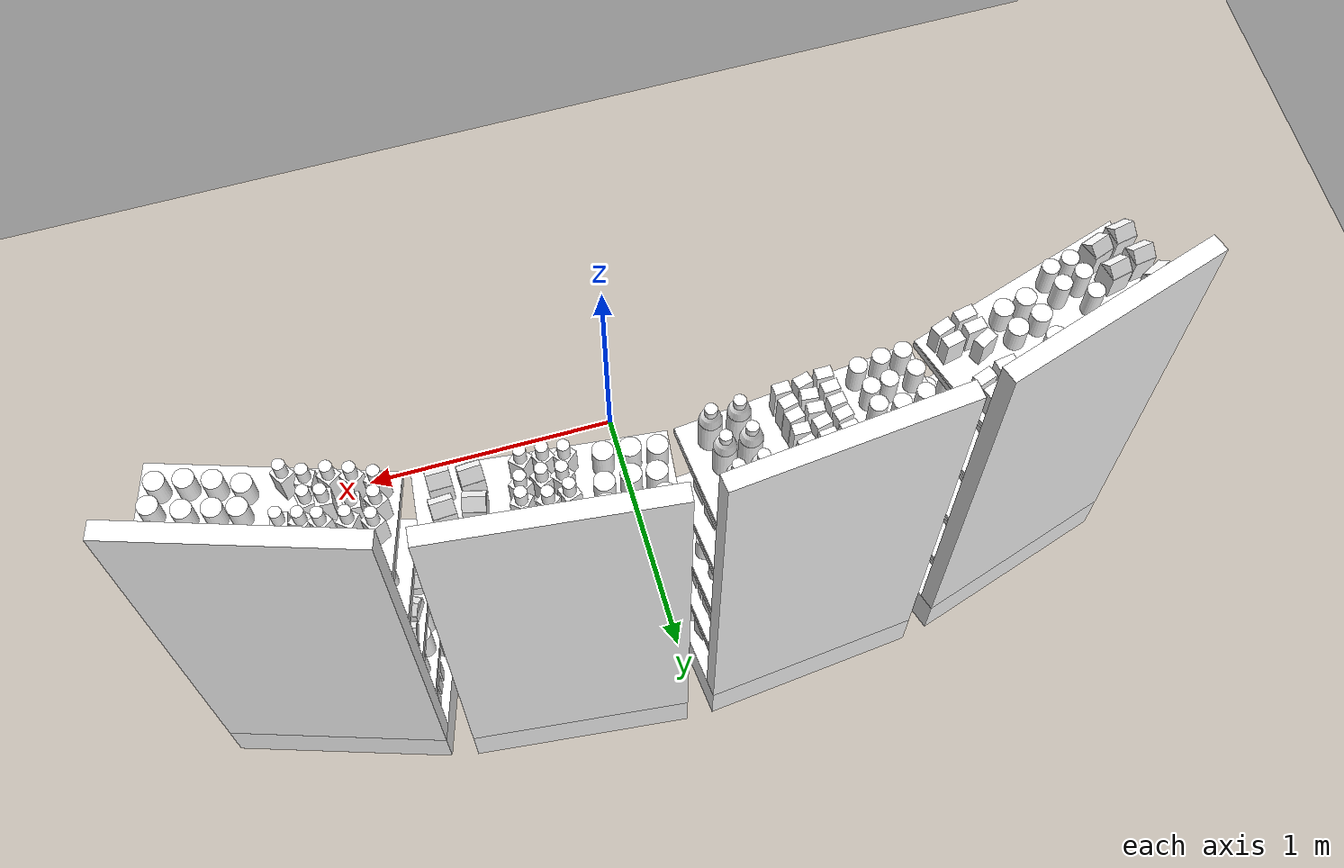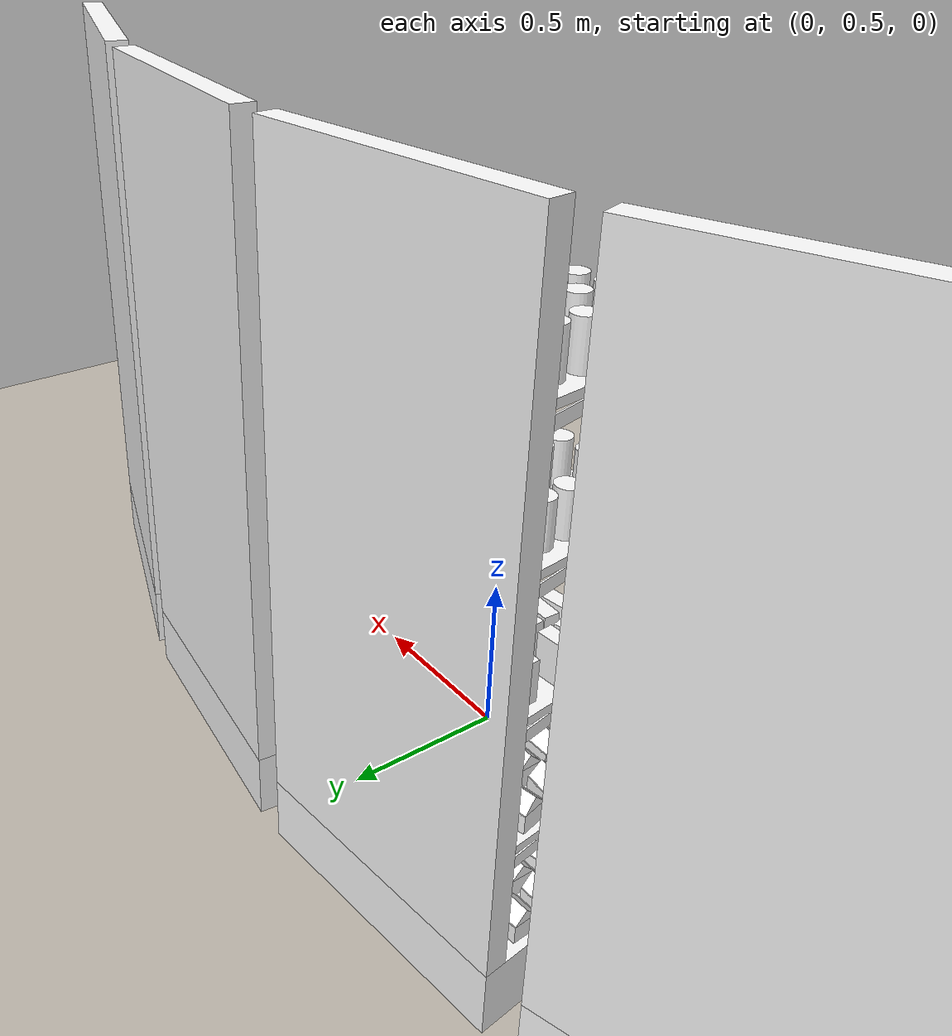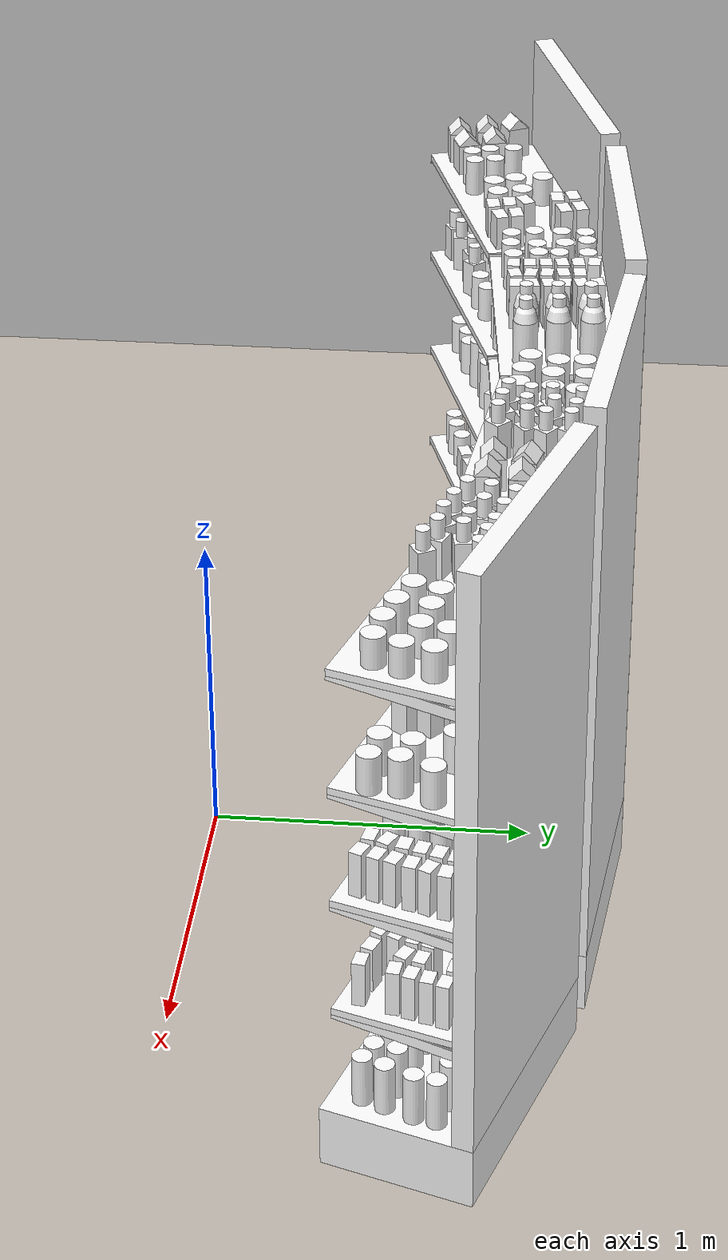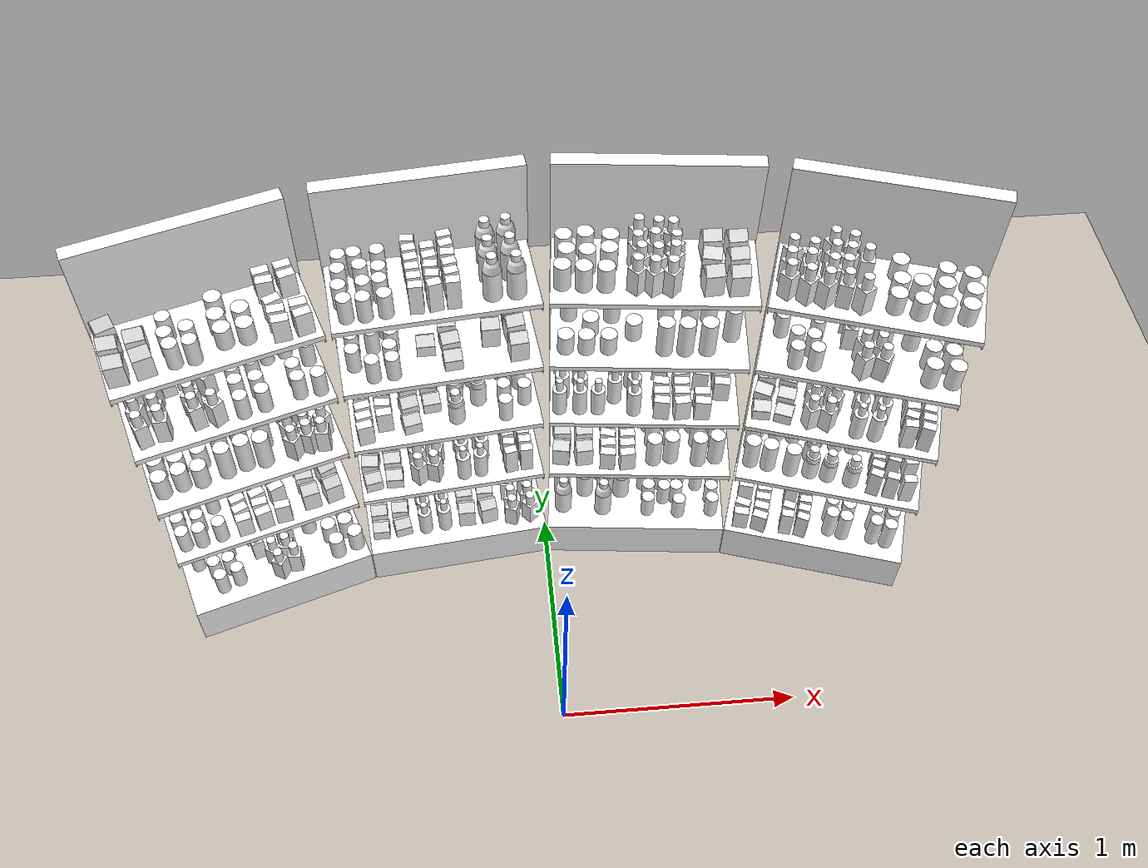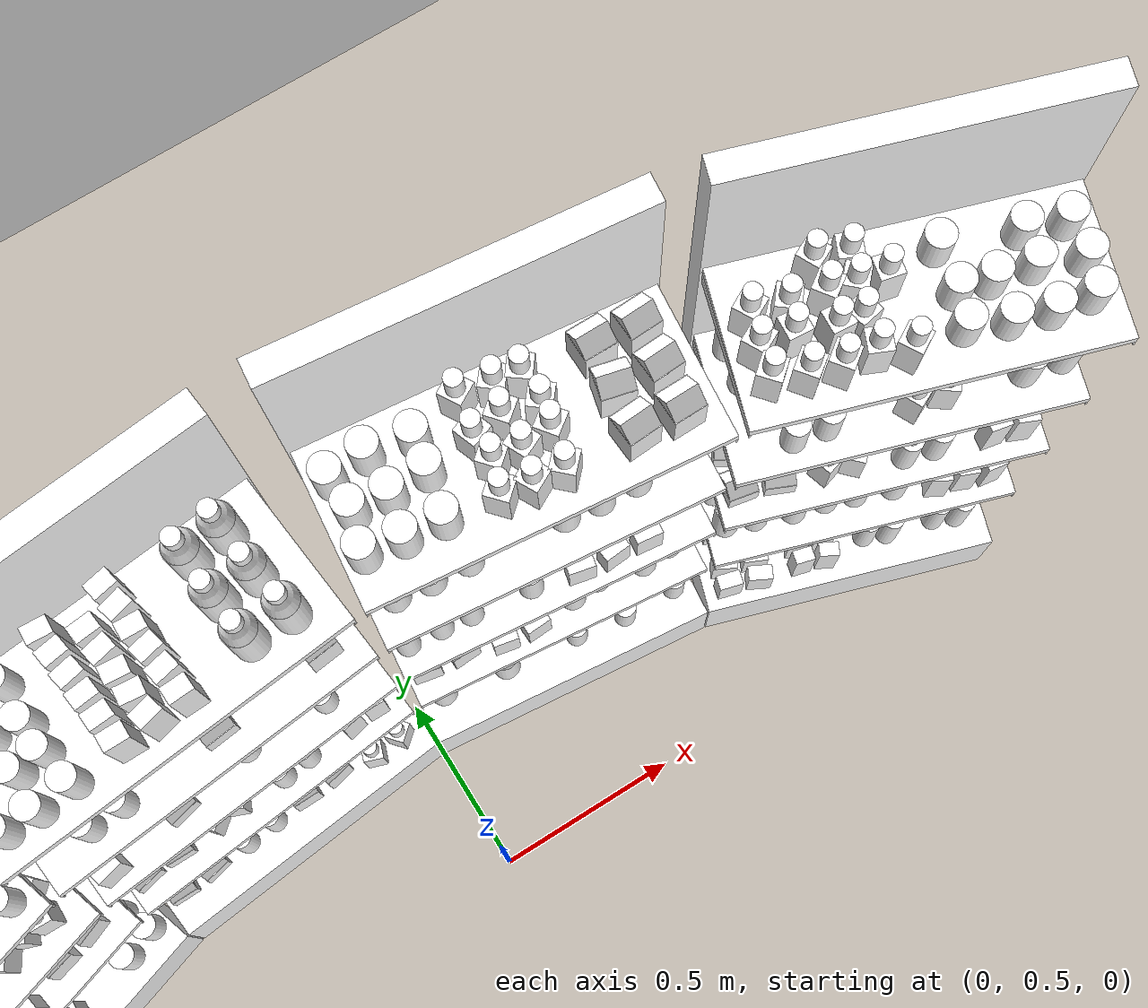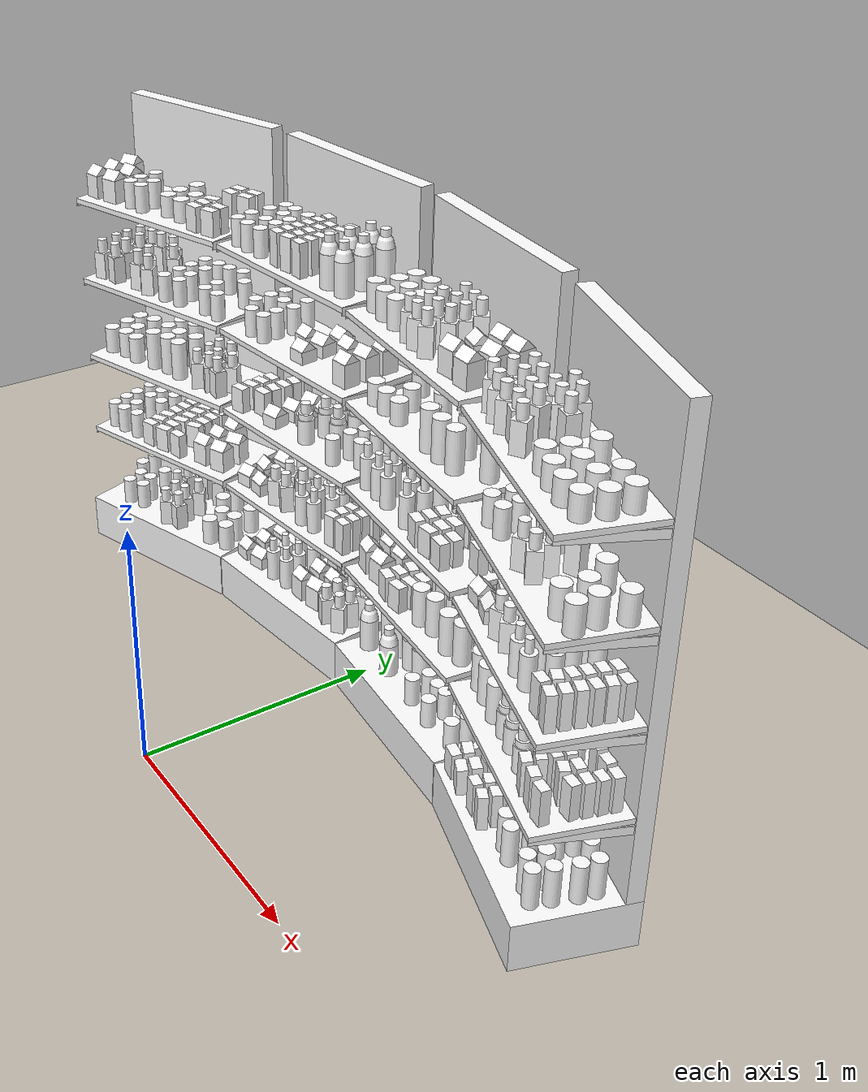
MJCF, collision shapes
<mujoco>
  <include file="store.xml"/>
  <option  gravity="0 0 -9.8" timestep="0.01"/>
  <asset>
    <!-- mujoco can not resolve asset path when include common/materials.xml, so we add material directly for this case-->
    <texture name="motphys-ground" type="2d" file="../../common/motphys-ground.png" />
    <material name="motphys-ground" texture="motphys-ground" texuniform="true"
      texrepeat="0.4 0.4" />
  </asset>
  <worldbody>
    <geom name="floor" size="0 0 0.05" type="plane" material="motphys-ground"/>
  </worldbody>
</mujoco>

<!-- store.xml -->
<mujoco>
  <compiler angle="radian" assetdir="assets" autolimits="true"/>

  <asset>
    <!-- Textures -->
    <texture type="2d" colorspace="sRGB" name="V_Bottle_350" file="V_Bottle_350.png"/>
    <texture type="2d" colorspace="sRGB" name="V_Bottle_360" file="V_Bottle_360.png"/>
    <texture type="2d" colorspace="sRGB" name="V_Bottle_400" file="V_Bottle_400.png"/>
    <texture type="2d" colorspace="sRGB" name="V_Bottle_600" file="V_Bottle_600.png"/>
    <texture type="2d" colorspace="sRGB" name="V_Cans_N250" file="V_Cans_N250.png"/>
    <texture type="2d" colorspace="sRGB" name="V_Cans_N330" file="V_Cans_N330.png"/>
    <texture type="2d" colorspace="sRGB" name="V_Cans_N355" file="V_Cans_N355.png"/>
    <texture type="2d" colorspace="sRGB" name="V_Cans_N500" file="V_Cans_N500.png"/>
    <texture type="2d" colorspace="sRGB" name="V_Cans_S250" file="V_Cans_S250.png"/>
    <texture type="2d" colorspace="sRGB" name="V_Cans_S330" file="V_Cans_S330.png"/>
    <texture type="2d" colorspace="sRGB" name="V_Cans_S355" file="V_Cans_S355.png"/>
    <texture type="2d" colorspace="linear" name="V_Cans_N250_orm" file="V_Cans_N250_orm.png"/>
    <texture type="2d" colorspace="linear" name="V_Cans_N330_orm" file="V_Cans_N330_orm.png"/>
    <texture type="2d" colorspace="linear" name="V_Cans_N355_orm" file="V_Cans_N355_orm.png"/>
    <texture type="2d" colorspace="linear" name="V_Cans_N500_orm" file="V_Cans_N500_orm.png"/>
    <texture type="2d" colorspace="linear" name="V_Cans_S250_orm" file="V_Cans_S250_orm.png"/>
    <texture type="2d" colorspace="linear" name="V_Cans_S330_orm" file="V_Cans_S330_orm.png"/>
    <texture type="2d" colorspace="linear" name="V_Cans_S355_orm" file="V_Cans_S355_orm.png"/>
    <texture type="2d" colorspace="sRGB" name="V_Tetra_250_F" file="V_Tetra_250_F.png"/>
    <texture type="2d" colorspace="sRGB" name="V_Tetra_250_T" file="V_Tetra_250_T.png"/>
    <texture type="2d" colorspace="sRGB" name="V_Tetra_300" file="V_Tetra_300.png"/>
    <texture type="2d" colorspace="sRGB" name="V_Tetra_500" file="V_Tetra_500.png"/>
    <texture type="2d" colorspace="sRGB" name="metal_painted_white_basecolor" file="metal_painted_white_basecolor.png"/>
    <texture type="2d" colorspace="linear" name="metal_painted_white_normal" file="metal_painted_white_normal.png"/>
    <texture type="2d" colorspace="linear" name="metal_painted_white_orm" file="metal_painted_white_orm.png"/>

    <!-- Materials -->
    <material name="Bottle_A" texture="V_Bottle_350" specular="0.5" reflectance="0.5" metallic="0.0" roughness="0.20000000298023224"/>
    <material name="Bottle_B" texture="V_Bottle_360" specular="0.5" reflectance="0.5" metallic="0.0" roughness="0.20000000298023224"/>
    <material name="Bottle_C" texture="V_Bottle_400" specular="0.5" reflectance="0.5" metallic="0.0" roughness="0.20000000298023224"/>
    <material name="Bottle_D" texture="V_Bottle_600" specular="0.5" reflectance="0.5" metallic="0.0" roughness="0.20000000298023224"/>
    <material name="Cans_A" specular="0.5" reflectance="0.5" metallic="1.0" roughness="1.0">
      <layer texture="V_Cans_N250" role="rgb"/>
      <layer texture="V_Cans_N250_orm" role="orm"/>
    </material>
    <material name="Cans_B" specular="0.5" reflectance="0.5" metallic="1.0" roughness="1.0">
      <layer texture="V_Cans_N330" role="rgb"/>
      <layer texture="V_Cans_N330_orm" role="orm"/>
    </material>
    <material name="Cans_C" specular="0.5" reflectance="0.5" metallic="1.0" roughness="1.0">
      <layer texture="V_Cans_N355" role="rgb"/>
      <layer texture="V_Cans_N355_orm" role="orm"/>
    </material>
    <material name="Cans_D" specular="0.5" reflectance="0.5" metallic="1.0" roughness="1.0">
      <layer texture="V_Cans_N500" role="rgb"/>
      <layer texture="V_Cans_N500_orm" role="orm"/>
    </material>
    <material name="Cans_E" specular="0.5" reflectance="0.5" metallic="1.0" roughness="1.0">
      <layer texture="V_Cans_S250" role="rgb"/>
      <layer texture="V_Cans_S250_orm" role="orm"/>
    </material>
    <material name="Cans_F" specular="0.5" reflectance="0.5" metallic="1.0" roughness="1.0">
      <layer texture="V_Cans_S330" role="rgb"/>
      <layer texture="V_Cans_S330_orm" role="orm"/>
    </material>
    <material name="Cans_G" specular="0.5" reflectance="0.5" metallic="1.0" roughness="1.0">
      <layer texture="V_Cans_S355" role="rgb"/>
      <layer texture="V_Cans_S355_orm" role="orm"/>
    </material>
    <material name="Tetra_A" texture="V_Tetra_250_F" specular="0.5" reflectance="0.5" metallic="0.0" roughness="0.30000001192092896"/>
    <material name="Tetra_B" texture="V_Tetra_250_T" specular="0.5" reflectance="0.5" metallic="0.0" roughness="0.30000001192092896"/>
    <material name="Tetra_C" texture="V_Tetra_300" specular="0.5" reflectance="0.5" metallic="0.0" roughness="0.30000001192092896"/>
    <material name="Tetra_D" texture="V_Tetra_500" specular="0.5" reflectance="0.5" metallic="0.0" roughness="0.30000001192092896"/>
    <material name="Metal_White" specular="0.5" reflectance="0.5" metallic="1.0" roughness="1.0" texrepeat="3.0 3.0" texuniform="true">
      <layer texture="metal_painted_white_basecolor" role="rgb"/>
    </material>

    <!-- Visual meshes -->
    <mesh class="visual" name="V_Bottle_350" file="V_Bottle_350.obj"/>
    <mesh class="visual" name="V_Bottle_360" file="V_Bottle_360.obj"/>
    <mesh class="visual" name="V_Bottle_400" file="V_Bottle_400.obj"/>
    <mesh class="visual" name="V_Bottle_600" file="V_Bottle_600.obj"/>
    <mesh class="visual" name="V_Cans_N250" file="V_Cans_N250.obj"/>
    <mesh class="visual" name="V_Cans_N330" file="V_Cans_N330.obj"/>
    <mesh class="visual" name="V_Cans_N355" file="V_Cans_N355.obj"/>
    <mesh class="visual" name="V_Cans_N500" file="V_Cans_N500.obj"/>
    <mesh class="visual" name="V_Cans_S250" file="V_Cans_S250.obj"/>
    <mesh class="visual" name="V_Cans_S330" file="V_Cans_S330.obj"/>
    <mesh class="visual" name="V_Cans_S355" file="V_Cans_S355.obj"/>
    <mesh class="visual" name="V_Tetra_250_F" file="V_Tetra_250_F.obj"/>
    <mesh class="visual" name="V_Tetra_250_T" file="V_Tetra_250_T.obj"/>
    <mesh class="visual" name="V_Tetra_300" file="V_Tetra_300.obj"/>
    <mesh class="visual" name="V_Tetra_500" file="V_Tetra_500.obj"/>
    <mesh class="visual" name="V_Shelf_Frame" file="V_Shelf_Frame.obj"/>
    <mesh class="visual" name="V_Shelf_Plat" file="V_Shelf_Plat.obj"/>

    <!-- Collision meshes -->
    <mesh class="collision" name="C_Mesh_Bottle_600_A" file="C_Mesh_Bottle_600_A.stl"/>
  </asset>

  <default>
      <default class="visual">
        <geom type="mesh" contype="0" conaffinity="0" group="2"/>
      </default>
      <default class="collision">
        <geom type="mesh" rgba="1 1 1 1" group="3" contype="1" conaffinity="1"/>
          <default class="C_Box_Bottle_350_A">
            <geom type="box" rgba="1 1 1 1" size="0.026499999687075615 0.026499999687075615 0.057902202010154724" quat="1.0 0.0 0.0 0.0" mass="0.0" pos="4.656612873077393e-10 0.0 0.057902202010154724"/>
          </default>
          <default class="C_Cylinder_Bottle_350_A">
            <geom type="cylinder" rgba="1 1 1 1" size="0.01970490626990795 0.028597794473171234" quat="1.0 0.0 0.0 0.0" mass="0.0" pos="1.4741090126335621e-08 -6.402842700481415e-10 0.14440220594406128"/>
          </default>
          <default class="C_Cylinder_Bottle_360_A">
            <geom type="cylinder" rgba="1 1 1 1" size="0.029000001028180122 0.06731711328029633" quat="1.0 0.0 0.0 0.0" mass="0.0" pos="7.654307410120964e-09 -9.313225746154785e-10 0.06731711328029633"/>
          </default>
          <default class="C_Cylinder_Bottle_360_B">
            <geom type="cylinder" rgba="1 1 1 1" size="0.014499999582767487 0.026682879775762558" quat="1.0 0.0 0.0 0.0" mass="0.0" pos="7.719791028648615e-09 -1.1641532182693481e-10 0.1613171100616455"/>
          </default>
          <default class="C_Cylinder_Bottle_400_A">
            <geom type="cylinder" rgba="1 1 1 1" size="0.03350000083446503 0.05243777483701706" quat="1.0 0.0 0.0 0.0" mass="0.0" pos="7.30506144464016e-09 1.1641532182693481e-10 0.05243777856230736"/>
          </default>
          <default class="C_Cylinder_Bottle_400_B">
            <geom type="cylinder" rgba="1 1 1 1" size="0.028748326003551483 0.012587248347699642" quat="1.0 0.0 0.0 0.0" mass="0.0" pos="7.188646122813225e-09 -2.9103830456733704e-10 0.11746280640363693"/>
          </default>
          <default class="C_Cylinder_Bottle_400_C">
            <geom type="cylinder" rgba="1 1 1 1" size="0.01970490626990795 0.021474963054060936" quat="1.0 0.0 0.0 0.0" mass="0.0" pos="7.283233571797609e-09 2.9103830456733704e-10 0.15152503550052643"/>
          </default>
          <default class="C_Cylinder_Bottle_600_A">
            <geom type="cylinder" rgba="1 1 1 1" size="0.0364999994635582 0.06797454506158829" quat="1.0 0.0 0.0 0.0" mass="0.0" pos="1.5701516531407833e-08 -6.984919309616089e-10 0.06797454506158829"/>
          </default>
          <default class="C_Cylinder_Bottle_600_C">
            <geom type="cylinder" rgba="1 1 1 1" size="0.01970490626990795 0.01435941457748413" quat="1.0 0.0 0.0 0.0" mass="0.0" pos="-3.289230554592848e-10 1.0111580461824587e-09 0.1936405748128891"/>
          </default>
          <default class="C_Mesh_Bottle_600_A">
            <geom type="mesh" rgba="1 1 1 1" mesh="C_Mesh_Bottle_600_A" quat="1.0 0.0 0.0 0.0" mass="0.0" pos="0.0 2.5870072750677764e-10 0.16027739644050598"/>
          </default>
          <default class="C_Cylinder_Cans_N250">
            <geom type="cylinder" rgba="1 1 1 1" size="0.03310000151395798 0.04600000008940697" quat="1.0 0.0 0.0 0.0" mass="0.0" pos="2.9103830456733704e-11 -1.1641532182693481e-10 0.04600000008940697"/>
          </default>
          <default class="C_Cylinder_Cans_N330">
            <geom type="cylinder" rgba="1 1 1 1" size="0.03310000151395798 0.0575999990105629" quat="1.0 0.0 0.0 0.0" mass="0.0" pos="-1.4872057363390923e-08 -1.1641532182693481e-10 0.0575999990105629"/>
          </default>
          <default class="C_Cylinder_Cans_N355">
            <geom type="cylinder" rgba="1 1 1 1" size="0.03310000151395798 0.0781015008687973" quat="1.0 0.0 0.0 0.0" mass="0.0" pos="-7.4214767664670944e-09 -1.1641532182693481e-10 0.0781015008687973"/>
          </default>
          <default class="C_Cylinder_Cans_N500">
            <geom type="cylinder" rgba="1 1 1 1" size="0.03310000151395798 0.08390000462532043" quat="1.0 0.0 0.0 0.0" mass="0.0" pos="2.9103830456733704e-11 -1.1641532182693481e-10 0.08389999717473984"/>
          </default>
          <default class="C_Cylinder_Cans_S250">
            <geom type="cylinder" rgba="1 1 1 1" size="0.028699999675154686 0.057500001043081284" quat="1.0 0.0 0.0 0.0" mass="0.0" pos="-2.0372681319713593e-10 3.4924596548080444e-10 0.057500001043081284"/>
          </default>
          <default class="C_Cylinder_Cans_S330">
            <geom type="cylinder" rgba="1 1 1 1" size="0.028699999675154686 0.0729999989271164" quat="1.0 0.0 0.0 0.0" mass="0.0" pos="-2.0372681319713593e-10 3.4924596548080444e-10 0.07300000637769699"/>
          </default>
          <default class="C_Cylinder_Cans_S355">
            <geom type="cylinder" rgba="1 1 1 1" size="0.028699999675154686 0.07779999822378159" quat="1.0 0.0 0.0 0.0" mass="0.0" pos="-2.0372681319713593e-10 3.4924596548080444e-10 0.07779999822378159"/>
          </default>
          <default class="C_Box_Tetra_250_F">
            <geom type="box" rgba="1 1 1 1" size="0.03240650147199631 0.020045999437570572 0.05340399965643883" quat="1.0 0.0 0.0 0.0" mass="0.0" pos="0.0 0.0 0.05340399965643883"/>
          </default>
          <default class="C_Box_Tetra_250_T">
            <geom type="box" rgba="1 1 1 1" size="0.02655849978327751 0.01874599978327751 0.06965235620737076" quat="1.0 0.0 0.0 0.0" mass="0.0" pos="4.656612873077393e-10 0.0 0.0696524977684021"/>
          </default>
          <default class="C_Box_Tetra_300_A">
            <geom type="box" rgba="1 1 1 1" size="0.03637507185339928 0.03601999953389168 0.02579064667224884" quat="1.0 0.0 0.0 0.0" mass="0.0" pos="9.313225746154785e-10 0.0 0.025790680199861526"/>
          </default>
          <default class="C_Box_Tetra_300_B">
            <geom type="box" rgba="1 1 1 1" size="0.03601999953389168 0.025498365983366966 0.025498365983366966" quat="0.9238795042037964 -0.3826834559440613 0.0 0.0" mass="0.0" pos="-9.313225746154785e-10 0.0 0.049688734114170074"/>
          </default>
          <default class="C_Box_Tetra_500_A">
            <geom type="box" rgba="1 1 1 1" size="0.03637507185339928 0.03601999953389168 0.04900600016117096" quat="1.0 0.0 0.0 0.0" mass="0.0" pos="9.313225746154785e-10 0.0 0.049006033688783646"/>
          </default>
          <default class="C_Box_Tetra_500_B">
            <geom type="box" rgba="1 1 1 1" size="0.03601999953389168 0.025498362258076668 0.025498362258076668" quat="0.9238795042037964 -0.3826834559440613 0.0 0.0" mass="0.0" pos="-9.313225746154785e-10 0.0 0.0963839516043663"/>
          </default>
          <default class="C_Box_Shelf_Frame_A">
            <geom type="box" rgba="1 1 1 1" size="0.3999999463558197 0.22648344933986664 0.096900075674057" quat="1.0 0.0 0.0 0.0" mass="0.0" pos="2.2351741790771484e-08 -0.19648343324661255 0.0969000831246376"/>
          </default>
          <default class="C_Box_Shelf_Frame_B">
            <geom type="box" rgba="1 1 1 1" size="0.3999999463558197 0.03149170055985451 0.9050999879837036" quat="1.0 0.0 0.0 0.0" mass="0.0" pos="2.9802322387695312e-08 -0.0014916732907295227 1.098900318145752"/>
          </default>
          <default class="C_Box_Shelf_Plat_A">
            <geom type="box" rgba="1 1 1 1" size="0.3950001299381256 0.1755083203315735 0.010900028049945831" quat="1.0 0.0 0.0 0.0" mass="0.0" pos="0.0 -0.17449170351028442 -0.009999990463256836"/>
          </default>
          <default class="C_Box_Shelf_Plat_B">
            <geom type="box" rgba="1 1 1 1" size="0.0020000040531158447 0.1755083054304123 0.01628100872039795" quat="0.9989004731178284 -0.046881046146154404 0.0 0.0" mass="0.0" pos="-0.39300012588500977 -0.17449170351028442 -0.0318489670753479"/>
          </default>
          <default class="C_Box_Shelf_Plat_C">
            <geom type="box" rgba="1 1 1 1" size="0.0020000040531158447 0.1755083054304123 0.01628100872039795" quat="0.9989004731178284 -0.046881046146154404 0.0 0.0" mass="0.0" pos="0.3929999768733978 -0.17449170351028442 -0.0318489670753479"/>
          </default>
      </default>
  </default>

  <worldbody>
    <light pos="0 0.5 3" dir="0.0 0.20268867909908295 -0.9792432188987732" diffuse="0.8 0.8 0.8" directional="true" castshadow="true"/>

    <geom class="visual" mesh="V_Shelf_Frame" pos="-1.3133227825164795 1.0419902801513672 0.0" quat="0.9876883029937744 0.0 0.0 0.15643462538719177" material="Metal_White"/>
    <geom class="C_Box_Shelf_Frame_A" pos="-1.2526060342788696 0.8551234602928162 0.0969000831246376" quat="0.9876883029937744 0.0 0.0 0.15643462538719177"/>
    <geom class="C_Box_Shelf_Frame_B" pos="-1.3128618001937866 1.0405715703964233 1.098900318145752" quat="0.9876883029937744 0.0 0.0 0.15643462538719177"/>
    <geom class="visual" mesh="V_Shelf_Frame" pos="-0.44424617290496826 1.2267184257507324 0.0" quat="0.9986295104026794 0.0 0.0 0.052336204797029495" material="Metal_White"/>
    <geom class="C_Box_Shelf_Frame_A" pos="-0.4237080514431 1.0313122272491455 0.0969000831246376" quat="0.9986295104026794 0.0 0.0 0.052336204797029495"/>
    <geom class="C_Box_Shelf_Frame_B" pos="-0.44409021735191345 1.2252349853515625 1.098900318145752" quat="0.9986295104026794 0.0 0.0 0.052336204797029495"/>
    <geom class="visual" mesh="V_Shelf_Frame" pos="0.4442458748817444 1.2267179489135742 0.0" quat="0.998629629611969 0.0 0.0 -0.05233586207032204" material="Metal_White"/>
    <geom class="C_Box_Shelf_Frame_A" pos="0.4237078130245209 1.0313109159469604 0.0969000831246376" quat="0.998629629611969 0.0 0.0 -0.05233586207032204"/>
    <geom class="C_Box_Shelf_Frame_B" pos="0.44408997893333435 1.2252343893051147 1.098900318145752" quat="0.998629629611969 0.0 0.0 -0.05233586207032204"/>
    <geom class="visual" mesh="V_Shelf_Frame" pos="1.3133219480514526 1.0419902801513672 0.0" quat="0.9876883029937744 0.0 0.0 -0.15643462538719177" material="Metal_White"/>
    <geom class="C_Box_Shelf_Frame_A" pos="1.2526051998138428 0.8551234602928162 0.0969000831246376" quat="0.9876883029937744 0.0 0.0 -0.15643462538719177"/>
    <geom class="C_Box_Shelf_Frame_B" pos="1.3128609657287598 1.0405715703964233 1.098900318145752" quat="0.9876883029937744 0.0 0.0 -0.15643462538719177"/>
    <geom class="visual" mesh="V_Shelf_Plat" pos="-1.3028161525726318 1.0096545219421387 0.5529000759124756" quat="0.9876883029937744 0.0 0.0 0.15643462538719177" material="Metal_White"/>
    <geom class="C_Box_Shelf_Plat_A" pos="-1.2488951683044434 0.8437030911445618 0.5429000854492188" quat="0.9876883029937744 0.0 0.0 0.15643462538719177"/>
    <geom class="C_Box_Shelf_Plat_B" pos="-1.622660517692566 0.7222592830657959 0.5210511088371277" quat="0.9866023063659668 -0.04630386084318161 0.007333818823099136 0.1562626212835312"/>
    <geom class="C_Box_Shelf_Plat_C" pos="-0.8751301169395447 0.9651468992233276 0.5210511088371277" quat="0.9866023063659668 -0.04630386084318161 0.007333818823099136 0.1562626212835312"/>
    <geom class="visual" mesh="V_Shelf_Plat" pos="-0.4406922459602356 1.192903995513916 0.5529000759124756" quat="0.9986295104026794 0.0 0.0 0.0523362010717392" material="Metal_White"/>
    <geom class="C_Box_Shelf_Plat_A" pos="-0.4224528968334198 1.0193690061569214 0.5429000854492188" quat="0.9986295104026794 0.0 0.0 0.0523362010717392"/>
    <geom class="C_Box_Shelf_Plat_B" pos="-0.8132983446121216 0.9782892465591431 0.5210511088371277" quat="0.9975314736366272 -0.04681679606437683 0.0024535758420825005 0.052278656512498856"/>
    <geom class="C_Box_Shelf_Plat_C" pos="-0.03160759434103966 1.0604486465454102 0.5210511088371277" quat="0.9975314736366272 -0.04681679606437683 0.0024535758420825005 0.052278656512498856"/>
    <geom class="visual" mesh="V_Shelf_Plat" pos="0.44069185853004456 1.1929049491882324 0.5529000759124756" quat="0.9986295104026794 0.0 0.0 -0.052335865795612335" material="Metal_White"/>
    <geom class="C_Box_Shelf_Plat_A" pos="0.42245253920555115 1.019369125366211 0.5429000854492188" quat="0.9986295104026794 0.0 0.0 -0.052335865795612335"/>
    <geom class="C_Box_Shelf_Plat_B" pos="0.031605303287506104 1.0604487657546997 0.5210511088371277" quat="0.9975314736366272 -0.04681679606437683 -0.0024535602424293756 -0.052278321236371994"/>
    <geom class="C_Box_Shelf_Plat_C" pos="0.8132996559143066 0.9782894849777222 0.5210511088371277" quat="0.9975314736366272 -0.04681679606437683 -0.0024535602424293756 -0.052278321236371994"/>
    <geom class="visual" mesh="V_Shelf_Plat" pos="1.3028154373168945 1.0096549987792969 0.5529000759124756" quat="0.9876883029937744 0.0 0.0 -0.15643462538719177" material="Metal_White"/>
    <geom class="C_Box_Shelf_Plat_A" pos="1.248894453048706 0.84370356798172 0.5429000854492188" quat="0.9876883029937744 0.0 0.0 -0.15643462538719177"/>
    <geom class="C_Box_Shelf_Plat_B" pos="0.875129222869873 0.9651473760604858 0.5210511088371277" quat="0.9866023063659668 -0.04630386084318161 -0.007333818823099136 -0.1562626212835312"/>
    <geom class="C_Box_Shelf_Plat_C" pos="1.6226595640182495 0.7222597599029541 0.5210511088371277" quat="0.9866023063659668 -0.04630386084318161 -0.007333818823099136 -0.1562626212835312"/>
    <geom class="visual" mesh="V_Shelf_Plat" pos="-1.3028161525726318 1.0096545219421387 0.9129000902175903" quat="0.9876883029937744 0.0 0.0 0.15643462538719177" material="Metal_White"/>
    <geom class="C_Box_Shelf_Plat_A" pos="-1.2488951683044434 0.8437030911445618 0.9029000997543335" quat="0.9876883029937744 0.0 0.0 0.15643462538719177"/>
    <geom class="C_Box_Shelf_Plat_B" pos="-1.622660517692566 0.7222592830657959 0.8810511231422424" quat="0.9866023063659668 -0.04630386084318161 0.007333818823099136 0.1562626212835312"/>
    <geom class="C_Box_Shelf_Plat_C" pos="-0.8751301169395447 0.9651468992233276 0.8810511231422424" quat="0.9866023063659668 -0.04630386084318161 0.007333818823099136 0.1562626212835312"/>
    <geom class="visual" mesh="V_Shelf_Plat" pos="-0.4406922459602356 1.192903995513916 0.9129000902175903" quat="0.9986295104026794 0.0 0.0 0.0523362010717392" material="Metal_White"/>
    <geom class="C_Box_Shelf_Plat_A" pos="-0.4224528968334198 1.0193690061569214 0.9029000997543335" quat="0.9986295104026794 0.0 0.0 0.0523362010717392"/>
    <geom class="C_Box_Shelf_Plat_B" pos="-0.8132983446121216 0.9782892465591431 0.8810511231422424" quat="0.9975314736366272 -0.04681679606437683 0.0024535758420825005 0.052278656512498856"/>
    <geom class="C_Box_Shelf_Plat_C" pos="-0.03160759434103966 1.0604486465454102 0.8810511231422424" quat="0.9975314736366272 -0.04681679606437683 0.0024535758420825005 0.052278656512498856"/>
    <geom class="visual" mesh="V_Shelf_Plat" pos="0.44069185853004456 1.1929049491882324 0.9129000902175903" quat="0.9986295104026794 0.0 0.0 -0.052335865795612335" material="Metal_White"/>
    <geom class="C_Box_Shelf_Plat_A" pos="0.42245253920555115 1.019369125366211 0.9029000997543335" quat="0.9986295104026794 0.0 0.0 -0.052335865795612335"/>
    <geom class="C_Box_Shelf_Plat_B" pos="0.031605303287506104 1.0604487657546997 0.8810511231422424" quat="0.9975314736366272 -0.04681679606437683 -0.0024535602424293756 -0.052278321236371994"/>
    <geom class="C_Box_Shelf_Plat_C" pos="0.8132996559143066 0.9782894849777222 0.8810511231422424" quat="0.9975314736366272 -0.04681679606437683 -0.0024535602424293756 -0.052278321236371994"/>
    <geom class="visual" mesh="V_Shelf_Plat" pos="1.3028154373168945 1.0096549987792969 0.9129000902175903" quat="0.9876883029937744 0.0 0.0 -0.15643462538719177" material="Metal_White"/>
    <geom class="C_Box_Shelf_Plat_A" pos="1.248894453048706 0.84370356798172 0.9029000997543335" quat="0.9876883029937744 0.0 0.0 -0.15643462538719177"/>
    <geom class="C_Box_Shelf_Plat_B" pos="0.875129222869873 0.9651473760604858 0.8810511231422424" quat="0.9866023063659668 -0.04630386084318161 -0.007333818823099136 -0.1562626212835312"/>
    <geom class="C_Box_Shelf_Plat_C" pos="1.6226595640182495 0.7222597599029541 0.8810511231422424" quat="0.9866023063659668 -0.04630386084318161 -0.007333818823099136 -0.1562626212835312"/>
    <geom class="visual" mesh="V_Shelf_Plat" pos="-1.3028161525726318 1.0096545219421387 1.272900104522705" quat="0.9876883029937744 0.0 0.0 0.15643462538719177" material="Metal_White"/>
    <geom class="C_Box_Shelf_Plat_A" pos="-1.2488951683044434 0.8437030911445618 1.2629001140594482" quat="0.9876883029937744 0.0 0.0 0.15643462538719177"/>
    <geom class="C_Box_Shelf_Plat_B" pos="-1.622660517692566 0.7222592830657959 1.241051197052002" quat="0.9866023063659668 -0.04630386084318161 0.007333818823099136 0.1562626212835312"/>
    <geom class="C_Box_Shelf_Plat_C" pos="-0.8751301169395447 0.9651468992233276 1.241051197052002" quat="0.9866023063659668 -0.04630386084318161 0.007333818823099136 0.1562626212835312"/>
    <geom class="visual" mesh="V_Shelf_Plat" pos="-0.4406922459602356 1.192903995513916 1.272900104522705" quat="0.9986295104026794 0.0 0.0 0.0523362010717392" material="Metal_White"/>
    <geom class="C_Box_Shelf_Plat_A" pos="-0.4224528968334198 1.0193690061569214 1.2629001140594482" quat="0.9986295104026794 0.0 0.0 0.0523362010717392"/>
    <geom class="C_Box_Shelf_Plat_B" pos="-0.8132983446121216 0.9782892465591431 1.241051197052002" quat="0.9975314736366272 -0.04681679606437683 0.0024535758420825005 0.052278656512498856"/>
    <geom class="C_Box_Shelf_Plat_C" pos="-0.03160759434103966 1.0604486465454102 1.241051197052002" quat="0.9975314736366272 -0.04681679606437683 0.0024535758420825005 0.052278656512498856"/>
    <geom class="visual" mesh="V_Shelf_Plat" pos="0.44069185853004456 1.1929049491882324 1.272900104522705" quat="0.9986295104026794 0.0 0.0 -0.052335865795612335" material="Metal_White"/>
    <geom class="C_Box_Shelf_Plat_A" pos="0.42245253920555115 1.019369125366211 1.2629001140594482" quat="0.9986295104026794 0.0 0.0 -0.052335865795612335"/>
    <geom class="C_Box_Shelf_Plat_B" pos="0.031605303287506104 1.0604487657546997 1.241051197052002" quat="0.9975314736366272 -0.04681679606437683 -0.0024535602424293756 -0.052278321236371994"/>
    <geom class="C_Box_Shelf_Plat_C" pos="0.8132996559143066 0.9782894849777222 1.241051197052002" quat="0.9975314736366272 -0.04681679606437683 -0.0024535602424293756 -0.052278321236371994"/>
    <geom class="visual" mesh="V_Shelf_Plat" pos="1.3028154373168945 1.0096549987792969 1.272900104522705" quat="0.9876883029937744 0.0 0.0 -0.15643462538719177" material="Metal_White"/>
    <geom class="C_Box_Shelf_Plat_A" pos="1.248894453048706 0.84370356798172 1.2629001140594482" quat="0.9876883029937744 0.0 0.0 -0.15643462538719177"/>
    <geom class="C_Box_Shelf_Plat_B" pos="0.875129222869873 0.9651473760604858 1.241051197052002" quat="0.9866023063659668 -0.04630386084318161 -0.007333818823099136 -0.1562626212835312"/>
    <geom class="C_Box_Shelf_Plat_C" pos="1.6226595640182495 0.7222597599029541 1.241051197052002" quat="0.9866023063659668 -0.04630386084318161 -0.007333818823099136 -0.1562626212835312"/>
    <geom class="visual" mesh="V_Shelf_Plat" pos="-1.3028161525726318 1.0096545219421387 1.6329001188278198" quat="0.9876883029937744 0.0 0.0 0.15643462538719177" material="Metal_White"/>
    <geom class="C_Box_Shelf_Plat_A" pos="-1.2488951683044434 0.8437030911445618 1.622900128364563" quat="0.9876883029937744 0.0 0.0 0.15643462538719177"/>
    <geom class="C_Box_Shelf_Plat_B" pos="-1.6226603984832764 0.7222592830657959 1.6010510921478271" quat="0.9866023063659668 -0.04630386084318161 0.007333818823099136 0.1562626212835312"/>
    <geom class="C_Box_Shelf_Plat_C" pos="-0.8751301169395447 0.9651468396186829 1.6010510921478271" quat="0.9866023063659668 -0.04630386084318161 0.007333818823099136 0.1562626212835312"/>
    <geom class="visual" mesh="V_Shelf_Plat" pos="-0.4406922459602356 1.192903995513916 1.6329001188278198" quat="0.9986295700073242 0.0 0.0 0.052336182445287704" material="Metal_White"/>
    <geom class="C_Box_Shelf_Plat_A" pos="-0.4224528968334198 1.0193688869476318 1.622900128364563" quat="0.9986295700073242 0.0 0.0 0.052336182445287704"/>
    <geom class="C_Box_Shelf_Plat_B" pos="-0.8132984638214111 0.9782891869544983 1.6010510921478271" quat="0.997531533241272 -0.04681679978966713 0.002453574910759926 0.05227863788604736"/>
    <geom class="C_Box_Shelf_Plat_C" pos="-0.031607478857040405 1.0604486465454102 1.6010510921478271" quat="0.997531533241272 -0.04681679978966713 0.002453574910759926 0.05227863788604736"/>
    <geom class="visual" mesh="V_Shelf_Plat" pos="0.44069185853004456 1.1929049491882324 1.6329001188278198" quat="0.998629629611969 0.0 0.0 -0.05233586207032204" material="Metal_White"/>
    <geom class="C_Box_Shelf_Plat_A" pos="0.42245253920555115 1.019369125366211 1.622900128364563" quat="0.998629629611969 0.0 0.0 -0.05233586207032204"/>
    <geom class="C_Box_Shelf_Plat_B" pos="0.0316053070127964 1.0604487657546997 1.6010510921478271" quat="0.9975315928459167 -0.04681680351495743 -0.002453560009598732 -0.052278317511081696"/>
    <geom class="C_Box_Shelf_Plat_C" pos="0.8132996559143066 0.9782895445823669 1.6010510921478271" quat="0.9975315928459167 -0.04681680351495743 -0.002453560009598732 -0.052278317511081696"/>
    <geom class="visual" mesh="V_Shelf_Plat" pos="1.3028154373168945 1.0096549987792969 1.6329001188278198" quat="0.9876883029937744 0.0 0.0 -0.15643462538719177" material="Metal_White"/>
    <geom class="C_Box_Shelf_Plat_A" pos="1.248894453048706 0.84370356798172 1.622900128364563" quat="0.9876883029937744 0.0 0.0 -0.15643462538719177"/>
    <geom class="C_Box_Shelf_Plat_B" pos="0.875129222869873 0.9651473760604858 1.6010510921478271" quat="0.9866023063659668 -0.04630386084318161 -0.007333818823099136 -0.1562626212835312"/>
    <geom class="C_Box_Shelf_Plat_C" pos="1.6226595640182495 0.7222597599029541 1.6010510921478271" quat="0.9866023063659668 -0.04630386084318161 -0.007333818823099136 -0.1562626212835312"/>
    <body name="Bottle_350.001" pos="-0.549186110496521 0.9054065942764282 0.553800106048584" quat="0.9372331500053406 0.0 0.0 0.3487033545970917">
      <joint type="free"/>
      <geom class="visual" mesh="V_Bottle_350" material="Bottle_A"/>
      <geom class="C_Box_Bottle_350_A"/>
      <geom class="C_Cylinder_Bottle_350_A"/>
    </body>
    <body name="Bottle_350.002" pos="-0.48189640045166016 0.9153547286987305 0.553800106048584" quat="0.981380820274353 0.0 0.0 -0.19207219779491425">
      <joint type="free"/>
      <geom class="visual" mesh="V_Bottle_350" material="Bottle_A"/>
      <geom class="C_Box_Bottle_350_A"/>
      <geom class="C_Cylinder_Bottle_350_A"/>
    </body>
    <body name="Bottle_350.003" pos="-0.5552678108215332 0.9770170450210571 0.553800106048584" quat="0.9198405742645264 0.0 0.0 -0.39229243993759155">
      <joint type="free"/>
      <geom class="visual" mesh="V_Bottle_350" material="Bottle_A"/>
      <geom class="C_Box_Bottle_350_A"/>
      <geom class="C_Cylinder_Bottle_350_A"/>
    </body>
    <body name="Bottle_350.004" pos="-0.4723368287086487 0.9906305074691772 0.553800106048584" quat="0.9933521747589111 0.0 0.0 -0.1151149794459343">
      <joint type="free"/>
      <geom class="visual" mesh="V_Bottle_350" material="Bottle_A"/>
      <geom class="C_Box_Bottle_350_A"/>
      <geom class="C_Cylinder_Bottle_350_A"/>
    </body>
    <body name="Bottle_350.005" pos="-0.563982367515564 1.036834955215454 0.553800106048584" quat="0.9519494771957397 0.0 0.0 0.30625516176223755">
      <joint type="free"/>
      <geom class="visual" mesh="V_Bottle_350" material="Bottle_A"/>
      <geom class="C_Box_Bottle_350_A"/>
      <geom class="C_Cylinder_Bottle_350_A"/>
    </body>
    <body name="Bottle_350.006" pos="-0.48630693554878235 1.041800618171692 0.553800106048584" quat="0.9832656383514404 0.0 0.0 -0.18217776715755463">
      <joint type="free"/>
      <geom class="visual" mesh="V_Bottle_350" material="Bottle_A"/>
      <geom class="C_Box_Bottle_350_A"/>
      <geom class="C_Cylinder_Bottle_350_A"/>
    </body>
    <body name="Bottle_350.007" pos="-0.5692707300186157 1.1145797967910767 0.553800106048584" quat="0.9713924527168274 0.0 0.0 0.23747994005680084">
      <joint type="free"/>
      <geom class="visual" mesh="V_Bottle_350" material="Bottle_A"/>
      <geom class="C_Box_Bottle_350_A"/>
      <geom class="C_Cylinder_Bottle_350_A"/>
    </body>
    <body name="Bottle_350.008" pos="-0.48765629529953003 1.1157333850860596 0.553800106048584" quat="0.965958833694458 0.0 0.0 0.2586958408355713">
      <joint type="free"/>
      <geom class="visual" mesh="V_Bottle_350" material="Bottle_A"/>
      <geom class="C_Box_Bottle_350_A"/>
      <geom class="C_Cylinder_Bottle_350_A"/>
    </body>
    <body name="Bottle_350.009" pos="0.3422345519065857 0.931499719619751 1.6338001489639282" quat="0.934680700302124 0.0 0.0 0.3554883301258087">
      <joint type="free"/>
      <geom class="visual" mesh="V_Bottle_350" material="Bottle_A"/>
      <geom class="C_Box_Bottle_350_A"/>
      <geom class="C_Cylinder_Bottle_350_A"/>
    </body>
    <body name="Bottle_350.010" pos="0.4051765501499176 0.9183236956596375 1.6338001489639282" quat="0.9707810878753662 0.0 0.0 0.23996683955192566">
      <joint type="free"/>
      <geom class="visual" mesh="V_Bottle_350" material="Bottle_A"/>
      <geom class="C_Box_Bottle_350_A"/>
      <geom class="C_Cylinder_Bottle_350_A"/>
    </body>
    <body name="Bottle_350.011" pos="0.4710484743118286 0.910703718662262 1.6338001489639282" quat="0.9272187352180481 0.0 0.0 -0.37452027201652527">
      <joint type="free"/>
      <geom class="visual" mesh="V_Bottle_350" material="Bottle_A"/>
      <geom class="C_Box_Bottle_350_A"/>
      <geom class="C_Cylinder_Bottle_350_A"/>
    </body>
    <body name="Bottle_350.012" pos="0.36415156722068787 0.9958621263504028 1.6338001489639282" quat="0.9383655786514282 0.0 0.0 0.34564441442489624">
      <joint type="free"/>
      <geom class="visual" mesh="V_Bottle_350" material="Bottle_A"/>
      <geom class="C_Box_Bottle_350_A"/>
      <geom class="C_Cylinder_Bottle_350_A"/>
    </body>
    <body name="Bottle_350.013" pos="0.4241446256637573 0.986456036567688 1.6338001489639282" quat="0.975824773311615 0.0 0.0 0.21855442225933075">
      <joint type="free"/>
      <geom class="visual" mesh="V_Bottle_350" material="Bottle_A"/>
      <geom class="C_Box_Bottle_350_A"/>
      <geom class="C_Cylinder_Bottle_350_A"/>
    </body>
    <body name="Bottle_350.014" pos="0.49014347791671753 0.9914512038230896 1.6338001489639282" quat="0.9494162201881409 0.0 0.0 0.31402042508125305">
      <joint type="free"/>
      <geom class="visual" mesh="V_Bottle_350" material="Bottle_A"/>
      <geom class="C_Box_Bottle_350_A"/>
      <geom class="C_Cylinder_Bottle_350_A"/>
    </body>
    <body name="Bottle_350.015" pos="0.3573199510574341 1.0550332069396973 1.6338001489639282" quat="0.9852616786956787 0.0 0.0 0.17105400562286377">
      <joint type="free"/>
      <geom class="visual" mesh="V_Bottle_350" material="Bottle_A"/>
      <geom class="C_Box_Bottle_350_A"/>
      <geom class="C_Cylinder_Bottle_350_A"/>
    </body>
    <body name="Bottle_350.016" pos="0.42395737767219543 1.0628176927566528 1.6338001489639282" quat="0.9419960975646973 0.0 0.0 0.3356238603591919">
      <joint type="free"/>
      <geom class="visual" mesh="V_Bottle_350" material="Bottle_A"/>
      <geom class="C_Box_Bottle_350_A"/>
      <geom class="C_Cylinder_Bottle_350_A"/>
    </body>
    <body name="Bottle_350.017" pos="0.5001076459884644 1.0435409545898438 1.6338001489639282" quat="0.9416672587394714 0.0 0.0 -0.3365454077720642">
      <joint type="free"/>
      <geom class="visual" mesh="V_Bottle_350" material="Bottle_A"/>
      <geom class="C_Box_Bottle_350_A"/>
      <geom class="C_Cylinder_Bottle_350_A"/>
    </body>
    <body name="Bottle_350.018" pos="0.37123024463653564 1.1392711400985718 1.6338001489639282" quat="0.8660029768943787 0.0 0.0 -0.5000390410423279">
      <joint type="free"/>
      <geom class="visual" mesh="V_Bottle_350" material="Bottle_A"/>
      <geom class="C_Box_Bottle_350_A"/>
      <geom class="C_Cylinder_Bottle_350_A"/>
    </body>
    <body name="Bottle_350.019" pos="0.4433298110961914 1.1234948635101318 1.6338001489639282" quat="0.9022205471992493 0.0 0.0 0.43127498030662537">
      <joint type="free"/>
      <geom class="visual" mesh="V_Bottle_350" material="Bottle_A"/>
      <geom class="C_Box_Bottle_350_A"/>
      <geom class="C_Cylinder_Bottle_350_A"/>
    </body>
    <body name="Bottle_350.020" pos="0.49788016080856323 1.1137796640396118 1.6338001489639282" quat="0.9485583305358887 0.0 0.0 -0.3166023790836334">
      <joint type="free"/>
      <geom class="visual" mesh="V_Bottle_350" material="Bottle_A"/>
      <geom class="C_Box_Bottle_350_A"/>
      <geom class="C_Cylinder_Bottle_350_A"/>
    </body>
    <body name="Bottle_350.021" pos="1.2267608642578125 0.7444162368774414 1.2738001346588135" quat="0.9754965305328369 0.0 0.0 0.22001488506793976">
      <joint type="free"/>
      <geom class="visual" mesh="V_Bottle_350" material="Bottle_A"/>
      <geom class="C_Box_Bottle_350_A"/>
      <geom class="C_Cylinder_Bottle_350_A"/>
    </body>
    <body name="Bottle_350.022" pos="1.2972412109375 0.7310272455215454 1.2738001346588135" quat="0.9485299587249756 0.0 0.0 -0.31668752431869507">
      <joint type="free"/>
      <geom class="visual" mesh="V_Bottle_350" material="Bottle_A"/>
      <geom class="C_Box_Bottle_350_A"/>
      <geom class="C_Cylinder_Bottle_350_A"/>
    </body>
    <body name="Bottle_350.023" pos="1.2397549152374268 0.8154998421669006 1.2738001346588135" quat="0.9878154397010803 0.0 0.0 0.15562991797924042">
      <joint type="free"/>
      <geom class="visual" mesh="V_Bottle_350" material="Bottle_A"/>
      <geom class="C_Box_Bottle_350_A"/>
      <geom class="C_Cylinder_Bottle_350_A"/>
    </body>
    <body name="Bottle_350.024" pos="1.2961186170578003 0.795299232006073 1.2738001346588135" quat="0.937971830368042 0.0 0.0 -0.3467114567756653">
      <joint type="free"/>
      <geom class="visual" mesh="V_Bottle_350" material="Bottle_A"/>
      <geom class="C_Box_Bottle_350_A"/>
      <geom class="C_Cylinder_Bottle_350_A"/>
    </body>
    <body name="Bottle_350.025" pos="1.2051531076431274 0.9000294208526611 1.2738001346588135" quat="0.992053747177124 0.0 0.0 -0.1258147656917572">
      <joint type="free"/>
      <geom class="visual" mesh="V_Bottle_350" material="Bottle_A"/>
      <geom class="C_Box_Bottle_350_A"/>
      <geom class="C_Cylinder_Bottle_350_A"/>
    </body>
    <body name="Bottle_350.026" pos="1.3289706707000732 0.8661330342292786 1.2738001346588135" quat="0.9850288033485413 0.0 0.0 0.17239001393318176">
      <joint type="free"/>
      <geom class="visual" mesh="V_Bottle_350" material="Bottle_A"/>
      <geom class="C_Box_Bottle_350_A"/>
      <geom class="C_Cylinder_Bottle_350_A"/>
    </body>
    <body name="Bottle_350.027" pos="1.2193902730941772 0.976912260055542 1.2738001346588135" quat="0.9698051810264587 0.0 0.0 -0.2438810169696808">
      <joint type="free"/>
      <geom class="visual" mesh="V_Bottle_350" material="Bottle_A"/>
      <geom class="C_Box_Bottle_350_A"/>
      <geom class="C_Cylinder_Bottle_350_A"/>
    </body>
    <body name="Bottle_350.028" pos="1.0867652893066406 0.7911413908004761 0.9138001203536987" quat="0.9892517924308777 0.0 0.0 0.14622211456298828">
      <joint type="free"/>
      <geom class="visual" mesh="V_Bottle_350" material="Bottle_A"/>
      <geom class="C_Box_Bottle_350_A"/>
      <geom class="C_Cylinder_Bottle_350_A"/>
    </body>
    <body name="Bottle_350.029" pos="1.152283787727356 0.7728601694107056 0.9138001203536987" quat="0.920001208782196 0.0 0.0 -0.39191552996635437">
      <joint type="free"/>
      <geom class="visual" mesh="V_Bottle_350" material="Bottle_A"/>
      <geom class="C_Box_Bottle_350_A"/>
      <geom class="C_Cylinder_Bottle_350_A"/>
    </body>
    <body name="Bottle_350.030" pos="1.1103360652923584 0.8590343594551086 0.9138001203536987" quat="0.8181775808334351 0.0 0.0 -0.5749655961990356">
      <joint type="free"/>
      <geom class="visual" mesh="V_Bottle_350" material="Bottle_A"/>
      <geom class="C_Box_Bottle_350_A"/>
      <geom class="C_Cylinder_Bottle_350_A"/>
    </body>
    <body name="Bottle_350.031" pos="1.1916342973709106 0.8377398252487183 0.9138001203536987" quat="0.9477113485336304 0.0 0.0 -0.31912893056869507">
      <joint type="free"/>
      <geom class="visual" mesh="V_Bottle_350" material="Bottle_A"/>
      <geom class="C_Box_Bottle_350_A"/>
      <geom class="C_Cylinder_Bottle_350_A"/>
    </body>
    <body name="Bottle_350.032" pos="1.1267050504684448 0.9172253012657166 0.9138001203536987" quat="0.9948211312294006 0.0 0.0 0.10164157301187515">
      <joint type="free"/>
      <geom class="visual" mesh="V_Bottle_350" material="Bottle_A"/>
      <geom class="C_Box_Bottle_350_A"/>
      <geom class="C_Cylinder_Bottle_350_A"/>
    </body>
    <body name="Bottle_350.033" pos="1.1996848583221436 0.8901681900024414 0.9138001203536987" quat="0.9239019751548767 0.0 0.0 -0.38262924551963806">
      <joint type="free"/>
      <geom class="visual" mesh="V_Bottle_350" material="Bottle_A"/>
      <geom class="C_Box_Bottle_350_A"/>
      <geom class="C_Cylinder_Bottle_350_A"/>
    </body>
    <body name="Bottle_350.034" pos="1.1534955501556396 0.9903996586799622 0.9138001203536987" quat="0.9995400309562683 0.0 0.0 0.03032657876610756">
      <joint type="free"/>
      <geom class="visual" mesh="V_Bottle_350" material="Bottle_A"/>
      <geom class="C_Box_Bottle_350_A"/>
      <geom class="C_Cylinder_Bottle_350_A"/>
    </body>
    <body name="Bottle_350.035" pos="1.2285232543945312 0.9582579731941223 0.9138001203536987" quat="0.9986361861228943 0.0 0.0 0.05220898613333702">
      <joint type="free"/>
      <geom class="visual" mesh="V_Bottle_350" material="Bottle_A"/>
      <geom class="C_Box_Bottle_350_A"/>
      <geom class="C_Cylinder_Bottle_350_A"/>
    </body>
    <body name="Bottle_350.036" pos="0.8987173438072205 0.8576287627220154 1.6338001489639282" quat="0.9062178134918213 0.0 0.0 -0.4228111803531647">
      <joint type="free"/>
      <geom class="visual" mesh="V_Bottle_350" material="Bottle_A"/>
      <geom class="C_Box_Bottle_350_A"/>
      <geom class="C_Cylinder_Bottle_350_A"/>
    </body>
    <body name="Bottle_350.037" pos="0.9644633531570435 0.8269925713539124 1.6338001489639282" quat="0.8948752284049988 0.0 0.0 -0.4463164508342743">
      <joint type="free"/>
      <geom class="visual" mesh="V_Bottle_350" material="Bottle_A"/>
      <geom class="C_Box_Bottle_350_A"/>
      <geom class="C_Cylinder_Bottle_350_A"/>
    </body>
    <body name="Bottle_350.038" pos="1.030177116394043 0.8055152297019958 1.6338001489639282" quat="0.8930079936981201 0.0 0.0 -0.4500407874584198">
      <joint type="free"/>
      <geom class="visual" mesh="V_Bottle_350" material="Bottle_A"/>
      <geom class="C_Box_Bottle_350_A"/>
      <geom class="C_Cylinder_Bottle_350_A"/>
    </body>
    <body name="Bottle_350.039" pos="1.0999107360839844 0.7955132722854614 1.6338001489639282" quat="0.9777624011039734 0.0 0.0 -0.20971596240997314">
      <joint type="free"/>
      <geom class="visual" mesh="V_Bottle_350" material="Bottle_A"/>
      <geom class="C_Box_Bottle_350_A"/>
      <geom class="C_Cylinder_Bottle_350_A"/>
    </body>
    <body name="Bottle_350.040" pos="1.1615902185440063 0.7622771859169006 1.6338001489639282" quat="0.9667752385139465 0.0 0.0 0.25562795996665955">
      <joint type="free"/>
      <geom class="visual" mesh="V_Bottle_350" material="Bottle_A"/>
      <geom class="C_Box_Bottle_350_A"/>
      <geom class="C_Cylinder_Bottle_350_A"/>
    </body>
    <body name="Bottle_350.041" pos="0.9119712710380554 0.9219018816947937 1.6338001489639282" quat="0.9721378684043884 0.0 0.0 0.23440995812416077">
      <joint type="free"/>
      <geom class="visual" mesh="V_Bottle_350" material="Bottle_A"/>
      <geom class="C_Box_Bottle_350_A"/>
      <geom class="C_Cylinder_Bottle_350_A"/>
    </body>
    <body name="Bottle_350.042" pos="0.9832626581192017 0.9074664115905762 1.6338001489639282" quat="0.9991010427474976 0.0 0.0 -0.04239250347018242">
      <joint type="free"/>
      <geom class="visual" mesh="V_Bottle_350" material="Bottle_A"/>
      <geom class="C_Box_Bottle_350_A"/>
      <geom class="C_Cylinder_Bottle_350_A"/>
    </body>
    <body name="Bottle_350.043" pos="1.060840129852295 0.8736593127250671 1.6338001489639282" quat="0.9994310140609741 0.0 0.0 -0.03373235836625099">
      <joint type="free"/>
      <geom class="visual" mesh="V_Bottle_350" material="Bottle_A"/>
      <geom class="C_Box_Bottle_350_A"/>
      <geom class="C_Cylinder_Bottle_350_A"/>
    </body>
    <body name="Bottle_350.044" pos="1.1108886003494263 0.8636593222618103 1.6338001489639282" quat="0.9958277344703674 0.0 0.0 0.09125293046236038">
      <joint type="free"/>
      <geom class="visual" mesh="V_Bottle_350" material="Bottle_A"/>
      <geom class="C_Box_Bottle_350_A"/>
      <geom class="C_Cylinder_Bottle_350_A"/>
    </body>
    <body name="Bottle_350.045" pos="0.9336580634117126 0.9871472120285034 1.6338001489639282" quat="0.8577870726585388 0.0 0.0 -0.514005184173584">
      <joint type="free"/>
      <geom class="visual" mesh="V_Bottle_350" material="Bottle_A"/>
      <geom class="C_Box_Bottle_350_A"/>
      <geom class="C_Cylinder_Bottle_350_A"/>
    </body>
    <body name="Bottle_350.046" pos="1.0051355361938477 0.9611194729804993 1.6338001489639282" quat="0.9432821869850159 0.0 0.0 -0.3319920599460602">
      <joint type="free"/>
      <geom class="visual" mesh="V_Bottle_350" material="Bottle_A"/>
      <geom class="C_Box_Bottle_350_A"/>
      <geom class="C_Cylinder_Bottle_350_A"/>
    </body>
    <body name="Bottle_350.047" pos="1.083808183670044 0.9438034892082214 1.6338001489639282" quat="0.8866181969642639 0.0 0.0 -0.4625020921230316">
      <joint type="free"/>
      <geom class="visual" mesh="V_Bottle_350" material="Bottle_A"/>
      <geom class="C_Box_Bottle_350_A"/>
      <geom class="C_Cylinder_Bottle_350_A"/>
    </body>
    <body name="Bottle_350.048" pos="1.1383094787597656 0.9265905618667603 1.6338001489639282" quat="0.9299715757369995 0.0 0.0 -0.3676314055919647">
      <joint type="free"/>
      <geom class="visual" mesh="V_Bottle_350" material="Bottle_A"/>
      <geom class="C_Box_Bottle_350_A"/>
      <geom class="C_Cylinder_Bottle_350_A"/>
    </body>
    <body name="Bottle_350.049" pos="1.2003118991851807 0.9105066657066345 1.6338001489639282" quat="0.9937173128128052 0.0 0.0 -0.11191911995410919">
      <joint type="free"/>
      <geom class="visual" mesh="V_Bottle_350" material="Bottle_A"/>
      <geom class="C_Box_Bottle_350_A"/>
      <geom class="C_Cylinder_Bottle_350_A"/>
    </body>
    <body name="Bottle_350.050" pos="1.0956822633743286 1.0115025043487549 1.6338001489639282" quat="0.8461005091667175 0.0 0.0 -0.5330233573913574">
      <joint type="free"/>
      <geom class="visual" mesh="V_Bottle_350" material="Bottle_A"/>
      <geom class="C_Box_Bottle_350_A"/>
      <geom class="C_Cylinder_Bottle_350_A"/>
    </body>
    <body name="Bottle_350.051" pos="1.1608610153198242 0.9846881628036499 1.6338001489639282" quat="0.9763170480728149 0.0 0.0 -0.2163446843624115">
      <joint type="free"/>
      <geom class="visual" mesh="V_Bottle_350" material="Bottle_A"/>
      <geom class="C_Box_Bottle_350_A"/>
      <geom class="C_Cylinder_Bottle_350_A"/>
    </body>
    <body name="Bottle_350.052" pos="-1.53788161277771 0.6418884992599487 1.2738001346588135" quat="0.9722591042518616 0.0 0.0 0.23390644788742065">
      <joint type="free"/>
      <geom class="visual" mesh="V_Bottle_350" material="Bottle_A"/>
      <geom class="C_Box_Bottle_350_A"/>
      <geom class="C_Cylinder_Bottle_350_A"/>
    </body>
    <body name="Bottle_350.053" pos="-1.4631128311157227 0.6675374507904053 1.2738001346588135" quat="0.9995755553245544 0.0 0.0 0.029136022552847862">
      <joint type="free"/>
      <geom class="visual" mesh="V_Bottle_350" material="Bottle_A"/>
      <geom class="C_Box_Bottle_350_A"/>
      <geom class="C_Cylinder_Bottle_350_A"/>
    </body>
    <body name="Bottle_350.054" pos="-1.3416272401809692 0.7146481871604919 1.2738001346588135" quat="0.9747485518455505 0.0 0.0 0.22330527007579803">
      <joint type="free"/>
      <geom class="visual" mesh="V_Bottle_350" material="Bottle_A"/>
      <geom class="C_Box_Bottle_350_A"/>
      <geom class="C_Cylinder_Bottle_350_A"/>
    </body>
    <body name="Bottle_350.055" pos="-1.2689270973205566 0.7255755066871643 1.2738001346588135" quat="0.929544985294342 0.0 0.0 0.3687087595462799">
      <joint type="free"/>
      <geom class="visual" mesh="V_Bottle_350" material="Bottle_A"/>
      <geom class="C_Box_Bottle_350_A"/>
      <geom class="C_Cylinder_Bottle_350_A"/>
    </body>
    <body name="Bottle_350.056" pos="-1.5596827268600464 0.7182973623275757 1.2738001346588135" quat="0.9861862659454346 0.0 0.0 -0.16564011573791504">
      <joint type="free"/>
      <geom class="visual" mesh="V_Bottle_350" material="Bottle_A"/>
      <geom class="C_Box_Bottle_350_A"/>
      <geom class="C_Cylinder_Bottle_350_A"/>
    </body>
    <body name="Bottle_350.057" pos="-1.4874813556671143 0.7275983691215515 1.2738001346588135" quat="0.9999053478240967 0.0 0.0 0.013759869150817394">
      <joint type="free"/>
      <geom class="visual" mesh="V_Bottle_350" material="Bottle_A"/>
      <geom class="C_Box_Bottle_350_A"/>
      <geom class="C_Cylinder_Bottle_350_A"/>
    </body>
    <body name="Bottle_350.058" pos="-1.3598436117172241 0.7745747566223145 1.2738001346588135" quat="0.8359540104866028 0.0 0.0 0.5487995147705078">
      <joint type="free"/>
      <geom class="visual" mesh="V_Bottle_350" material="Bottle_A"/>
      <geom class="C_Box_Bottle_350_A"/>
      <geom class="C_Cylinder_Bottle_350_A"/>
    </body>
    <body name="Bottle_350.059" pos="-1.575167179107666 0.7763057351112366 1.2738001346588135" quat="0.8880572319030762 0.0 0.0 0.45973294973373413">
      <joint type="free"/>
      <geom class="visual" mesh="V_Bottle_350" material="Bottle_A"/>
      <geom class="C_Box_Bottle_350_A"/>
      <geom class="C_Cylinder_Bottle_350_A"/>
    </body>
    <body name="Bottle_350.060" pos="-1.5075803995132446 0.8030829429626465 1.2738001346588135" quat="0.9966409802436829 0.0 0.0 -0.08189471811056137">
      <joint type="free"/>
      <geom class="visual" mesh="V_Bottle_350" material="Bottle_A"/>
      <geom class="C_Box_Bottle_350_A"/>
      <geom class="C_Cylinder_Bottle_350_A"/>
    </body>
    <body name="Bottle_350.061" pos="-1.315345287322998 0.8685922622680664 1.2738001346588135" quat="0.944193422794342 0.0 0.0 -0.32939162850379944">
      <joint type="free"/>
      <geom class="visual" mesh="V_Bottle_350" material="Bottle_A"/>
      <geom class="C_Box_Bottle_350_A"/>
      <geom class="C_Cylinder_Bottle_350_A"/>
    </body>
    <body name="Bottle_350.062" pos="-1.594482183456421 0.8493304252624512 1.2738001346588135" quat="0.9590965509414673 0.0 0.0 0.2830790877342224">
      <joint type="free"/>
      <geom class="visual" mesh="V_Bottle_350" material="Bottle_A"/>
      <geom class="C_Box_Bottle_350_A"/>
      <geom class="C_Cylinder_Bottle_350_A"/>
    </body>
    <body name="Bottle_350.063" pos="-1.5259212255477905 0.8721499443054199 1.2738001346588135" quat="0.9892532825469971 0.0 0.0 -0.1462119072675705">
      <joint type="free"/>
      <geom class="visual" mesh="V_Bottle_350" material="Bottle_A"/>
      <geom class="C_Box_Bottle_350_A"/>
      <geom class="C_Cylinder_Bottle_350_A"/>
    </body>
    <body name="Bottle_350.064" pos="-1.4673926830291748 0.8863529562950134 1.2738001346588135" quat="0.9847217798233032 0.0 0.0 0.17413517832756042">
      <joint type="free"/>
      <geom class="visual" mesh="V_Bottle_350" material="Bottle_A"/>
      <geom class="C_Box_Bottle_350_A"/>
      <geom class="C_Cylinder_Bottle_350_A"/>
    </body>
    <body name="Bottle_350.065" pos="-1.4045840501785278 0.9126007556915283 1.2738001346588135" quat="0.9998786449432373 0.0 0.0 -0.015579042956233025">
      <joint type="free"/>
      <geom class="visual" mesh="V_Bottle_350" material="Bottle_A"/>
      <geom class="C_Box_Bottle_350_A"/>
      <geom class="C_Cylinder_Bottle_350_A"/>
    </body>
    <body name="Bottle_350.084" pos="-1.0319361686706543 0.814423143863678 0.9138001203536987" quat="0.9640034437179565 0.0 0.0 -0.2658897638320923">
      <joint type="free"/>
      <geom class="visual" mesh="V_Bottle_350" material="Bottle_A"/>
      <geom class="C_Box_Bottle_350_A"/>
      <geom class="C_Cylinder_Bottle_350_A"/>
    </body>
    <body name="Bottle_350.085" pos="-0.9737964868545532 0.8406624794006348 0.9138001203536987" quat="0.8192693591117859 0.0 0.0 0.5734089016914368">
      <joint type="free"/>
      <geom class="visual" mesh="V_Bottle_350" material="Bottle_A"/>
      <geom class="C_Box_Bottle_350_A"/>
      <geom class="C_Cylinder_Bottle_350_A"/>
    </body>
    <body name="Bottle_350.086" pos="-0.913905143737793 0.8467243909835815 0.9138001203536987" quat="0.9999748468399048 0.0 0.0 -0.0071057709865272045">
      <joint type="free"/>
      <geom class="visual" mesh="V_Bottle_350" material="Bottle_A"/>
      <geom class="C_Box_Bottle_350_A"/>
      <geom class="C_Cylinder_Bottle_350_A"/>
    </body>
    <body name="Bottle_350.087" pos="-1.0527088642120361 0.8827584981918335 0.9138001203536987" quat="0.9535282254219055 0.0 0.0 0.3013036549091339">
      <joint type="free"/>
      <geom class="visual" mesh="V_Bottle_350" material="Bottle_A"/>
      <geom class="C_Box_Bottle_350_A"/>
      <geom class="C_Cylinder_Bottle_350_A"/>
    </body>
    <body name="Bottle_350.088" pos="-0.9871395826339722 0.8883001208305359 0.9138001203536987" quat="0.9999600648880005 0.0 0.0 -0.008938878774642944">
      <joint type="free"/>
      <geom class="visual" mesh="V_Bottle_350" material="Bottle_A"/>
      <geom class="C_Box_Bottle_350_A"/>
      <geom class="C_Cylinder_Bottle_350_A"/>
    </body>
    <body name="Bottle_350.089" pos="-0.917256772518158 0.9187735915184021 0.9138001203536987" quat="0.9325419068336487 0.0 0.0 0.3610617518424988">
      <joint type="free"/>
      <geom class="visual" mesh="V_Bottle_350" material="Bottle_A"/>
      <geom class="C_Box_Bottle_350_A"/>
      <geom class="C_Cylinder_Bottle_350_A"/>
    </body>
    <body name="Bottle_350.090" pos="-1.0701372623443604 0.940612256526947 0.9138001203536987" quat="0.9878377914428711 0.0 0.0 0.1554877758026123">
      <joint type="free"/>
      <geom class="visual" mesh="V_Bottle_350" material="Bottle_A"/>
      <geom class="C_Box_Bottle_350_A"/>
      <geom class="C_Cylinder_Bottle_350_A"/>
    </body>
    <body name="Bottle_350.091" pos="-1.0162200927734375 0.9693236351013184 0.9138001203536987" quat="0.8503897190093994 0.0 0.0 0.5261533260345459">
      <joint type="free"/>
      <geom class="visual" mesh="V_Bottle_350" material="Bottle_A"/>
      <geom class="C_Box_Bottle_350_A"/>
      <geom class="C_Cylinder_Bottle_350_A"/>
    </body>
    <body name="Bottle_350.092" pos="-1.0950666666030884 0.9983434677124023 0.9138001203536987" quat="0.9469301700592041 0.0 0.0 0.32143938541412354">
      <joint type="free"/>
      <geom class="visual" mesh="V_Bottle_350" material="Bottle_A"/>
      <geom class="C_Box_Bottle_350_A"/>
      <geom class="C_Cylinder_Bottle_350_A"/>
    </body>
    <body name="Bottle_360.001" pos="-0.35627394914627075 0.9158788323402405 0.553800106048584" quat="0.9372331500053406 0.0 0.0 0.3487033545970917">
      <joint type="free"/>
      <geom class="visual" mesh="V_Bottle_360" material="Bottle_B"/>
      <geom class="C_Cylinder_Bottle_360_A"/>
      <geom class="C_Cylinder_Bottle_360_B"/>
    </body>
    <body name="Bottle_360.002" pos="-0.2825198769569397 0.9265063405036926 0.553800106048584" quat="0.981380820274353 0.0 0.0 -0.19207219779491425">
      <joint type="free"/>
      <geom class="visual" mesh="V_Bottle_360" material="Bottle_B"/>
      <geom class="C_Cylinder_Bottle_360_A"/>
      <geom class="C_Cylinder_Bottle_360_B"/>
    </body>
    <body name="Bottle_360.003" pos="-0.36303505301475525 0.9939535856246948 0.553800106048584" quat="0.9198405742645264 0.0 0.0 -0.39229243993759155">
      <joint type="free"/>
      <geom class="visual" mesh="V_Bottle_360" material="Bottle_B"/>
      <geom class="C_Cylinder_Bottle_360_A"/>
      <geom class="C_Cylinder_Bottle_360_B"/>
    </body>
    <body name="Bottle_360.004" pos="-0.2736397981643677 1.0082465410232544 0.553800106048584" quat="0.9933521747589111 0.0 0.0 -0.1151149794459343">
      <joint type="free"/>
      <geom class="visual" mesh="V_Bottle_360" material="Bottle_B"/>
      <geom class="C_Cylinder_Bottle_360_A"/>
      <geom class="C_Cylinder_Bottle_360_B"/>
    </body>
    <body name="Bottle_360.005" pos="-0.3724290132522583 1.0602359771728516 0.553800106048584" quat="0.9519494771957397 0.0 0.0 0.30625516176223755">
      <joint type="free"/>
      <geom class="visual" mesh="V_Bottle_360" material="Bottle_B"/>
      <geom class="C_Cylinder_Bottle_360_A"/>
      <geom class="C_Cylinder_Bottle_360_B"/>
    </body>
    <body name="Bottle_360.006" pos="-0.28828924894332886 1.0658810138702393 0.553800106048584" quat="0.9832656383514404 0.0 0.0 -0.18217776715755463">
      <joint type="free"/>
      <geom class="visual" mesh="V_Bottle_360" material="Bottle_B"/>
      <geom class="C_Cylinder_Bottle_360_A"/>
      <geom class="C_Cylinder_Bottle_360_B"/>
    </body>
    <body name="Bottle_360.007" pos="-0.3783968389034271 1.1444450616836548 0.553800106048584" quat="0.9713924527168274 0.0 0.0 0.23747994005680084">
      <joint type="free"/>
      <geom class="visual" mesh="V_Bottle_360" material="Bottle_B"/>
      <geom class="C_Cylinder_Bottle_360_A"/>
      <geom class="C_Cylinder_Bottle_360_B"/>
    </body>
    <body name="Bottle_360.008" pos="-0.29031801223754883 1.1462781429290771 0.553800106048584" quat="0.965958833694458 0.0 0.0 0.2586958408355713">
      <joint type="free"/>
      <geom class="visual" mesh="V_Bottle_360" material="Bottle_B"/>
      <geom class="C_Cylinder_Bottle_360_A"/>
      <geom class="C_Cylinder_Bottle_360_B"/>
    </body>
    <body name="Bottle_360.009" pos="1.267258882522583 0.7222437262535095 0.9138001203536987" quat="0.9892517924308777 0.0 0.0 0.14622211456298828">
      <joint type="free"/>
      <geom class="visual" mesh="V_Bottle_360" material="Bottle_B"/>
      <geom class="C_Cylinder_Bottle_360_A"/>
      <geom class="C_Cylinder_Bottle_360_B"/>
    </body>
    <body name="Bottle_360.010" pos="1.3389590978622437 0.7019539475440979 0.9138001203536987" quat="0.920001208782196 0.0 0.0 -0.39191552996635437">
      <joint type="free"/>
      <geom class="visual" mesh="V_Bottle_360" material="Bottle_B"/>
      <geom class="C_Cylinder_Bottle_360_A"/>
      <geom class="C_Cylinder_Bottle_360_B"/>
    </body>
    <body name="Bottle_360.011" pos="1.2928380966186523 0.796318531036377 0.9138001203536987" quat="0.8181775808334351 0.0 0.0 -0.5749655961990356">
      <joint type="free"/>
      <geom class="visual" mesh="V_Bottle_360" material="Bottle_B"/>
      <geom class="C_Cylinder_Bottle_360_A"/>
      <geom class="C_Cylinder_Bottle_360_B"/>
    </body>
    <body name="Bottle_360.012" pos="1.3803181648254395 0.7730154991149902 0.9138001203536987" quat="0.9477113485336304 0.0 0.0 -0.31912893056869507">
      <joint type="free"/>
      <geom class="visual" mesh="V_Bottle_360" material="Bottle_B"/>
      <geom class="C_Cylinder_Bottle_360_A"/>
      <geom class="C_Cylinder_Bottle_360_B"/>
    </body>
    <body name="Bottle_360.013" pos="1.3112157583236694 0.8606913685798645 0.9138001203536987" quat="0.9948211312294006 0.0 0.0 0.10164157301187515">
      <joint type="free"/>
      <geom class="visual" mesh="V_Bottle_360" material="Bottle_B"/>
      <geom class="C_Cylinder_Bottle_360_A"/>
      <geom class="C_Cylinder_Bottle_360_B"/>
    </body>
    <body name="Bottle_360.014" pos="1.3903772830963135 0.8316256999969482 0.9138001203536987" quat="0.9239019751548767 0.0 0.0 -0.38262924551963806">
      <joint type="free"/>
      <geom class="visual" mesh="V_Bottle_360" material="Bottle_B"/>
      <geom class="C_Cylinder_Bottle_360_A"/>
      <geom class="C_Cylinder_Bottle_360_B"/>
    </body>
    <body name="Bottle_360.015" pos="1.340014934539795 0.940047562122345 0.9138001203536987" quat="0.9995400309562683 0.0 0.0 0.03032657876610756">
      <joint type="free"/>
      <geom class="visual" mesh="V_Bottle_360" material="Bottle_B"/>
      <geom class="C_Cylinder_Bottle_360_A"/>
      <geom class="C_Cylinder_Bottle_360_B"/>
    </body>
    <body name="Bottle_360.016" pos="1.4212243556976318 0.9058972597122192 0.9138001203536987" quat="0.9986361861228943 0.0 0.0 0.05220898613333702">
      <joint type="free"/>
      <geom class="visual" mesh="V_Bottle_360" material="Bottle_B"/>
      <geom class="C_Cylinder_Bottle_360_A"/>
      <geom class="C_Cylinder_Bottle_360_B"/>
    </body>
    <body name="Bottle_360.024" pos="0.06011602655053139 0.9555573463439941 0.9138001203536987" quat="0.9474748969078064 0.0 0.0 -0.3198302388191223">
      <joint type="free"/>
      <geom class="visual" mesh="V_Bottle_360" material="Bottle_B"/>
      <geom class="C_Cylinder_Bottle_360_A"/>
      <geom class="C_Cylinder_Bottle_360_B"/>
    </body>
    <body name="Bottle_360.025" pos="0.14437006413936615 0.9489269256591797 0.9138001203536987" quat="0.91933274269104 0.0 0.0 0.39348098635673523">
      <joint type="free"/>
      <geom class="visual" mesh="V_Bottle_360" material="Bottle_B"/>
      <geom class="C_Cylinder_Bottle_360_A"/>
      <geom class="C_Cylinder_Bottle_360_B"/>
    </body>
    <body name="Bottle_360.026" pos="0.2185886800289154 0.94005286693573 0.9138001203536987" quat="0.9951115250587463 0.0 0.0 -0.09875815361738205">
      <joint type="free"/>
      <geom class="visual" mesh="V_Bottle_360" material="Bottle_B"/>
      <geom class="C_Cylinder_Bottle_360_A"/>
      <geom class="C_Cylinder_Bottle_360_B"/>
    </body>
    <body name="Bottle_360.027" pos="0.3672328591346741 0.9210144281387329 0.9138001203536987" quat="0.9924808740615845 0.0 0.0 -0.12240000069141388">
      <joint type="free"/>
      <geom class="visual" mesh="V_Bottle_360" material="Bottle_B"/>
      <geom class="C_Cylinder_Bottle_360_A"/>
      <geom class="C_Cylinder_Bottle_360_B"/>
    </body>
    <body name="Bottle_360.028" pos="0.07864324748516083 1.0312995910644531 0.9138001203536987" quat="0.9995987415313721 0.0 0.0 0.02832549810409546">
      <joint type="free"/>
      <geom class="visual" mesh="V_Bottle_360" material="Bottle_B"/>
      <geom class="C_Cylinder_Bottle_360_A"/>
      <geom class="C_Cylinder_Bottle_360_B"/>
    </body>
    <body name="Bottle_360.029" pos="0.15276013314723969 1.010863184928894 0.9138001203536987" quat="0.9999874830245972 0.0 0.0 -0.005010864697396755">
      <joint type="free"/>
      <geom class="visual" mesh="V_Bottle_360" material="Bottle_B"/>
      <geom class="C_Cylinder_Bottle_360_A"/>
      <geom class="C_Cylinder_Bottle_360_B"/>
    </body>
    <body name="Bottle_360.030" pos="0.2939086854457855 0.9927337169647217 0.9138001203536987" quat="0.9092985987663269 0.0 0.0 -0.4161442816257477">
      <joint type="free"/>
      <geom class="visual" mesh="V_Bottle_360" material="Bottle_B"/>
      <geom class="C_Cylinder_Bottle_360_A"/>
      <geom class="C_Cylinder_Bottle_360_B"/>
    </body>
    <body name="Bottle_360.031" pos="0.37621936202049255 0.9928313493728638 0.9138001203536987" quat="0.9953587055206299 0.0 0.0 0.09623431414365768">
      <joint type="free"/>
      <geom class="visual" mesh="V_Bottle_360" material="Bottle_B"/>
      <geom class="C_Cylinder_Bottle_360_A"/>
      <geom class="C_Cylinder_Bottle_360_B"/>
    </body>
    <body name="Bottle_360.032" pos="0.15658852458000183 1.099970817565918 0.9138001203536987" quat="0.9680156707763672 0.0 0.0 -0.25088974833488464">
      <joint type="free"/>
      <geom class="visual" mesh="V_Bottle_360" material="Bottle_B"/>
      <geom class="C_Cylinder_Bottle_360_A"/>
      <geom class="C_Cylinder_Bottle_360_B"/>
    </body>
    <body name="Bottle_360.033" pos="0.3049091398715973 1.0654466152191162 0.9138001203536987" quat="0.9202767610549927 0.0 0.0 0.3912680745124817">
      <joint type="free"/>
      <geom class="visual" mesh="V_Bottle_360" material="Bottle_B"/>
      <geom class="C_Cylinder_Bottle_360_A"/>
      <geom class="C_Cylinder_Bottle_360_B"/>
    </body>
    <body name="Bottle_360.034" pos="0.372305303812027 1.0678061246871948 0.9138001203536987" quat="0.88074791431427 0.0 0.0 -0.4735853374004364">
      <joint type="free"/>
      <geom class="visual" mesh="V_Bottle_360" material="Bottle_B"/>
      <geom class="C_Cylinder_Bottle_360_A"/>
      <geom class="C_Cylinder_Bottle_360_B"/>
    </body>
    <body name="Bottle_360.035" pos="0.0822589322924614 1.165391445159912 0.9138001203536987" quat="0.9841098189353943 0.0 0.0 0.17756088078022003">
      <joint type="free"/>
      <geom class="visual" mesh="V_Bottle_360" material="Bottle_B"/>
      <geom class="C_Cylinder_Bottle_360_A"/>
      <geom class="C_Cylinder_Bottle_360_B"/>
    </body>
    <body name="Bottle_360.036" pos="0.1614537239074707 1.1656447649002075 0.9138001203536987" quat="0.885639488697052 0.0 0.0 -0.4643734097480774">
      <joint type="free"/>
      <geom class="visual" mesh="V_Bottle_360" material="Bottle_B"/>
      <geom class="C_Cylinder_Bottle_360_A"/>
      <geom class="C_Cylinder_Bottle_360_B"/>
    </body>
    <body name="Bottle_360.037" pos="0.38387611508369446 1.1467276811599731 0.9138001203536987" quat="0.9744215607643127 0.0 0.0 -0.2247280329465866">
      <joint type="free"/>
      <geom class="visual" mesh="V_Bottle_360" material="Bottle_B"/>
      <geom class="C_Cylinder_Bottle_360_A"/>
      <geom class="C_Cylinder_Bottle_360_B"/>
    </body>
    <body name="Bottle_400.001" pos="-0.36804306507110596 0.9451923370361328 0.9138001203536987" quat="0.9184954166412354 0.0 0.0 0.39543163776397705">
      <joint type="free"/>
      <geom class="visual" mesh="V_Bottle_400" material="Bottle_C"/>
      <geom class="C_Cylinder_Bottle_400_A"/>
      <geom class="C_Cylinder_Bottle_400_B"/>
      <geom class="C_Cylinder_Bottle_400_C"/>
    </body>
    <body name="Bottle_400.002" pos="-0.3721981942653656 1.040884256362915 0.9138001203536987" quat="0.8973395228385925 0.0 0.0 0.44134092330932617">
      <joint type="free"/>
      <geom class="visual" mesh="V_Bottle_400" material="Bottle_C"/>
      <geom class="C_Cylinder_Bottle_400_A"/>
      <geom class="C_Cylinder_Bottle_400_B"/>
      <geom class="C_Cylinder_Bottle_400_C"/>
    </body>
    <body name="Bottle_400.003" pos="-0.27461743354797363 1.0353217124938965 0.9138001203536987" quat="0.9916818737983704 0.0 0.0 0.1287131905555725">
      <joint type="free"/>
      <geom class="visual" mesh="V_Bottle_400" material="Bottle_C"/>
      <geom class="C_Cylinder_Bottle_400_A"/>
      <geom class="C_Cylinder_Bottle_400_B"/>
      <geom class="C_Cylinder_Bottle_400_C"/>
    </body>
    <body name="Bottle_400.004" pos="-0.3677178621292114 1.1164476871490479 0.9138001203536987" quat="0.9085323810577393 0.0 0.0 0.4178144335746765">
      <joint type="free"/>
      <geom class="visual" mesh="V_Bottle_400" material="Bottle_C"/>
      <geom class="C_Cylinder_Bottle_400_A"/>
      <geom class="C_Cylinder_Bottle_400_B"/>
      <geom class="C_Cylinder_Bottle_400_C"/>
    </body>
    <body name="Bottle_400.005" pos="-0.2955526113510132 1.135282039642334 0.9138001203536987" quat="0.9465867877006531 0.0 0.0 -0.32244911789894104">
      <joint type="free"/>
      <geom class="visual" mesh="V_Bottle_400" material="Bottle_C"/>
      <geom class="C_Cylinder_Bottle_400_A"/>
      <geom class="C_Cylinder_Bottle_400_B"/>
      <geom class="C_Cylinder_Bottle_400_C"/>
    </body>
    <body name="Bottle_400.006" pos="1.145294427871704 0.7950695157051086 0.553800106048584" quat="0.7997614145278931 0.0 0.0 -0.6003180146217346">
      <joint type="free"/>
      <geom class="visual" mesh="V_Bottle_400" material="Bottle_C"/>
      <geom class="C_Cylinder_Bottle_400_A"/>
      <geom class="C_Cylinder_Bottle_400_B"/>
      <geom class="C_Cylinder_Bottle_400_C"/>
    </body>
    <body name="Bottle_400.007" pos="1.2178966999053955 0.7685080766677856 0.553800106048584" quat="0.9363226294517517 0.0 0.0 -0.35114097595214844">
      <joint type="free"/>
      <geom class="visual" mesh="V_Bottle_400" material="Bottle_C"/>
      <geom class="C_Cylinder_Bottle_400_A"/>
      <geom class="C_Cylinder_Bottle_400_B"/>
      <geom class="C_Cylinder_Bottle_400_C"/>
    </body>
    <body name="Bottle_400.008" pos="1.3117516040802002 0.7324801087379456 0.553800106048584" quat="0.9714433550834656 0.0 0.0 0.23727154731750488">
      <joint type="free"/>
      <geom class="visual" mesh="V_Bottle_400" material="Bottle_C"/>
      <geom class="C_Cylinder_Bottle_400_A"/>
      <geom class="C_Cylinder_Bottle_400_B"/>
      <geom class="C_Cylinder_Bottle_400_C"/>
    </body>
    <body name="Bottle_400.009" pos="1.1655919551849365 0.8815622925758362 0.553800106048584" quat="0.8093714118003845 0.0 0.0 -0.5872971415519714">
      <joint type="free"/>
      <geom class="visual" mesh="V_Bottle_400" material="Bottle_C"/>
      <geom class="C_Cylinder_Bottle_400_A"/>
      <geom class="C_Cylinder_Bottle_400_B"/>
      <geom class="C_Cylinder_Bottle_400_C"/>
    </body>
    <body name="Bottle_400.010" pos="1.2028781175613403 0.9526494741439819 0.553800106048584" quat="0.9978299140930176 0.0 0.0 -0.06584402173757553">
      <joint type="free"/>
      <geom class="visual" mesh="V_Bottle_400" material="Bottle_C"/>
      <geom class="C_Cylinder_Bottle_400_A"/>
      <geom class="C_Cylinder_Bottle_400_B"/>
      <geom class="C_Cylinder_Bottle_400_C"/>
    </body>
    <body name="Bottle_400.011" pos="1.2873094081878662 0.9261578321456909 0.553800106048584" quat="0.8229516744613647 0.0 0.0 -0.5681114196777344">
      <joint type="free"/>
      <geom class="visual" mesh="V_Bottle_400" material="Bottle_C"/>
      <geom class="C_Cylinder_Bottle_400_A"/>
      <geom class="C_Cylinder_Bottle_400_B"/>
      <geom class="C_Cylinder_Bottle_400_C"/>
    </body>
    <body name="Bottle_400.012" pos="1.3595662117004395 0.909898042678833 0.553800106048584" quat="0.9439884424209595 0.0 0.0 0.32997849583625793">
      <joint type="free"/>
      <geom class="visual" mesh="V_Bottle_400" material="Bottle_C"/>
      <geom class="C_Cylinder_Bottle_400_A"/>
      <geom class="C_Cylinder_Bottle_400_B"/>
      <geom class="C_Cylinder_Bottle_400_C"/>
    </body>
    <body name="Bottle_600.010" pos="-0.19584614038467407 0.9490315318107605 1.6338001489639282" quat="0.9812381267547607 0.0 0.0 -0.1927996128797531">
      <joint type="free"/>
      <geom class="visual" mesh="V_Bottle_600" material="Bottle_D"/>
      <geom class="C_Cylinder_Bottle_600_A"/>
      <geom class="C_Cylinder_Bottle_600_C"/>
      <geom class="C_Mesh_Bottle_600_A"/>
    </body>
    <body name="Bottle_600.011" pos="-0.10519689321517944 0.953252911567688 1.6338001489639282" quat="0.9035914540290833 0.0 0.0 0.42839524149894714">
      <joint type="free"/>
      <geom class="visual" mesh="V_Bottle_600" material="Bottle_D"/>
      <geom class="C_Cylinder_Bottle_600_A"/>
      <geom class="C_Cylinder_Bottle_600_C"/>
      <geom class="C_Mesh_Bottle_600_A"/>
    </body>
    <body name="Bottle_600.012" pos="-0.20608359575271606 1.041676640510559 1.6338001489639282" quat="0.9979397058486938 0.0 0.0 -0.0641586035490036">
      <joint type="free"/>
      <geom class="visual" mesh="V_Bottle_600" material="Bottle_D"/>
      <geom class="C_Cylinder_Bottle_600_A"/>
      <geom class="C_Cylinder_Bottle_600_C"/>
      <geom class="C_Mesh_Bottle_600_A"/>
    </body>
    <body name="Bottle_600.013" pos="-0.12272709608078003 1.0485734939575195 1.6338001489639282" quat="0.999822199344635 0.0 0.0 -0.018856078386306763">
      <joint type="free"/>
      <geom class="visual" mesh="V_Bottle_600" material="Bottle_D"/>
      <geom class="C_Cylinder_Bottle_600_A"/>
      <geom class="C_Cylinder_Bottle_600_C"/>
      <geom class="C_Mesh_Bottle_600_A"/>
    </body>
    <body name="Bottle_600.014" pos="-0.21187454462051392 1.138222336769104 1.6338001489639282" quat="0.9029143452644348 0.0 0.0 -0.4298204779624939">
      <joint type="free"/>
      <geom class="visual" mesh="V_Bottle_600" material="Bottle_D"/>
      <geom class="C_Cylinder_Bottle_600_A"/>
      <geom class="C_Cylinder_Bottle_600_C"/>
      <geom class="C_Mesh_Bottle_600_A"/>
    </body>
    <body name="Bottle_600.015" pos="-0.13125324249267578 1.1487809419631958 1.6338001489639282" quat="0.9454817771911621 0.0 0.0 0.3256750702857971">
      <joint type="free"/>
      <geom class="visual" mesh="V_Bottle_600" material="Bottle_D"/>
      <geom class="C_Cylinder_Bottle_600_A"/>
      <geom class="C_Cylinder_Bottle_600_C"/>
      <geom class="C_Mesh_Bottle_600_A"/>
    </body>
    <body name="Cans_N250.001" pos="-1.1780683994293213 0.7916547060012817 1.6338001489639282" quat="0.9855080246925354 0.0 0.0 -0.1696287989616394">
      <joint type="free"/>
      <geom class="visual" mesh="V_Cans_N250" material="Cans_A"/>
      <geom class="C_Cylinder_Cans_N250"/>
    </body>
    <body name="Cans_N250.002" pos="-1.0977836847305298 0.8088104128837585 1.6338001489639282" quat="0.9682978391647339 0.0 0.0 0.24979859590530396">
      <joint type="free"/>
      <geom class="visual" mesh="V_Cans_N250" material="Cans_A"/>
      <geom class="C_Cylinder_Cans_N250"/>
    </body>
    <body name="Cans_N250.003" pos="-1.2042120695114136 0.8592321872711182 1.6338001489639282" quat="0.9675057530403137 0.0 0.0 -0.2528490424156189">
      <joint type="free"/>
      <geom class="visual" mesh="V_Cans_N250" material="Cans_A"/>
      <geom class="C_Cylinder_Cans_N250"/>
    </body>
    <body name="Cans_N250.004" pos="-1.1180446147918701 0.8849515318870544 1.6338001489639282" quat="0.9979239106178284 0.0 0.0 -0.06440427899360657">
      <joint type="free"/>
      <geom class="visual" mesh="V_Cans_N250" material="Cans_A"/>
      <geom class="C_Cylinder_Cans_N250"/>
    </body>
    <body name="Cans_N250.005" pos="-1.2208201885223389 0.9454752802848816 1.6338001489639282" quat="0.8448477387428284 0.0 0.0 0.5350068211555481">
      <joint type="free"/>
      <geom class="visual" mesh="V_Cans_N250" material="Cans_A"/>
      <geom class="C_Cylinder_Cans_N250"/>
    </body>
    <body name="Cans_N250.006" pos="1.2855385541915894 0.7501226663589478 1.6338001489639282" quat="0.9062178134918213 0.0 0.0 -0.4228111803531647">
      <joint type="free"/>
      <geom class="visual" mesh="V_Cans_N250" material="Cans_A"/>
      <geom class="C_Cylinder_Cans_N250"/>
    </body>
    <body name="Cans_N250.007" pos="1.3676047325134277 0.7141837477684021 1.6338001489639282" quat="0.8948752284049988 0.0 0.0 -0.4463164508342743">
      <joint type="free"/>
      <geom class="visual" mesh="V_Cans_N250" material="Cans_A"/>
      <geom class="C_Cylinder_Cans_N250"/>
    </body>
    <body name="Cans_N250.008" pos="1.4496386051177979 0.6874036192893982 1.6338001489639282" quat="0.8930079936981201 0.0 0.0 -0.4500407874584198">
      <joint type="free"/>
      <geom class="visual" mesh="V_Cans_N250" material="Cans_A"/>
      <geom class="C_Cylinder_Cans_N250"/>
    </body>
    <body name="Cans_N250.009" pos="1.5356924533843994 0.6720989942550659 1.6338001489639282" quat="0.9777624011039734 0.0 0.0 -0.20971596240997314">
      <joint type="free"/>
      <geom class="visual" mesh="V_Cans_N250" material="Cans_A"/>
      <geom class="C_Cylinder_Cans_N250"/>
    </body>
    <body name="Cans_N250.010" pos="1.312894344329834 0.8217841386795044 1.6338001489639282" quat="0.9667752385139465 0.0 0.0 0.25562795996665955">
      <joint type="free"/>
      <geom class="visual" mesh="V_Cans_N250" material="Cans_A"/>
      <geom class="C_Cylinder_Cans_N250"/>
    </body>
    <body name="Cans_N250.011" pos="1.3859431743621826 0.8041219711303711 1.6338001489639282" quat="0.9721378684043884 0.0 0.0 0.23440995812416077">
      <joint type="free"/>
      <geom class="visual" mesh="V_Cans_N250" material="Cans_A"/>
      <geom class="C_Cylinder_Cans_N250"/>
    </body>
    <body name="Cans_N250.012" pos="1.4735546112060547 0.7843837738037109 1.6338001489639282" quat="0.9991010427474976 0.0 0.0 -0.04239250347018242">
      <joint type="free"/>
      <geom class="visual" mesh="V_Cans_N250" material="Cans_A"/>
      <geom class="C_Cylinder_Cans_N250"/>
    </body>
    <body name="Cans_N250.013" pos="1.5674521923065186 0.7452738881111145 1.6338001489639282" quat="0.9994310140609741 0.0 0.0 -0.03373235836625099">
      <joint type="free"/>
      <geom class="visual" mesh="V_Cans_N250" material="Cans_A"/>
      <geom class="C_Cylinder_Cans_N250"/>
    </body>
    <body name="Cans_N250.014" pos="1.333023190498352 0.9181951284408569 1.6338001489639282" quat="0.9958277344703674 0.0 0.0 0.09125293046236038">
      <joint type="free"/>
      <geom class="visual" mesh="V_Cans_N250" material="Cans_A"/>
      <geom class="C_Cylinder_Cans_N250"/>
    </body>
    <body name="Cans_N250.015" pos="1.4947805404663086 0.8590933680534363 1.6338001489639282" quat="0.8577870726585388 0.0 0.0 -0.514005184173584">
      <joint type="free"/>
      <geom class="visual" mesh="V_Cans_N250" material="Cans_A"/>
      <geom class="C_Cylinder_Cans_N250"/>
    </body>
    <body name="Cans_N250.016" pos="1.582578182220459 0.8277629017829895 1.6338001489639282" quat="0.9432821869850159 0.0 0.0 -0.3319920599460602">
      <joint type="free"/>
      <geom class="visual" mesh="V_Cans_N250" material="Cans_A"/>
      <geom class="C_Cylinder_Cans_N250"/>
    </body>
    <body name="Cans_N250.017" pos="0.08331986516714096 0.9732776880264282 1.2738001346588135" quat="0.998188316822052 0.0 0.0 0.060166988521814346">
      <joint type="free"/>
      <geom class="visual" mesh="V_Cans_N250" material="Cans_A"/>
      <geom class="C_Cylinder_Cans_N250"/>
    </body>
    <body name="Cans_N250.018" pos="0.16525331139564514 0.9639866948127747 1.2738001346588135" quat="0.9736157059669495 0.0 0.0 0.22819390892982483">
      <joint type="free"/>
      <geom class="visual" mesh="V_Cans_N250" material="Cans_A"/>
      <geom class="C_Cylinder_Cans_N250"/>
    </body>
    <body name="Cans_N250.019" pos="0.2529561519622803 0.958149254322052 1.2738001346588135" quat="0.9993957877159119 0.0 0.0 0.03475789725780487">
      <joint type="free"/>
      <geom class="visual" mesh="V_Cans_N250" material="Cans_A"/>
      <geom class="C_Cylinder_Cans_N250"/>
    </body>
    <body name="Cans_N250.020" pos="0.19060148298740387 1.0554978847503662 1.2738001346588135" quat="0.9907879829406738 0.0 0.0 -0.13542228937149048">
      <joint type="free"/>
      <geom class="visual" mesh="V_Cans_N250" material="Cans_A"/>
      <geom class="C_Cylinder_Cans_N250"/>
    </body>
    <body name="Cans_N250.021" pos="0.36015400290489197 1.0234131813049316 1.2738001346588135" quat="0.9354199171066284 0.0 0.0 0.35353875160217285">
      <joint type="free"/>
      <geom class="visual" mesh="V_Cans_N250" material="Cans_A"/>
      <geom class="C_Cylinder_Cans_N250"/>
    </body>
    <body name="Cans_N250.022" pos="0.11253739893436432 1.1504096984863281 1.2738001346588135" quat="0.9673790335655212 0.0 0.0 0.2533334195613861">
      <joint type="free"/>
      <geom class="visual" mesh="V_Cans_N250" material="Cans_A"/>
      <geom class="C_Cylinder_Cans_N250"/>
    </body>
    <body name="Cans_N250.023" pos="0.284692645072937 1.125128149986267 1.2738001346588135" quat="0.9345008134841919 0.0 0.0 0.35596102476119995">
      <joint type="free"/>
      <geom class="visual" mesh="V_Cans_N250" material="Cans_A"/>
      <geom class="C_Cylinder_Cans_N250"/>
    </body>
    <body name="Cans_N330.001" pos="0.06680886447429657 0.9778333306312561 1.6338001489639282" quat="0.934680700302124 0.0 0.0 0.3554883301258087">
      <joint type="free"/>
      <geom class="visual" mesh="V_Cans_N330" material="Cans_B"/>
      <geom class="C_Cylinder_Cans_N330"/>
    </body>
    <body name="Cans_N330.002" pos="0.14681687951087952 0.962863564491272 1.6338001489639282" quat="0.9707810878753662 0.0 0.0 0.23996683955192566">
      <joint type="free"/>
      <geom class="visual" mesh="V_Cans_N330" material="Cans_B"/>
      <geom class="C_Cylinder_Cans_N330"/>
    </body>
    <body name="Cans_N330.003" pos="0.22975477576255798 0.9534499645233154 1.6338001489639282" quat="0.9272187352180481 0.0 0.0 -0.37452027201652527">
      <joint type="free"/>
      <geom class="visual" mesh="V_Cans_N330" material="Cans_B"/>
      <geom class="C_Cylinder_Cans_N330"/>
    </body>
    <body name="Cans_N330.004" pos="0.09051956981420517 1.0592617988586426 1.6338001489639282" quat="0.9383655786514282 0.0 0.0 0.34564441442489624">
      <joint type="free"/>
      <geom class="visual" mesh="V_Cans_N330" material="Cans_B"/>
      <geom class="C_Cylinder_Cans_N330"/>
    </body>
    <body name="Cans_N330.005" pos="0.16757866740226746 1.0480619668960571 1.6338001489639282" quat="0.975824773311615 0.0 0.0 0.21855442225933075">
      <joint type="free"/>
      <geom class="visual" mesh="V_Cans_N330" material="Cans_B"/>
      <geom class="C_Cylinder_Cans_N330"/>
    </body>
    <body name="Cans_N330.006" pos="0.25064346194267273 1.051263451576233 1.6338001489639282" quat="0.9494162201881409 0.0 0.0 0.31402042508125305">
      <joint type="free"/>
      <geom class="visual" mesh="V_Cans_N330" material="Cans_B"/>
      <geom class="C_Cylinder_Cans_N330"/>
    </body>
    <body name="Cans_N330.007" pos="0.08548171818256378 1.1354988813400269 1.6338001489639282" quat="0.9852616786956787 0.0 0.0 0.17105400562286377">
      <joint type="free"/>
      <geom class="visual" mesh="V_Cans_N330" material="Cans_B"/>
      <geom class="C_Cylinder_Cans_N330"/>
    </body>
    <body name="Cans_N330.008" pos="0.16918513178825378 1.1414896249771118 1.6338001489639282" quat="0.9419960975646973 0.0 0.0 0.3356238603591919">
      <joint type="free"/>
      <geom class="visual" mesh="V_Cans_N330" material="Cans_B"/>
      <geom class="C_Cylinder_Cans_N330"/>
    </body>
    <body name="Cans_N330.009" pos="0.26240137219429016 1.1204191446304321 1.6338001489639282" quat="0.9416672587394714 0.0 0.0 -0.3365454077720642">
      <joint type="free"/>
      <geom class="visual" mesh="V_Cans_N330" material="Cans_B"/>
      <geom class="C_Cylinder_Cans_N330"/>
    </body>
    <body name="Cans_N330.010" pos="1.4809001684188843 0.6800210475921631 1.2738001346588135" quat="0.9754965305328369 0.0 0.0 0.22001488506793976">
      <joint type="free"/>
      <geom class="visual" mesh="V_Cans_N330" material="Cans_B"/>
      <geom class="C_Cylinder_Cans_N330"/>
    </body>
    <body name="Cans_N330.011" pos="1.5677006244659424 0.661329448223114 1.2738001346588135" quat="0.9485299587249756 0.0 0.0 -0.31668752431869507">
      <joint type="free"/>
      <geom class="visual" mesh="V_Cans_N330" material="Cans_B"/>
      <geom class="C_Cylinder_Cans_N330"/>
    </body>
    <body name="Cans_N330.012" pos="1.499197006225586 0.7674248218536377 1.2738001346588135" quat="0.9878154397010803 0.0 0.0 0.15562991797924042">
      <joint type="free"/>
      <geom class="visual" mesh="V_Cans_N330" material="Cans_B"/>
      <geom class="C_Cylinder_Cans_N330"/>
    </body>
    <body name="Cans_N330.013" pos="1.57188081741333 0.7419215440750122 1.2738001346588135" quat="0.937971830368042 0.0 0.0 -0.3467114567756653">
      <joint type="free"/>
      <geom class="visual" mesh="V_Cans_N330" material="Cans_B"/>
      <geom class="C_Cylinder_Cans_N330"/>
    </body>
    <body name="Cans_N330.014" pos="1.4535777568817139 0.8735772967338562 1.2738001346588135" quat="0.992053747177124 0.0 0.0 -0.1258147656917572">
      <joint type="free"/>
      <geom class="visual" mesh="V_Cans_N330" material="Cans_B"/>
      <geom class="C_Cylinder_Cans_N330"/>
    </body>
    <body name="Cans_N330.015" pos="1.6100354194641113 0.8290754556655884 1.2738001346588135" quat="0.9850288033485413 0.0 0.0 0.17239001393318176">
      <joint type="free"/>
      <geom class="visual" mesh="V_Cans_N330" material="Cans_B"/>
      <geom class="C_Cylinder_Cans_N330"/>
    </body>
    <body name="Cans_N330.023" pos="-1.551192045211792 0.6638863682746887 0.9138001203536987" quat="0.9640034437179565 0.0 0.0 -0.2658897638320923">
      <joint type="free"/>
      <geom class="visual" mesh="V_Cans_N330" material="Cans_B"/>
      <geom class="C_Cylinder_Cans_N330"/>
    </body>
    <body name="Cans_N330.024" pos="-1.4767322540283203 0.6954284310340881 0.9138001203536987" quat="0.8192693591117859 0.0 0.0 0.5734089016914368">
      <joint type="free"/>
      <geom class="visual" mesh="V_Cans_N330" material="Cans_B"/>
      <geom class="C_Cylinder_Cans_N330"/>
    </body>
    <body name="Cans_N330.025" pos="-1.4005206823349 0.7067930698394775 0.9138001203536987" quat="0.9999748468399048 0.0 0.0 -0.0071057709865272045">
      <joint type="free"/>
      <geom class="visual" mesh="V_Cans_N330" material="Cans_B"/>
      <geom class="C_Cylinder_Cans_N330"/>
    </body>
    <body name="Cans_N330.026" pos="-1.5772675275802612 0.7485418915748596 0.9138001203536987" quat="0.9535282254219055 0.0 0.0 0.3013036549091339">
      <joint type="free"/>
      <geom class="visual" mesh="V_Cans_N330" material="Cans_B"/>
      <geom class="C_Cylinder_Cans_N330"/>
    </body>
    <body name="Cans_N330.027" pos="-1.495378017425537 0.7593861818313599 0.9138001203536987" quat="0.9999600648880005 0.0 0.0 -0.008938878774642944">
      <joint type="free"/>
      <geom class="visual" mesh="V_Cans_N330" material="Cans_B"/>
      <geom class="C_Cylinder_Cans_N330"/>
    </body>
    <body name="Cans_N330.028" pos="-1.409175157546997 0.7951624393463135 0.9138001203536987" quat="0.9325419068336487 0.0 0.0 0.3610617518424988">
      <joint type="free"/>
      <geom class="visual" mesh="V_Cans_N330" material="Cans_B"/>
      <geom class="C_Cylinder_Cans_N330"/>
    </body>
    <body name="Cans_N330.029" pos="-1.5999985933303833 0.8227157592773438 0.9138001203536987" quat="0.9878377914428711 0.0 0.0 0.1554877758026123">
      <joint type="free"/>
      <geom class="visual" mesh="V_Cans_N330" material="Cans_B"/>
      <geom class="C_Cylinder_Cans_N330"/>
    </body>
    <body name="Cans_N330.030" pos="-1.5297613143920898 0.8567298650741577 0.9138001203536987" quat="0.8503897190093994 0.0 0.0 0.5261533260345459">
      <joint type="free"/>
      <geom class="visual" mesh="V_Cans_N330" material="Cans_B"/>
      <geom class="C_Cylinder_Cans_N330"/>
    </body>
    <body name="Cans_N355.001" pos="0.4734876751899719 0.9222788214683533 0.553800106048584" quat="0.9580934047698975 0.0 0.0 -0.28645604848861694">
      <joint type="free"/>
      <geom class="visual" mesh="V_Cans_N355" material="Cans_C"/>
      <geom class="C_Cylinder_Cans_N355"/>
    </body>
    <body name="Cans_N355.002" pos="0.5501616597175598 0.9285569787025452 0.553800106048584" quat="0.9410721063613892 0.0 0.0 0.338206022977829">
      <joint type="free"/>
      <geom class="visual" mesh="V_Cans_N355" material="Cans_C"/>
      <geom class="C_Cylinder_Cans_N355"/>
    </body>
    <body name="Cans_N355.003" pos="0.4809546172618866 1.0197880268096924 0.553800106048584" quat="0.988328754901886 0.0 0.0 0.1523362249135971">
      <joint type="free"/>
      <geom class="visual" mesh="V_Cans_N355" material="Cans_C"/>
      <geom class="C_Cylinder_Cans_N355"/>
    </body>
    <body name="Cans_N355.004" pos="0.5608897805213928 1.0116136074066162 0.553800106048584" quat="0.9707344770431519 0.0 0.0 0.24015532433986664">
      <joint type="free"/>
      <geom class="visual" mesh="V_Cans_N355" material="Cans_C"/>
      <geom class="C_Cylinder_Cans_N355"/>
    </body>
    <body name="Cans_N355.005" pos="0.4744221270084381 1.1056013107299805 0.553800106048584" quat="0.8818567395210266 0.0 0.0 -0.4715173840522766">
      <joint type="free"/>
      <geom class="visual" mesh="V_Cans_N355" material="Cans_C"/>
      <geom class="C_Cylinder_Cans_N355"/>
    </body>
    <body name="Cans_N355.006" pos="0.5628966689109802 1.0987844467163086 0.553800106048584" quat="0.9855849146842957 0.0 0.0 0.1691814363002777">
      <joint type="free"/>
      <geom class="visual" mesh="V_Cans_N355" material="Cans_C"/>
      <geom class="C_Cylinder_Cans_N355"/>
    </body>
    <body name="Cans_N355.007" pos="0.8978084921836853 0.8765761256217957 0.553800106048584" quat="0.7997614145278931 0.0 0.0 -0.6003180146217346">
      <joint type="free"/>
      <geom class="visual" mesh="V_Cans_N355" material="Cans_C"/>
      <geom class="C_Cylinder_Cans_N355"/>
    </body>
    <body name="Cans_N355.008" pos="0.9694216251373291 0.8503360748291016 0.553800106048584" quat="0.9363226294517517 0.0 0.0 -0.35114097595214844">
      <joint type="free"/>
      <geom class="visual" mesh="V_Cans_N355" material="Cans_C"/>
      <geom class="C_Cylinder_Cans_N355"/>
    </body>
    <body name="Cans_N355.009" pos="1.062287449836731 0.8146294355392456 0.553800106048584" quat="0.9714433550834656 0.0 0.0 0.23727154731750488">
      <joint type="free"/>
      <geom class="visual" mesh="V_Cans_N355" material="Cans_C"/>
      <geom class="C_Cylinder_Cans_N355"/>
    </body>
    <body name="Cans_N355.010" pos="0.9177846312522888 0.9620797634124756 0.553800106048584" quat="0.8093714118003845 0.0 0.0 -0.5872971415519714">
      <joint type="free"/>
      <geom class="visual" mesh="V_Cans_N355" material="Cans_C"/>
      <geom class="C_Cylinder_Cans_N355"/>
    </body>
    <body name="Cans_N355.011" pos="0.9547494053840637 1.0321778059005737 0.553800106048584" quat="0.9978299140930176 0.0 0.0 -0.06584402173757553">
      <joint type="free"/>
      <geom class="visual" mesh="V_Cans_N355" material="Cans_C"/>
      <geom class="C_Cylinder_Cans_N355"/>
    </body>
    <body name="Cans_N355.012" pos="1.0381916761398315 1.0060076713562012 0.553800106048584" quat="0.8229516744613647 0.0 0.0 -0.5681114196777344">
      <joint type="free"/>
      <geom class="visual" mesh="V_Cans_N355" material="Cans_C"/>
      <geom class="C_Cylinder_Cans_N355"/>
    </body>
    <body name="Cans_N355.013" pos="1.109459400177002 0.9900691509246826 0.553800106048584" quat="0.9439884424209595 0.0 0.0 0.32997849583625793">
      <joint type="free"/>
      <geom class="visual" mesh="V_Cans_N355" material="Cans_C"/>
      <geom class="C_Cylinder_Cans_N355"/>
    </body>
    <body name="Cans_N500.001" pos="0.6686129570007324 0.901770293712616 0.553800106048584" quat="0.9580934047698975 0.0 0.0 -0.28645604848861694">
      <joint type="free"/>
      <geom class="visual" mesh="V_Cans_N500" material="Cans_D"/>
      <geom class="C_Cylinder_Cans_N500"/>
    </body>
    <body name="Cans_N500.002" pos="0.7452869415283203 0.9080485105514526 0.553800106048584" quat="0.9410721063613892 0.0 0.0 0.338206022977829">
      <joint type="free"/>
      <geom class="visual" mesh="V_Cans_N500" material="Cans_D"/>
      <geom class="C_Cylinder_Cans_N500"/>
    </body>
    <body name="Cans_N500.003" pos="0.6760799288749695 0.9992794990539551 0.553800106048584" quat="0.988328754901886 0.0 0.0 0.1523362249135971">
      <joint type="free"/>
      <geom class="visual" mesh="V_Cans_N500" material="Cans_D"/>
      <geom class="C_Cylinder_Cans_N500"/>
    </body>
    <body name="Cans_N500.004" pos="0.7560150027275085 0.9911050796508789 0.553800106048584" quat="0.9707344770431519 0.0 0.0 0.24015532433986664">
      <joint type="free"/>
      <geom class="visual" mesh="V_Cans_N500" material="Cans_D"/>
      <geom class="C_Cylinder_Cans_N500"/>
    </body>
    <body name="Cans_N500.005" pos="0.669547438621521 1.0850927829742432 0.553800106048584" quat="0.8818567395210266 0.0 0.0 -0.4715173840522766">
      <joint type="free"/>
      <geom class="visual" mesh="V_Cans_N500" material="Cans_D"/>
      <geom class="C_Cylinder_Cans_N500"/>
    </body>
    <body name="Cans_N500.006" pos="0.758021891117096 1.0782759189605713 0.553800106048584" quat="0.9855849146842957 0.0 0.0 0.1691814363002777">
      <joint type="free"/>
      <geom class="visual" mesh="V_Cans_N500" material="Cans_D"/>
      <geom class="C_Cylinder_Cans_N500"/>
    </body>
    <body name="Cans_N500.007" pos="0.4735703468322754 0.9322607517242432 1.2738001346588135" quat="0.998188316822052 0.0 0.0 0.060166988521814346">
      <joint type="free"/>
      <geom class="visual" mesh="V_Cans_N500" material="Cans_D"/>
      <geom class="C_Cylinder_Cans_N500"/>
    </body>
    <body name="Cans_N500.008" pos="0.555503785610199 0.9229696989059448 1.2738001346588135" quat="0.9736157059669495 0.0 0.0 0.22819390892982483">
      <joint type="free"/>
      <geom class="visual" mesh="V_Cans_N500" material="Cans_D"/>
      <geom class="C_Cylinder_Cans_N500"/>
    </body>
    <body name="Cans_N500.009" pos="0.6432066559791565 0.9171322584152222 1.2738001346588135" quat="0.9993957877159119 0.0 0.0 0.03475789725780487">
      <joint type="free"/>
      <geom class="visual" mesh="V_Cans_N500" material="Cans_D"/>
      <geom class="C_Cylinder_Cans_N500"/>
    </body>
    <body name="Cans_N500.010" pos="0.5808519124984741 1.0144809484481812 1.2738001346588135" quat="0.9907879829406738 0.0 0.0 -0.13542228937149048">
      <joint type="free"/>
      <geom class="visual" mesh="V_Cans_N500" material="Cans_D"/>
      <geom class="C_Cylinder_Cans_N500"/>
    </body>
    <body name="Cans_N500.011" pos="0.7504044771194458 0.9823961853981018 1.2738001346588135" quat="0.9354199171066284 0.0 0.0 0.35353875160217285">
      <joint type="free"/>
      <geom class="visual" mesh="V_Cans_N500" material="Cans_D"/>
      <geom class="C_Cylinder_Cans_N500"/>
    </body>
    <body name="Cans_N500.012" pos="0.5027878880500793 1.109392762184143 1.2738001346588135" quat="0.9673790335655212 0.0 0.0 0.2533334195613861">
      <joint type="free"/>
      <geom class="visual" mesh="V_Cans_N500" material="Cans_D"/>
      <geom class="C_Cylinder_Cans_N500"/>
    </body>
    <body name="Cans_N500.013" pos="0.6749431490898132 1.084111213684082 1.2738001346588135" quat="0.9345008134841919 0.0 0.0 0.35596102476119995">
      <joint type="free"/>
      <geom class="visual" mesh="V_Cans_N500" material="Cans_D"/>
      <geom class="C_Cylinder_Cans_N500"/>
    </body>
    <body name="Cans_N500.014" pos="-1.3023955821990967 0.744725227355957 0.9138001203536987" quat="0.9640034437179565 0.0 0.0 -0.2658897638320923">
      <joint type="free"/>
      <geom class="visual" mesh="V_Cans_N500" material="Cans_D"/>
      <geom class="C_Cylinder_Cans_N500"/>
    </body>
    <body name="Cans_N500.015" pos="-1.227935791015625 0.7762673497200012 0.9138001203536987" quat="0.8192693591117859 0.0 0.0 0.5734089016914368">
      <joint type="free"/>
      <geom class="visual" mesh="V_Cans_N500" material="Cans_D"/>
      <geom class="C_Cylinder_Cans_N500"/>
    </body>
    <body name="Cans_N500.016" pos="-1.1517242193222046 0.7876319885253906 0.9138001203536987" quat="0.9999748468399048 0.0 0.0 -0.0071057709865272045">
      <joint type="free"/>
      <geom class="visual" mesh="V_Cans_N500" material="Cans_D"/>
      <geom class="C_Cylinder_Cans_N500"/>
    </body>
    <body name="Cans_N500.017" pos="-1.328471064567566 0.8293808102607727 0.9138001203536987" quat="0.9535282254219055 0.0 0.0 0.3013036549091339">
      <joint type="free"/>
      <geom class="visual" mesh="V_Cans_N500" material="Cans_D"/>
      <geom class="C_Cylinder_Cans_N500"/>
    </body>
    <body name="Cans_N500.018" pos="-1.2465815544128418 0.840225100517273 0.9138001203536987" quat="0.9999600648880005 0.0 0.0 -0.008938878774642944">
      <joint type="free"/>
      <geom class="visual" mesh="V_Cans_N500" material="Cans_D"/>
      <geom class="C_Cylinder_Cans_N500"/>
    </body>
    <body name="Cans_N500.019" pos="-1.1603786945343018 0.8760012984275818 0.9138001203536987" quat="0.9325419068336487 0.0 0.0 0.3610617518424988">
      <joint type="free"/>
      <geom class="visual" mesh="V_Cans_N500" material="Cans_D"/>
      <geom class="C_Cylinder_Cans_N500"/>
    </body>
    <body name="Cans_N500.020" pos="-1.3512022495269775 0.9035546779632568 0.9138001203536987" quat="0.9878377914428711 0.0 0.0 0.1554877758026123">
      <joint type="free"/>
      <geom class="visual" mesh="V_Cans_N500" material="Cans_D"/>
      <geom class="C_Cylinder_Cans_N500"/>
    </body>
    <body name="Cans_N500.021" pos="-1.2809648513793945 0.9375687837600708 0.9138001203536987" quat="0.8503897190093994 0.0 0.0 0.5261533260345459">
      <joint type="free"/>
      <geom class="visual" mesh="V_Cans_N500" material="Cans_D"/>
      <geom class="C_Cylinder_Cans_N500"/>
    </body>
    <body name="Cans_S250.001" pos="-0.16411656141281128 0.9416590929031372 0.9138001203536987" quat="0.9184954166412354 0.0 0.0 0.39543163776397705">
      <joint type="free"/>
      <geom class="visual" mesh="V_Cans_S250" material="Cans_E"/>
      <geom class="C_Cylinder_Cans_S250"/>
    </body>
    <body name="Cans_S250.002" pos="-0.16696715354919434 1.0249394178390503 0.9138001203536987" quat="0.8973395228385925 0.0 0.0 0.44134092330932617">
      <joint type="free"/>
      <geom class="visual" mesh="V_Cans_S250" material="Cans_E"/>
      <geom class="C_Cylinder_Cans_S250"/>
    </body>
    <body name="Cans_S250.003" pos="-0.0817980170249939 1.0180723667144775 0.9138001203536987" quat="0.9916818737983704 0.0 0.0 0.1287131905555725">
      <joint type="free"/>
      <geom class="visual" mesh="V_Cans_S250" material="Cans_E"/>
      <geom class="C_Cylinder_Cans_S250"/>
    </body>
    <body name="Cans_S250.004" pos="-0.16118234395980835 1.0880911350250244 0.9138001203536987" quat="0.9085323810577393 0.0 0.0 0.4178144335746765">
      <joint type="free"/>
      <geom class="visual" mesh="V_Cans_S250" material="Cans_E"/>
      <geom class="C_Cylinder_Cans_S250"/>
    </body>
    <body name="Cans_S250.005" pos="-0.10142868757247925 1.105621099472046 0.9138001203536987" quat="0.9465867877006531 0.0 0.0 -0.32244911789894104">
      <joint type="free"/>
      <geom class="visual" mesh="V_Cans_S250" material="Cans_E"/>
      <geom class="C_Cylinder_Cans_S250"/>
    </body>
    <body name="Cans_S250.006" pos="-0.17596369981765747 1.1610912084579468 0.9138001203536987" quat="0.9999483823776245 0.0 0.0 -0.010160045698285103">
      <joint type="free"/>
      <geom class="visual" mesh="V_Cans_S250" material="Cans_E"/>
      <geom class="C_Cylinder_Cans_S250"/>
    </body>
    <body name="Cans_S250.007" pos="-0.10228747129440308 1.1694996356964111 0.9138001203536987" quat="0.9965113401412964 0.0 0.0 0.08345735818147659">
      <joint type="free"/>
      <geom class="visual" mesh="V_Cans_S250" material="Cans_E"/>
      <geom class="C_Cylinder_Cans_S250"/>
    </body>
    <body name="Cans_S250.008" pos="0.9753130674362183 0.8170950412750244 1.2738001346588135" quat="0.9754965305328369 0.0 0.0 0.22001488506793976">
      <joint type="free"/>
      <geom class="visual" mesh="V_Cans_S250" material="Cans_E"/>
      <geom class="C_Cylinder_Cans_S250"/>
    </body>
    <body name="Cans_S250.009" pos="1.0512334108352661 0.801938533782959 1.2738001346588135" quat="0.9485299587249756 0.0 0.0 -0.31668752431869507">
      <joint type="free"/>
      <geom class="visual" mesh="V_Cans_S250" material="Cans_E"/>
      <geom class="C_Cylinder_Cans_S250"/>
    </body>
    <body name="Cans_S250.010" pos="0.9900747537612915 0.893618643283844 1.2738001346588135" quat="0.9878154397010803 0.0 0.0 0.15562991797924042">
      <joint type="free"/>
      <geom class="visual" mesh="V_Cans_S250" material="Cans_E"/>
      <geom class="C_Cylinder_Cans_S250"/>
    </body>
    <body name="Cans_S250.011" pos="1.0518784523010254 0.8716504573822021 1.2738001346588135" quat="0.937971830368042 0.0 0.0 -0.3467114567756653">
      <joint type="free"/>
      <geom class="visual" mesh="V_Cans_S250" material="Cans_E"/>
      <geom class="C_Cylinder_Cans_S250"/>
    </body>
    <body name="Cans_S250.012" pos="0.9518004655838013 0.9853559136390686 1.2738001346588135" quat="0.992053747177124 0.0 0.0 -0.1258147656917572">
      <joint type="free"/>
      <geom class="visual" mesh="V_Cans_S250" material="Cans_E"/>
      <geom class="C_Cylinder_Cans_S250"/>
    </body>
    <body name="Cans_S250.013" pos="1.0864980220794678 0.9479243755340576 1.2738001346588135" quat="0.9850288033485413 0.0 0.0 0.17239001393318176">
      <joint type="free"/>
      <geom class="visual" mesh="V_Cans_S250" material="Cans_E"/>
      <geom class="C_Cylinder_Cans_S250"/>
    </body>
    <body name="Cans_S250.014" pos="0.9678051471710205 1.067678689956665 1.2738001346588135" quat="0.9698051810264587 0.0 0.0 -0.2438810169696808">
      <joint type="free"/>
      <geom class="visual" mesh="V_Cans_S250" material="Cans_E"/>
      <geom class="C_Cylinder_Cans_S250"/>
    </body>
    <body name="Cans_S250.015" pos="-1.3512314558029175 0.7081892490386963 1.6338001489639282" quat="0.9855080246925354 0.0 0.0 -0.1696287989616394">
      <joint type="free"/>
      <geom class="visual" mesh="V_Cans_S250" material="Cans_E"/>
      <geom class="C_Cylinder_Cans_S250"/>
    </body>
    <body name="Cans_S250.016" pos="-1.2818267345428467 0.7218098640441895 1.6338001489639282" quat="0.9682978391647339 0.0 0.0 0.24979859590530396">
      <joint type="free"/>
      <geom class="visual" mesh="V_Cans_S250" material="Cans_E"/>
      <geom class="C_Cylinder_Cans_S250"/>
    </body>
    <body name="Cans_S250.017" pos="-1.3738399744033813 0.7648866176605225 1.6338001489639282" quat="0.9675057530403137 0.0 0.0 -0.2528490424156189">
      <joint type="free"/>
      <geom class="visual" mesh="V_Cans_S250" material="Cans_E"/>
      <geom class="C_Cylinder_Cans_S250"/>
    </body>
    <body name="Cans_S250.018" pos="-1.2985525131225586 0.7870708703994751 1.6338001489639282" quat="0.9979239106178284 0.0 0.0 -0.06440427899360657">
      <joint type="free"/>
      <geom class="visual" mesh="V_Cans_S250" material="Cans_E"/>
      <geom class="C_Cylinder_Cans_S250"/>
    </body>
    <body name="Cans_S250.019" pos="-1.3869128227233887 0.8402496576309204 1.6338001489639282" quat="0.8448477387428284 0.0 0.0 0.5350068211555481">
      <joint type="free"/>
      <geom class="visual" mesh="V_Cans_S250" material="Cans_E"/>
      <geom class="C_Cylinder_Cans_S250"/>
    </body>
    <body name="Cans_S250.020" pos="-0.676124095916748 0.8862184882164001 1.2738001346588135" quat="0.9952545762062073 0.0 0.0 0.09730539470911026">
      <joint type="free"/>
      <geom class="visual" mesh="V_Cans_S250" material="Cans_E"/>
      <geom class="C_Cylinder_Cans_S250"/>
    </body>
    <body name="Cans_S250.021" pos="-0.5978974103927612 0.8942575454711914 1.2738001346588135" quat="0.9931985139846802 0.0 0.0 -0.11643332242965698">
      <joint type="free"/>
      <geom class="visual" mesh="V_Cans_S250" material="Cans_E"/>
      <geom class="C_Cylinder_Cans_S250"/>
    </body>
    <body name="Cans_S250.022" pos="-0.7531591057777405 0.9472290277481079 1.2738001346588135" quat="0.9608007073402405 0.0 0.0 0.27723991870880127">
      <joint type="free"/>
      <geom class="visual" mesh="V_Cans_S250" material="Cans_E"/>
      <geom class="C_Cylinder_Cans_S250"/>
    </body>
    <body name="Cans_S250.023" pos="-0.6071110367774963 0.958864152431488 1.2738001346588135" quat="0.9923440217971802 0.0 0.0 -0.1235043928027153">
      <joint type="free"/>
      <geom class="visual" mesh="V_Cans_S250" material="Cans_E"/>
      <geom class="C_Cylinder_Cans_S250"/>
    </body>
    <body name="Cans_S250.024" pos="-0.7582361698150635 1.021963357925415 1.2738001346588135" quat="0.993215799331665 0.0 0.0 -0.11628585308790207">
      <joint type="free"/>
      <geom class="visual" mesh="V_Cans_S250" material="Cans_E"/>
      <geom class="C_Cylinder_Cans_S250"/>
    </body>
    <body name="Cans_S250.025" pos="-0.679188072681427 1.0361390113830566 1.2738001346588135" quat="0.9979068636894226 0.0 0.0 -0.06466752290725708">
      <joint type="free"/>
      <geom class="visual" mesh="V_Cans_S250" material="Cans_E"/>
      <geom class="C_Cylinder_Cans_S250"/>
    </body>
    <body name="Cans_S250.026" pos="-0.6031111478805542 1.0349587202072144 1.2738001346588135" quat="0.9958332180976868 0.0 0.0 0.09119351208209991">
      <joint type="free"/>
      <geom class="visual" mesh="V_Cans_S250" material="Cans_E"/>
      <geom class="C_Cylinder_Cans_S250"/>
    </body>
    <body name="Cans_S250.027" pos="-0.7642697095870972 1.0920854806900024 1.2738001346588135" quat="0.9605556726455688 0.0 0.0 0.27808812260627747">
      <joint type="free"/>
      <geom class="visual" mesh="V_Cans_S250" material="Cans_E"/>
      <geom class="C_Cylinder_Cans_S250"/>
    </body>
    <body name="Cans_S250.028" pos="-0.6256802082061768 1.1114892959594727 1.2738001346588135" quat="0.9813817143440247 0.0 0.0 0.1920674741268158">
      <joint type="free"/>
      <geom class="visual" mesh="V_Cans_S250" material="Cans_E"/>
      <geom class="C_Cylinder_Cans_S250"/>
    </body>
    <body name="Cans_S250.029" pos="-1.1729155778884888 0.7514516711235046 1.2738001346588135" quat="0.9722591042518616 0.0 0.0 0.23390644788742065">
      <joint type="free"/>
      <geom class="visual" mesh="V_Cans_S250" material="Cans_E"/>
      <geom class="C_Cylinder_Cans_S250"/>
    </body>
    <body name="Cans_S250.030" pos="-1.0927069187164307 0.7788681983947754 1.2738001346588135" quat="0.9995755553245544 0.0 0.0 0.029136022552847862">
      <joint type="free"/>
      <geom class="visual" mesh="V_Cans_S250" material="Cans_E"/>
      <geom class="C_Cylinder_Cans_S250"/>
    </body>
    <body name="Cans_S250.031" pos="-0.9603412747383118 0.8295140266418457 1.2738001346588135" quat="0.9747485518455505 0.0 0.0 0.22330527007579803">
      <joint type="free"/>
      <geom class="visual" mesh="V_Cans_S250" material="Cans_E"/>
      <geom class="C_Cylinder_Cans_S250"/>
    </body>
    <body name="Cans_S250.032" pos="-0.882201075553894 0.842208981513977 1.2738001346588135" quat="0.929544985294342 0.0 0.0 0.3687087595462799">
      <joint type="free"/>
      <geom class="visual" mesh="V_Cans_S250" material="Cans_E"/>
      <geom class="C_Cylinder_Cans_S250"/>
    </body>
    <body name="Cans_S250.033" pos="-1.1964843273162842 0.8333005309104919 1.2738001346588135" quat="0.9861862659454346 0.0 0.0 -0.16564011573791504">
      <joint type="free"/>
      <geom class="visual" mesh="V_Cans_S250" material="Cans_E"/>
      <geom class="C_Cylinder_Cans_S250"/>
    </body>
    <body name="Cans_S250.034" pos="-1.1188428401947021 0.844369113445282 1.2738001346588135" quat="0.9999053478240967 0.0 0.0 0.013759869150817394">
      <joint type="free"/>
      <geom class="visual" mesh="V_Cans_S250" material="Cans_E"/>
      <geom class="C_Cylinder_Cans_S250"/>
    </body>
    <body name="Cans_S250.035" pos="-0.9803251624107361 0.8948806524276733 1.2738001346588135" quat="0.8359540104866028 0.0 0.0 0.5487995147705078">
      <joint type="free"/>
      <geom class="visual" mesh="V_Cans_S250" material="Cans_E"/>
      <geom class="C_Cylinder_Cans_S250"/>
    </body>
    <body name="Cans_S250.036" pos="-1.2137365341186523 0.896748960018158 1.2738001346588135" quat="0.8880572319030762 0.0 0.0 0.45973294973373413">
      <joint type="free"/>
      <geom class="visual" mesh="V_Cans_S250" material="Cans_E"/>
      <geom class="C_Cylinder_Cans_S250"/>
    </body>
    <body name="Cans_S250.037" pos="-1.140709638595581 0.9252937436103821 1.2738001346588135" quat="0.9966409802436829 0.0 0.0 -0.08189471811056137">
      <joint type="free"/>
      <geom class="visual" mesh="V_Cans_S250" material="Cans_E"/>
      <geom class="C_Cylinder_Cans_S250"/>
    </body>
    <body name="Cans_S250.038" pos="-0.9321544170379639 0.9961057901382446 1.2738001346588135" quat="0.944193422794342 0.0 0.0 -0.32939162850379944">
      <joint type="free"/>
      <geom class="visual" mesh="V_Cans_S250" material="Cans_E"/>
      <geom class="C_Cylinder_Cans_S250"/>
    </body>
    <body name="Cans_S250.039" pos="-1.234818935394287 0.9752136468887329 1.2738001346588135" quat="0.9590965509414673 0.0 0.0 0.2830790877342224">
      <joint type="free"/>
      <geom class="visual" mesh="V_Cans_S250" material="Cans_E"/>
      <geom class="C_Cylinder_Cans_S250"/>
    </body>
    <body name="Cans_S250.040" pos="-1.1608179807662964 0.9998007416725159 1.2738001346588135" quat="0.9892532825469971 0.0 0.0 -0.1462119072675705">
      <joint type="free"/>
      <geom class="visual" mesh="V_Cans_S250" material="Cans_E"/>
      <geom class="C_Cylinder_Cans_S250"/>
    </body>
    <body name="Cans_S250.041" pos="-1.0968494415283203 1.0157713890075684 1.2738001346588135" quat="0.9847217798233032 0.0 0.0 0.17413517832756042">
      <joint type="free"/>
      <geom class="visual" mesh="V_Cans_S250" material="Cans_E"/>
      <geom class="C_Cylinder_Cans_S250"/>
    </body>
    <body name="Cans_S250.042" pos="-1.0286006927490234 1.0437867641448975 1.2738001346588135" quat="0.9998786449432373 0.0 0.0 -0.015579042956233025">
      <joint type="free"/>
      <geom class="visual" mesh="V_Cans_S250" material="Cans_E"/>
      <geom class="C_Cylinder_Cans_S250"/>
    </body>
    <body name="Cans_S250.060" pos="-1.5386345386505127 0.6436355113983154 0.553800106048584" quat="0.9961591958999634 0.0 0.0 0.08756064623594284">
      <joint type="free"/>
      <geom class="visual" mesh="V_Cans_S250" material="Cans_E"/>
      <geom class="C_Cylinder_Cans_S250"/>
    </body>
    <body name="Cans_S250.061" pos="-1.4707913398742676 0.6562090516090393 0.553800106048584" quat="0.9363294839859009 0.0 0.0 0.35112258791923523">
      <joint type="free"/>
      <geom class="visual" mesh="V_Cans_S250" material="Cans_E"/>
      <geom class="C_Cylinder_Cans_S250"/>
    </body>
    <body name="Cans_S250.062" pos="-1.3905508518218994 0.6805211305618286 0.553800106048584" quat="0.9846478700637817 0.0 0.0 -0.17455261945724487">
      <joint type="free"/>
      <geom class="visual" mesh="V_Cans_S250" material="Cans_E"/>
      <geom class="C_Cylinder_Cans_S250"/>
    </body>
    <body name="Cans_S250.063" pos="-1.5637032985687256 0.7129831910133362 0.553800106048584" quat="0.8112434148788452 0.0 0.0 0.584708571434021">
      <joint type="free"/>
      <geom class="visual" mesh="V_Cans_S250" material="Cans_E"/>
      <geom class="C_Cylinder_Cans_S250"/>
    </body>
    <body name="Cans_S250.064" pos="-1.4831712245941162 0.7237240076065063 0.553800106048584" quat="0.992484450340271 0.0 0.0 -0.12237069755792618">
      <joint type="free"/>
      <geom class="visual" mesh="V_Cans_S250" material="Cans_E"/>
      <geom class="C_Cylinder_Cans_S250"/>
    </body>
    <body name="Cans_S250.065" pos="-1.5827678442001343 0.7729334235191345 0.553800106048584" quat="0.8512212634086609 0.0 0.0 0.5248069763183594">
      <joint type="free"/>
      <geom class="visual" mesh="V_Cans_S250" material="Cans_E"/>
      <geom class="C_Cylinder_Cans_S250"/>
    </body>
    <body name="Cans_S250.066" pos="-1.5166939496994019 0.8096321821212769 0.553800106048584" quat="0.8090121746063232 0.0 0.0 0.587791919708252">
      <joint type="free"/>
      <geom class="visual" mesh="V_Cans_S250" material="Cans_E"/>
      <geom class="C_Cylinder_Cans_S250"/>
    </body>
    <body name="Cans_S250.067" pos="-1.4375691413879395 0.8246700763702393 0.553800106048584" quat="0.8094691038131714 0.0 0.0 0.587162435054779">
      <joint type="free"/>
      <geom class="visual" mesh="V_Cans_S250" material="Cans_E"/>
      <geom class="C_Cylinder_Cans_S250"/>
    </body>
    <body name="Cans_S250.068" pos="-1.6092647314071655 0.8534082174301147 0.553800106048584" quat="0.972839891910553 0.0 0.0 -0.23147901892662048">
      <joint type="free"/>
      <geom class="visual" mesh="V_Cans_S250" material="Cans_E"/>
      <geom class="C_Cylinder_Cans_S250"/>
    </body>
    <body name="Cans_S250.069" pos="-1.532469630241394 0.8720630407333374 0.553800106048584" quat="0.9455192685127258 0.0 0.0 0.32556623220443726">
      <joint type="free"/>
      <geom class="visual" mesh="V_Cans_S250" material="Cans_E"/>
      <geom class="C_Cylinder_Cans_S250"/>
    </body>
    <body name="Cans_S250.070" pos="-1.4575881958007812 0.9005242586135864 0.553800106048584" quat="0.9978235960006714 0.0 0.0 -0.06593990325927734">
      <joint type="free"/>
      <geom class="visual" mesh="V_Cans_S250" material="Cans_E"/>
      <geom class="C_Cylinder_Cans_S250"/>
    </body>
    <body name="Cans_S250.071" pos="-0.741421103477478 0.8745653033256531 1.6338001489639282" quat="0.9812381267547607 0.0 0.0 -0.1927996128797531">
      <joint type="free"/>
      <geom class="visual" mesh="V_Cans_S250" material="Cans_E"/>
      <geom class="C_Cylinder_Cans_S250"/>
    </body>
    <body name="Cans_S250.072" pos="-0.6709407567977905 0.8766669034957886 1.6338001489639282" quat="0.9035914540290833 0.0 0.0 0.42839524149894714">
      <joint type="free"/>
      <geom class="visual" mesh="V_Cans_S250" material="Cans_E"/>
      <geom class="C_Cylinder_Cans_S250"/>
    </body>
    <body name="Cans_S250.073" pos="-0.5933163166046143 0.8884302973747253 1.6338001489639282" quat="0.9979397058486938 0.0 0.0 -0.0641586035490036">
      <joint type="free"/>
      <geom class="visual" mesh="V_Cans_S250" material="Cans_E"/>
      <geom class="C_Cylinder_Cans_S250"/>
    </body>
    <body name="Cans_S250.074" pos="-0.7605623006820679 0.9440188407897949 1.6338001489639282" quat="0.999822199344635 0.0 0.0 -0.018856078386306763">
      <joint type="free"/>
      <geom class="visual" mesh="V_Cans_S250" material="Cans_E"/>
      <geom class="C_Cylinder_Cans_S250"/>
    </body>
    <body name="Cans_S250.075" pos="-0.6711987257003784 0.9570073485374451 1.6338001489639282" quat="0.9029143452644348 0.0 0.0 -0.4298204779624939">
      <joint type="free"/>
      <geom class="visual" mesh="V_Cans_S250" material="Cans_E"/>
      <geom class="C_Cylinder_Cans_S250"/>
    </body>
    <body name="Cans_S250.076" pos="-0.6107463836669922 0.9654461741447449 1.6338001489639282" quat="0.9454817771911621 0.0 0.0 0.3256750702857971">
      <joint type="free"/>
      <geom class="visual" mesh="V_Cans_S250" material="Cans_E"/>
      <geom class="C_Cylinder_Cans_S250"/>
    </body>
    <body name="Cans_S250.077" pos="-0.7640629410743713 1.0278874635696411 1.6338001489639282" quat="0.9949002265930176 0.0 0.0 0.10086394846439362">
      <joint type="free"/>
      <geom class="visual" mesh="V_Cans_S250" material="Cans_E"/>
      <geom class="C_Cylinder_Cans_S250"/>
    </body>
    <body name="Cans_S250.078" pos="-0.6837353110313416 1.0418643951416016 1.6338001489639282" quat="0.9205707311630249 0.0 0.0 -0.3905758261680603">
      <joint type="free"/>
      <geom class="visual" mesh="V_Cans_S250" material="Cans_E"/>
      <geom class="C_Cylinder_Cans_S250"/>
    </body>
    <body name="Cans_S250.079" pos="-0.6131861209869385 1.028161883354187 1.6338001489639282" quat="0.9327397346496582 0.0 0.0 0.3605503737926483">
      <joint type="free"/>
      <geom class="visual" mesh="V_Cans_S250" material="Cans_E"/>
      <geom class="C_Cylinder_Cans_S250"/>
    </body>
    <body name="Cans_S250.080" pos="-0.7640015482902527 1.1012208461761475 1.6338001489639282" quat="0.9475803971290588 0.0 0.0 0.31951743364334106">
      <joint type="free"/>
      <geom class="visual" mesh="V_Cans_S250" material="Cans_E"/>
      <geom class="C_Cylinder_Cans_S250"/>
    </body>
    <body name="Cans_S250.081" pos="-0.7055246829986572 1.1084049940109253 1.6338001489639282" quat="0.9362580180168152 0.0 0.0 0.35131311416625977">
      <joint type="free"/>
      <geom class="visual" mesh="V_Cans_S250" material="Cans_E"/>
      <geom class="C_Cylinder_Cans_S250"/>
    </body>
    <body name="Cans_S250.082" pos="-0.6183459162712097 1.1151175498962402 1.6338001489639282" quat="0.9621539115905762 0.0 0.0 -0.27250662446022034">
      <joint type="free"/>
      <geom class="visual" mesh="V_Cans_S250" material="Cans_E"/>
      <geom class="C_Cylinder_Cans_S250"/>
    </body>
    <body name="Tetra_250_F.001" pos="-0.7439404726028442 0.8595820665359497 0.9138001203536987" quat="0.99242103099823 0.0 0.0 0.12288403511047363">
      <joint type="free"/>
      <geom class="visual" mesh="V_Tetra_250_F" material="Tetra_A"/>
      <geom class="C_Box_Tetra_250_F"/>
    </body>
    <body name="Tetra_250_F.002" pos="-0.7493884563446045 0.9114158749580383 0.9138001203536987" quat="0.9911278486251831 0.0 0.0 0.13291190564632416">
      <joint type="free"/>
      <geom class="visual" mesh="V_Tetra_250_F" material="Tetra_A"/>
      <geom class="C_Box_Tetra_250_F"/>
    </body>
    <body name="Tetra_250_F.003" pos="-0.665592610836029 0.9202231764793396 0.9138001203536987" quat="0.9977090954780579 0.0 0.0 0.06765056401491165">
      <joint type="free"/>
      <geom class="visual" mesh="V_Tetra_250_F" material="Tetra_A"/>
      <geom class="C_Box_Tetra_250_F"/>
    </body>
    <body name="Tetra_250_F.004" pos="-0.75483638048172 0.963249683380127 0.9138001203536987" quat="0.9918069839477539 0.0 0.0 0.12774552404880524">
      <joint type="free"/>
      <geom class="visual" mesh="V_Tetra_250_F" material="Tetra_A"/>
      <geom class="C_Box_Tetra_250_F"/>
    </body>
    <body name="Tetra_250_F.005" pos="-0.6710405349731445 0.9720569849014282 0.9138001203536987" quat="0.9997174143791199 0.0 0.0 -0.023772921413183212">
      <joint type="free"/>
      <geom class="visual" mesh="V_Tetra_250_F" material="Tetra_A"/>
      <geom class="C_Box_Tetra_250_F"/>
    </body>
    <body name="Tetra_250_F.006" pos="-0.7602843046188354 1.0150835514068604 0.9138001203536987" quat="0.9992058873176575 0.0 0.0 0.039845485240221024">
      <joint type="free"/>
      <geom class="visual" mesh="V_Tetra_250_F" material="Tetra_A"/>
      <geom class="C_Box_Tetra_250_F"/>
    </body>
    <body name="Tetra_250_F.007" pos="-0.6764885187149048 1.0238908529281616 0.9138001203536987" quat="0.9982835650444031 0.0 0.0 0.05856577306985855">
      <joint type="free"/>
      <geom class="visual" mesh="V_Tetra_250_F" material="Tetra_A"/>
      <geom class="C_Box_Tetra_250_F"/>
    </body>
    <body name="Tetra_250_F.008" pos="-0.6819364428520203 1.0757246017456055 0.9138001203536987" quat="0.999606192111969 0.0 0.0 -0.028061727061867714">
      <joint type="free"/>
      <geom class="visual" mesh="V_Tetra_250_F" material="Tetra_A"/>
      <geom class="C_Box_Tetra_250_F"/>
    </body>
    <body name="Tetra_250_F.009" pos="-0.7711802124977112 1.1187511682510376 0.9138001203536987" quat="0.9995627403259277 0.0 0.0 0.02957252599298954">
      <joint type="free"/>
      <geom class="visual" mesh="V_Tetra_250_F" material="Tetra_A"/>
      <geom class="C_Box_Tetra_250_F"/>
    </body>
    <body name="Tetra_250_F.010" pos="-0.6873844265937805 1.1275584697723389 0.9138001203536987" quat="0.9999943375587463 0.0 0.0 0.003372180974110961">
      <joint type="free"/>
      <geom class="visual" mesh="V_Tetra_250_F" material="Tetra_A"/>
      <geom class="C_Box_Tetra_250_F"/>
    </body>
    <body name="Tetra_250_F.011" pos="0.26989394426345825 0.9094064831733704 0.553800106048584" quat="0.9950048923492432 0.0 0.0 -0.09982635080814362">
      <joint type="free"/>
      <geom class="visual" mesh="V_Tetra_250_F" material="Tetra_A"/>
      <geom class="C_Box_Tetra_250_F"/>
    </body>
    <body name="Tetra_250_F.012" pos="0.3536897897720337 0.9005991816520691 0.553800106048584" quat="0.9996324181556702 0.0 0.0 0.02711121365427971">
      <joint type="free"/>
      <geom class="visual" mesh="V_Tetra_250_F" material="Tetra_A"/>
      <geom class="C_Box_Tetra_250_F"/>
    </body>
    <body name="Tetra_250_F.013" pos="0.2753418982028961 0.961240291595459 0.553800106048584" quat="0.9999361634254456 0.0 0.0 -0.011301538906991482">
      <joint type="free"/>
      <geom class="visual" mesh="V_Tetra_250_F" material="Tetra_A"/>
      <geom class="C_Box_Tetra_250_F"/>
    </body>
    <body name="Tetra_250_F.014" pos="0.35913774371147156 0.9524330496788025 0.553800106048584" quat="0.9999781250953674 0.0 0.0 0.0066172038204967976">
      <joint type="free"/>
      <geom class="visual" mesh="V_Tetra_250_F" material="Tetra_A"/>
      <geom class="C_Box_Tetra_250_F"/>
    </body>
    <body name="Tetra_250_F.015" pos="0.280789852142334 1.0130741596221924 0.553800106048584" quat="0.9902033805847168 0.0 0.0 -0.13963255286216736">
      <joint type="free"/>
      <geom class="visual" mesh="V_Tetra_250_F" material="Tetra_A"/>
      <geom class="C_Box_Tetra_250_F"/>
    </body>
    <body name="Tetra_250_F.016" pos="0.3645856976509094 1.0042668581008911 0.553800106048584" quat="0.9999688863754272 0.0 0.0 -0.007888068445026875">
      <joint type="free"/>
      <geom class="visual" mesh="V_Tetra_250_F" material="Tetra_A"/>
      <geom class="C_Box_Tetra_250_F"/>
    </body>
    <body name="Tetra_250_F.017" pos="0.28623780608177185 1.0649079084396362 0.553800106048584" quat="0.9988847374916077 0.0 0.0 -0.047215402126312256">
      <joint type="free"/>
      <geom class="visual" mesh="V_Tetra_250_F" material="Tetra_A"/>
      <geom class="C_Box_Tetra_250_F"/>
    </body>
    <body name="Tetra_250_F.018" pos="0.3700336515903473 1.056100606918335 0.553800106048584" quat="0.9889498949050903 0.0 0.0 -0.14825047552585602">
      <joint type="free"/>
      <geom class="visual" mesh="V_Tetra_250_F" material="Tetra_A"/>
      <geom class="C_Box_Tetra_250_F"/>
    </body>
    <body name="Tetra_250_F.019" pos="0.2916857600212097 1.1167417764663696 0.553800106048584" quat="0.9907835721969604 0.0 0.0 -0.13545440137386322">
      <joint type="free"/>
      <geom class="visual" mesh="V_Tetra_250_F" material="Tetra_A"/>
      <geom class="C_Box_Tetra_250_F"/>
    </body>
    <body name="Tetra_250_F.020" pos="0.37548160552978516 1.1079344749450684 0.553800106048584" quat="0.9935901165008545 0.0 0.0 -0.11304280161857605">
      <joint type="free"/>
      <geom class="visual" mesh="V_Tetra_250_F" material="Tetra_A"/>
      <geom class="C_Box_Tetra_250_F"/>
    </body>
    <body name="Tetra_250_F.021" pos="0.2971337139606476 1.1685755252838135 0.553800106048584" quat="0.998671293258667 0.0 0.0 -0.05153321847319603">
      <joint type="free"/>
      <geom class="visual" mesh="V_Tetra_250_F" material="Tetra_A"/>
      <geom class="C_Box_Tetra_250_F"/>
    </body>
    <body name="Tetra_250_F.022" pos="0.380929559469223 1.1597683429718018 0.553800106048584" quat="0.9985697269439697 0.0 0.0 -0.05346515029668808">
      <joint type="free"/>
      <geom class="visual" mesh="V_Tetra_250_F" material="Tetra_A"/>
      <geom class="C_Box_Tetra_250_F"/>
    </body>
    <body name="Tetra_250_F.023" pos="-0.9703442454338074 0.8024545311927795 1.6338001489639282" quat="0.9958100914955139 0.0 0.0 0.09144522994756699">
      <joint type="free"/>
      <geom class="visual" mesh="V_Tetra_250_F" material="Tetra_A"/>
      <geom class="C_Box_Tetra_250_F"/>
    </body>
    <body name="Tetra_250_F.024" pos="-0.890210747718811 0.8284914493560791 1.6338001489639282" quat="0.9845241904258728 0.0 0.0 0.17524869740009308">
      <joint type="free"/>
      <geom class="visual" mesh="V_Tetra_250_F" material="Tetra_A"/>
      <geom class="C_Box_Tetra_250_F"/>
    </body>
    <body name="Tetra_250_F.025" pos="-0.9864500164985657 0.8520229458808899 1.6338001489639282" quat="0.9972232580184937 0.0 0.0 0.07446996122598648">
      <joint type="free"/>
      <geom class="visual" mesh="V_Tetra_250_F" material="Tetra_A"/>
      <geom class="C_Box_Tetra_250_F"/>
    </body>
    <body name="Tetra_250_F.026" pos="-0.9063165187835693 0.8780599236488342 1.6338001489639282" quat="0.9936477541923523 0.0 0.0 0.11253514885902405">
      <joint type="free"/>
      <geom class="visual" mesh="V_Tetra_250_F" material="Tetra_A"/>
      <geom class="C_Box_Tetra_250_F"/>
    </body>
    <body name="Tetra_250_F.027" pos="-1.0025558471679688 0.901591420173645 1.6338001489639282" quat="0.9716776609420776 0.0 0.0 0.23631034791469574">
      <joint type="free"/>
      <geom class="visual" mesh="V_Tetra_250_F" material="Tetra_A"/>
      <geom class="C_Box_Tetra_250_F"/>
    </body>
    <body name="Tetra_250_F.028" pos="-1.0347673892974854 1.0007282495498657 1.6338001489639282" quat="0.9973931908607483 0.0 0.0 0.07215878367424011">
      <joint type="free"/>
      <geom class="visual" mesh="V_Tetra_250_F" material="Tetra_A"/>
      <geom class="C_Box_Tetra_250_F"/>
    </body>
    <body name="Tetra_250_F.029" pos="-0.9546338319778442 1.02676522731781 1.6338001489639282" quat="0.9859093427658081 0.0 0.0 0.1672811508178711">
      <joint type="free"/>
      <geom class="visual" mesh="V_Tetra_250_F" material="Tetra_A"/>
      <geom class="C_Box_Tetra_250_F"/>
    </body>
    <body name="Tetra_250_F.030" pos="-1.050873041152954 1.050296664237976 1.6338001489639282" quat="0.989298939704895 0.0 0.0 0.1459028720855713">
      <joint type="free"/>
      <geom class="visual" mesh="V_Tetra_250_F" material="Tetra_A"/>
      <geom class="C_Box_Tetra_250_F"/>
    </body>
    <body name="Tetra_250_F.031" pos="-0.9707396030426025 1.0763336420059204 1.6338001489639282" quat="0.9873977899551392 0.0 0.0 0.15825806558132172">
      <joint type="free"/>
      <geom class="visual" mesh="V_Tetra_250_F" material="Tetra_A"/>
      <geom class="C_Box_Tetra_250_F"/>
    </body>
    <body name="Tetra_250_F.032" pos="0.47878602147102356 0.8874510526657104 0.9138001203536987" quat="0.9942811727523804 0.0 0.0 -0.10679392516613007">
      <joint type="free"/>
      <geom class="visual" mesh="V_Tetra_250_F" material="Tetra_A"/>
      <geom class="C_Box_Tetra_250_F"/>
    </body>
    <body name="Tetra_250_F.033" pos="0.5625817775726318 0.8786437511444092 0.9138001203536987" quat="0.9992398023605347 0.0 0.0 0.038985319435596466">
      <joint type="free"/>
      <geom class="visual" mesh="V_Tetra_250_F" material="Tetra_A"/>
      <geom class="C_Box_Tetra_250_F"/>
    </body>
    <body name="Tetra_250_F.034" pos="0.646377682685852 0.8698364496231079 0.9138001203536987" quat="0.9980989098548889 0.0 0.0 -0.06163306161761284">
      <joint type="free"/>
      <geom class="visual" mesh="V_Tetra_250_F" material="Tetra_A"/>
      <geom class="C_Box_Tetra_250_F"/>
    </body>
    <body name="Tetra_250_F.035" pos="0.4842339754104614 0.9392848610877991 0.9138001203536987" quat="0.9977943301200867 0.0 0.0 -0.06638089567422867">
      <joint type="free"/>
      <geom class="visual" mesh="V_Tetra_250_F" material="Tetra_A"/>
      <geom class="C_Box_Tetra_250_F"/>
    </body>
    <body name="Tetra_250_F.036" pos="0.5680297017097473 0.9304776191711426 0.9138001203536987" quat="0.9993441700935364 0.0 0.0 -0.036213964223861694">
      <joint type="free"/>
      <geom class="visual" mesh="V_Tetra_250_F" material="Tetra_A"/>
      <geom class="C_Box_Tetra_250_F"/>
    </body>
    <body name="Tetra_250_F.037" pos="0.6518256068229675 0.9216703176498413 0.9138001203536987" quat="0.9990803599357605 0.0 0.0 -0.04287691041827202">
      <joint type="free"/>
      <geom class="visual" mesh="V_Tetra_250_F" material="Tetra_A"/>
      <geom class="C_Box_Tetra_250_F"/>
    </body>
    <body name="Tetra_250_F.038" pos="0.4896819293498993 0.9911186695098877 0.9138001203536987" quat="0.9918538331985474 0.0 0.0 -0.12738119065761566">
      <joint type="free"/>
      <geom class="visual" mesh="V_Tetra_250_F" material="Tetra_A"/>
      <geom class="C_Box_Tetra_250_F"/>
    </body>
    <body name="Tetra_250_F.039" pos="0.5734776854515076 0.9823113679885864 0.9138001203536987" quat="0.9997444748878479 0.0 0.0 -0.0226096473634243">
      <joint type="free"/>
      <geom class="visual" mesh="V_Tetra_250_F" material="Tetra_A"/>
      <geom class="C_Box_Tetra_250_F"/>
    </body>
    <body name="Tetra_250_F.040" pos="0.7410693764686584 0.9646968245506287 0.9138001203536987" quat="0.9957149624824524 0.0 0.0 -0.09247539192438126">
      <joint type="free"/>
      <geom class="visual" mesh="V_Tetra_250_F" material="Tetra_A"/>
      <geom class="C_Box_Tetra_250_F"/>
    </body>
    <body name="Tetra_250_F.041" pos="0.578925609588623 1.0341452360153198 0.9138001203536987" quat="0.9992583990097046 0.0 0.0 0.03850511834025383">
      <joint type="free"/>
      <geom class="visual" mesh="V_Tetra_250_F" material="Tetra_A"/>
      <geom class="C_Box_Tetra_250_F"/>
    </body>
    <body name="Tetra_250_F.042" pos="0.6627215147018433 1.0253379344940186 0.9138001203536987" quat="0.9901378154754639 0.0 0.0 -0.14009696245193481">
      <joint type="free"/>
      <geom class="visual" mesh="V_Tetra_250_F" material="Tetra_A"/>
      <geom class="C_Box_Tetra_250_F"/>
    </body>
    <body name="Tetra_250_F.043" pos="0.7465173006057739 1.0165306329727173 0.9138001203536987" quat="0.9999808669090271 0.0 0.0 -0.0061864107847213745">
      <joint type="free"/>
      <geom class="visual" mesh="V_Tetra_250_F" material="Tetra_A"/>
      <geom class="C_Box_Tetra_250_F"/>
    </body>
    <body name="Tetra_250_F.044" pos="0.5005778074264526 1.094786286354065 0.9138001203536987" quat="0.9904278516769409 0.0 0.0 -0.13803137838840485">
      <joint type="free"/>
      <geom class="visual" mesh="V_Tetra_250_F" material="Tetra_A"/>
      <geom class="C_Box_Tetra_250_F"/>
    </body>
    <body name="Tetra_250_F.045" pos="0.7519652843475342 1.0683645009994507 0.9138001203536987" quat="0.9961987137794495 0.0 0.0 -0.08711009472608566">
      <joint type="free"/>
      <geom class="visual" mesh="V_Tetra_250_F" material="Tetra_A"/>
      <geom class="C_Box_Tetra_250_F"/>
    </body>
    <body name="Tetra_250_F.046" pos="0.5060257911682129 1.1466201543807983 0.9138001203536987" quat="0.9995329976081848 0.0 0.0 0.030558541417121887">
      <joint type="free"/>
      <geom class="visual" mesh="V_Tetra_250_F" material="Tetra_A"/>
      <geom class="C_Box_Tetra_250_F"/>
    </body>
    <body name="Tetra_250_F.047" pos="0.7574132084846497 1.1201982498168945 0.9138001203536987" quat="0.9999668598175049 0.0 0.0 0.008152814581990242">
      <joint type="free"/>
      <geom class="visual" mesh="V_Tetra_250_F" material="Tetra_A"/>
      <geom class="C_Box_Tetra_250_F"/>
    </body>
    <body name="Tetra_250_F.048" pos="-1.2903070449829102 0.6984922885894775 0.553800106048584" quat="0.9897646307945251 0.0 0.0 0.14270932972431183">
      <joint type="free"/>
      <geom class="visual" mesh="V_Tetra_250_F" material="Tetra_A"/>
      <geom class="C_Box_Tetra_250_F"/>
    </body>
    <body name="Tetra_250_F.049" pos="-1.210173487663269 0.7245292663574219 0.553800106048584" quat="0.9805762767791748 0.0 0.0 0.19613811373710632">
      <joint type="free"/>
      <geom class="visual" mesh="V_Tetra_250_F" material="Tetra_A"/>
      <geom class="C_Box_Tetra_250_F"/>
    </body>
    <body name="Tetra_250_F.050" pos="-1.130039930343628 0.7505662441253662 0.553800106048584" quat="0.9959010481834412 0.0 0.0 0.09044968336820602">
      <joint type="free"/>
      <geom class="visual" mesh="V_Tetra_250_F" material="Tetra_A"/>
      <geom class="C_Box_Tetra_250_F"/>
    </body>
    <body name="Tetra_250_F.051" pos="-1.3064128160476685 0.7480607032775879 0.553800106048584" quat="0.9687716960906982 0.0 0.0 0.24795454740524292">
      <joint type="free"/>
      <geom class="visual" mesh="V_Tetra_250_F" material="Tetra_A"/>
      <geom class="C_Box_Tetra_250_F"/>
    </body>
    <body name="Tetra_250_F.052" pos="-1.2262792587280273 0.7740976810455322 0.553800106048584" quat="0.9948909282684326 0.0 0.0 0.10095592588186264">
      <joint type="free"/>
      <geom class="visual" mesh="V_Tetra_250_F" material="Tetra_A"/>
      <geom class="C_Box_Tetra_250_F"/>
    </body>
    <body name="Tetra_250_F.053" pos="-1.3225185871124268 0.7976291179656982 0.553800106048584" quat="0.9722432494163513 0.0 0.0 0.23397240042686462">
      <joint type="free"/>
      <geom class="visual" mesh="V_Tetra_250_F" material="Tetra_A"/>
      <geom class="C_Box_Tetra_250_F"/>
    </body>
    <body name="Tetra_250_F.054" pos="-1.2423850297927856 0.8236660957336426 0.553800106048584" quat="0.9685827493667603 0.0 0.0 0.24869154393672943">
      <joint type="free"/>
      <geom class="visual" mesh="V_Tetra_250_F" material="Tetra_A"/>
      <geom class="C_Box_Tetra_250_F"/>
    </body>
    <body name="Tetra_250_F.055" pos="-1.1622514724731445 0.8497030735015869 0.553800106048584" quat="0.9686213731765747 0.0 0.0 0.24854104220867157">
      <joint type="free"/>
      <geom class="visual" mesh="V_Tetra_250_F" material="Tetra_A"/>
      <geom class="C_Box_Tetra_250_F"/>
    </body>
    <body name="Tetra_250_F.056" pos="-1.338624358177185 0.8471975326538086 0.553800106048584" quat="0.9968855381011963 0.0 0.0 0.07886260002851486">
      <joint type="free"/>
      <geom class="visual" mesh="V_Tetra_250_F" material="Tetra_A"/>
      <geom class="C_Box_Tetra_250_F"/>
    </body>
    <body name="Tetra_250_F.057" pos="-1.258490800857544 0.8732345104217529 0.553800106048584" quat="0.9816272258758545 0.0 0.0 0.19080877304077148">
      <joint type="free"/>
      <geom class="visual" mesh="V_Tetra_250_F" material="Tetra_A"/>
      <geom class="C_Box_Tetra_250_F"/>
    </body>
    <body name="Tetra_250_F.058" pos="-1.1783572435379028 0.8992714881896973 0.553800106048584" quat="0.993682324886322 0.0 0.0 0.11222928017377853">
      <joint type="free"/>
      <geom class="visual" mesh="V_Tetra_250_F" material="Tetra_A"/>
      <geom class="C_Box_Tetra_250_F"/>
    </body>
    <body name="Tetra_250_F.059" pos="-1.3547301292419434 0.8967660069465637 0.553800106048584" quat="0.9914320111274719 0.0 0.0 0.13062365353107452">
      <joint type="free"/>
      <geom class="visual" mesh="V_Tetra_250_F" material="Tetra_A"/>
      <geom class="C_Box_Tetra_250_F"/>
    </body>
    <body name="Tetra_250_F.060" pos="-1.2745965719223022 0.9228029847145081 0.553800106048584" quat="0.980040967464447 0.0 0.0 0.1987956166267395">
      <joint type="free"/>
      <geom class="visual" mesh="V_Tetra_250_F" material="Tetra_A"/>
      <geom class="C_Box_Tetra_250_F"/>
    </body>
    <body name="Tetra_250_F.061" pos="-1.1944630146026611 0.9488399028778076 0.553800106048584" quat="0.9950312376022339 0.0 0.0 0.09956315904855728">
      <joint type="free"/>
      <geom class="visual" mesh="V_Tetra_250_F" material="Tetra_A"/>
      <geom class="C_Box_Tetra_250_F"/>
    </body>
    <body name="Tetra_250_F.062" pos="-1.3708359003067017 0.9463343620300293 0.553800106048584" quat="0.9968814253807068 0.0 0.0 0.07891390472650528">
      <joint type="free"/>
      <geom class="visual" mesh="V_Tetra_250_F" material="Tetra_A"/>
      <geom class="C_Box_Tetra_250_F"/>
    </body>
    <body name="Tetra_250_F.063" pos="-1.2907023429870605 0.9723713397979736 0.553800106048584" quat="0.9692667126655579 0.0 0.0 0.2460123598575592">
      <joint type="free"/>
      <geom class="visual" mesh="V_Tetra_250_F" material="Tetra_A"/>
      <geom class="C_Box_Tetra_250_F"/>
    </body>
    <body name="Tetra_250_F.064" pos="-1.2105687856674194 0.998408317565918 0.553800106048584" quat="0.9872908592224121 0.0 0.0 0.1589236557483673">
      <joint type="free"/>
      <geom class="visual" mesh="V_Tetra_250_F" material="Tetra_A"/>
      <geom class="C_Box_Tetra_250_F"/>
    </body>
    <body name="Tetra_250_T.001" pos="-0.15188723802566528 0.9303058981895447 0.553800106048584" quat="0.9936081171035767 0.0 0.0 0.11288458853960037">
      <joint type="free"/>
      <geom class="visual" mesh="V_Tetra_250_T" material="Tetra_B"/>
      <geom class="C_Box_Tetra_250_T"/>
    </body>
    <body name="Tetra_250_T.002" pos="-0.0832129716873169 0.9375238418579102 0.553800106048584" quat="0.9999948740005493 0.0 0.0 0.0032333319541066885">
      <joint type="free"/>
      <geom class="visual" mesh="V_Tetra_250_T" material="Tetra_B"/>
      <geom class="C_Box_Tetra_250_T"/>
    </body>
    <body name="Tetra_250_T.003" pos="-0.15698188543319702 0.9787782430648804 0.553800106048584" quat="0.9992498159408569 0.0 0.0 -0.038727469742298126">
      <joint type="free"/>
      <geom class="visual" mesh="V_Tetra_250_T" material="Tetra_B"/>
      <geom class="C_Box_Tetra_250_T"/>
    </body>
    <body name="Tetra_250_T.004" pos="-0.08830761909484863 0.9859961867332458 0.553800106048584" quat="0.9998230338096619 0.0 0.0 0.01881297491490841">
      <joint type="free"/>
      <geom class="visual" mesh="V_Tetra_250_T" material="Tetra_B"/>
      <geom class="C_Box_Tetra_250_T"/>
    </body>
    <body name="Tetra_250_T.005" pos="-0.16207653284072876 1.0272505283355713 0.553800106048584" quat="0.9945823550224304 0.0 0.0 0.10395164042711258">
      <joint type="free"/>
      <geom class="visual" mesh="V_Tetra_250_T" material="Tetra_B"/>
      <geom class="C_Box_Tetra_250_T"/>
    </body>
    <body name="Tetra_250_T.006" pos="-0.09340226650238037 1.0344685316085815 0.553800106048584" quat="0.9999862313270569 0.0 0.0 0.005247736815363169">
      <joint type="free"/>
      <geom class="visual" mesh="V_Tetra_250_T" material="Tetra_B"/>
      <geom class="C_Box_Tetra_250_T"/>
    </body>
    <body name="Tetra_250_T.007" pos="-0.1671711802482605 1.0757229328155518 0.553800106048584" quat="0.995966911315918 0.0 0.0 0.08972124010324478">
      <joint type="free"/>
      <geom class="visual" mesh="V_Tetra_250_T" material="Tetra_B"/>
      <geom class="C_Box_Tetra_250_T"/>
    </body>
    <body name="Tetra_250_T.008" pos="-0.09849691390991211 1.0829408168792725 0.553800106048584" quat="0.995564341545105 0.0 0.0 0.0940830409526825">
      <joint type="free"/>
      <geom class="visual" mesh="V_Tetra_250_T" material="Tetra_B"/>
      <geom class="C_Box_Tetra_250_T"/>
    </body>
    <body name="Tetra_250_T.009" pos="-0.17226582765579224 1.1241952180862427 0.553800106048584" quat="0.9970442652702332 0.0 0.0 0.07682964205741882">
      <joint type="free"/>
      <geom class="visual" mesh="V_Tetra_250_T" material="Tetra_B"/>
      <geom class="C_Box_Tetra_250_T"/>
    </body>
    <body name="Tetra_250_T.010" pos="-0.10359156131744385 1.131413221359253 0.553800106048584" quat="0.9999499320983887 0.0 0.0 -0.010016191750764847">
      <joint type="free"/>
      <geom class="visual" mesh="V_Tetra_250_T" material="Tetra_B"/>
      <geom class="C_Box_Tetra_250_T"/>
    </body>
    <body name="Tetra_250_T.011" pos="-0.17736047506332397 1.1726676225662231 0.553800106048584" quat="0.9933500289916992 0.0 0.0 0.11513371020555496">
      <joint type="free"/>
      <geom class="visual" mesh="V_Tetra_250_T" material="Tetra_B"/>
      <geom class="C_Box_Tetra_250_T"/>
    </body>
    <body name="Tetra_250_T.012" pos="-0.10868620872497559 1.1798855066299438 0.553800106048584" quat="0.9932748079299927 0.0 0.0 0.11578083038330078">
      <joint type="free"/>
      <geom class="visual" mesh="V_Tetra_250_T" material="Tetra_B"/>
      <geom class="C_Box_Tetra_250_T"/>
    </body>
    <body name="Tetra_250_T.013" pos="1.459843397140503 0.6522919535636902 0.9138001203536987" quat="0.9953653812408447 0.0 0.0 -0.09616540372371674">
      <joint type="free"/>
      <geom class="visual" mesh="V_Tetra_250_T" material="Tetra_B"/>
      <geom class="C_Box_Tetra_250_T"/>
    </body>
    <body name="Tetra_250_T.014" pos="1.5255162715911865 0.6309535503387451 0.9138001203536987" quat="0.9788147211074829 0.0 0.0 -0.20474812388420105">
      <joint type="free"/>
      <geom class="visual" mesh="V_Tetra_250_T" material="Tetra_B"/>
      <geom class="C_Box_Tetra_250_T"/>
    </body>
    <body name="Tetra_250_T.015" pos="1.4749046564102173 0.698645830154419 0.9138001203536987" quat="0.9693620204925537 0.0 0.0 -0.24563661217689514">
      <joint type="free"/>
      <geom class="visual" mesh="V_Tetra_250_T" material="Tetra_B"/>
      <geom class="C_Box_Tetra_250_T"/>
    </body>
    <body name="Tetra_250_T.016" pos="1.5405775308609009 0.6773073673248291 0.9138001203536987" quat="0.9818859100341797 0.0 0.0 -0.1894732564687729">
      <joint type="free"/>
      <geom class="visual" mesh="V_Tetra_250_T" material="Tetra_B"/>
      <geom class="C_Box_Tetra_250_T"/>
    </body>
    <body name="Tetra_250_T.017" pos="1.4899659156799316 0.7449997067451477 0.9138001203536987" quat="0.9944609999656677 0.0 0.0 -0.10510633885860443">
      <joint type="free"/>
      <geom class="visual" mesh="V_Tetra_250_T" material="Tetra_B"/>
      <geom class="C_Box_Tetra_250_T"/>
    </body>
    <body name="Tetra_250_T.018" pos="1.5556387901306152 0.7236613035202026 0.9138001203536987" quat="0.9792251586914062 0.0 0.0 -0.20277592539787292">
      <joint type="free"/>
      <geom class="visual" mesh="V_Tetra_250_T" material="Tetra_B"/>
      <geom class="C_Box_Tetra_250_T"/>
    </body>
    <body name="Tetra_250_T.019" pos="1.5050272941589355 0.7913535237312317 0.9138001203536987" quat="0.9928567409515381 0.0 0.0 -0.11931256204843521">
      <joint type="free"/>
      <geom class="visual" mesh="V_Tetra_250_T" material="Tetra_B"/>
      <geom class="C_Box_Tetra_250_T"/>
    </body>
    <body name="Tetra_250_T.020" pos="1.5707001686096191 0.7700151205062866 0.9138001203536987" quat="0.9933698177337646 0.0 0.0 -0.11496248841285706">
      <joint type="free"/>
      <geom class="visual" mesh="V_Tetra_250_T" material="Tetra_B"/>
      <geom class="C_Box_Tetra_250_T"/>
    </body>
    <body name="Tetra_250_T.021" pos="1.52008855342865 0.8377074003219604 0.9138001203536987" quat="0.9912302494049072 0.0 0.0 -0.132146418094635">
      <joint type="free"/>
      <geom class="visual" mesh="V_Tetra_250_T" material="Tetra_B"/>
      <geom class="C_Box_Tetra_250_T"/>
    </body>
    <body name="Tetra_250_T.022" pos="1.5857614278793335 0.8163689970970154 0.9138001203536987" quat="0.976016104221344 0.0 0.0 -0.2176983803510666">
      <joint type="free"/>
      <geom class="visual" mesh="V_Tetra_250_T" material="Tetra_B"/>
      <geom class="C_Box_Tetra_250_T"/>
    </body>
    <body name="Tetra_250_T.023" pos="1.5351498126983643 0.8840612769126892 0.9138001203536987" quat="0.9955804944038391 0.0 0.0 -0.09391184151172638">
      <joint type="free"/>
      <geom class="visual" mesh="V_Tetra_250_T" material="Tetra_B"/>
      <geom class="C_Box_Tetra_250_T"/>
    </body>
    <body name="Tetra_250_T.024" pos="1.6008226871490479 0.8627228736877441 0.9138001203536987" quat="0.9956415295600891 0.0 0.0 -0.09326331317424774">
      <joint type="free"/>
      <geom class="visual" mesh="V_Tetra_250_T" material="Tetra_B"/>
      <geom class="C_Box_Tetra_250_T"/>
    </body>
    <body name="Tetra_250_T.025" pos="1.3959074020385742 0.6730660200119019 0.553800106048584" quat="0.9678035378456116 0.0 0.0 -0.2517068386077881">
      <joint type="free"/>
      <geom class="visual" mesh="V_Tetra_250_T" material="Tetra_B"/>
      <geom class="C_Box_Tetra_250_T"/>
    </body>
    <body name="Tetra_250_T.026" pos="1.4615802764892578 0.6517276167869568 0.553800106048584" quat="0.9805755615234375 0.0 0.0 -0.19614174962043762">
      <joint type="free"/>
      <geom class="visual" mesh="V_Tetra_250_T" material="Tetra_B"/>
      <geom class="C_Box_Tetra_250_T"/>
    </body>
    <body name="Tetra_250_T.027" pos="1.5272531509399414 0.6303892135620117 0.553800106048584" quat="0.996978759765625 0.0 0.0 -0.07767456024885178">
      <joint type="free"/>
      <geom class="visual" mesh="V_Tetra_250_T" material="Tetra_B"/>
      <geom class="C_Box_Tetra_250_T"/>
    </body>
    <body name="Tetra_250_T.028" pos="1.410968542098999 0.7194198966026306 0.553800106048584" quat="0.9686130881309509 0.0 0.0 -0.24857322871685028">
      <joint type="free"/>
      <geom class="visual" mesh="V_Tetra_250_T" material="Tetra_B"/>
      <geom class="C_Box_Tetra_250_T"/>
    </body>
    <body name="Tetra_250_T.029" pos="1.426029920578003 0.7657737731933594 0.553800106048584" quat="0.9903769493103027 0.0 0.0 -0.13839636743068695">
      <joint type="free"/>
      <geom class="visual" mesh="V_Tetra_250_T" material="Tetra_B"/>
      <geom class="C_Box_Tetra_250_T"/>
    </body>
    <body name="Tetra_250_T.030" pos="1.4917027950286865 0.7444353699684143 0.553800106048584" quat="0.9697710275650024 0.0 0.0 -0.2440168261528015">
      <joint type="free"/>
      <geom class="visual" mesh="V_Tetra_250_T" material="Tetra_B"/>
      <geom class="C_Box_Tetra_250_T"/>
    </body>
    <body name="Tetra_250_T.031" pos="1.5573756694793701 0.7230969667434692 0.553800106048584" quat="0.9982947707176208 0.0 0.0 -0.05837438628077507">
      <joint type="free"/>
      <geom class="visual" mesh="V_Tetra_250_T" material="Tetra_B"/>
      <geom class="C_Box_Tetra_250_T"/>
    </body>
    <body name="Tetra_250_T.032" pos="1.4410911798477173 0.8121276497840881 0.553800106048584" quat="0.9823546409606934 0.0 0.0 -0.18702779710292816">
      <joint type="free"/>
      <geom class="visual" mesh="V_Tetra_250_T" material="Tetra_B"/>
      <geom class="C_Box_Tetra_250_T"/>
    </body>
    <body name="Tetra_250_T.033" pos="1.5067640542984009 0.7907891869544983 0.553800106048584" quat="0.9910896420478821 0.0 0.0 -0.13319644331932068">
      <joint type="free"/>
      <geom class="visual" mesh="V_Tetra_250_T" material="Tetra_B"/>
      <geom class="C_Box_Tetra_250_T"/>
    </body>
    <body name="Tetra_250_T.034" pos="1.5724369287490845 0.7694507837295532 0.553800106048584" quat="0.9925596117973328 0.0 0.0 -0.12175972014665604">
      <joint type="free"/>
      <geom class="visual" mesh="V_Tetra_250_T" material="Tetra_B"/>
      <geom class="C_Box_Tetra_250_T"/>
    </body>
    <body name="Tetra_250_T.035" pos="1.5874981880187988 0.815804660320282 0.553800106048584" quat="0.9963234066963196 0.0 0.0 -0.08567216992378235">
      <joint type="free"/>
      <geom class="visual" mesh="V_Tetra_250_T" material="Tetra_B"/>
      <geom class="C_Box_Tetra_250_T"/>
    </body>
    <body name="Tetra_250_T.036" pos="1.4712138175964355 0.9048353433609009 0.553800106048584" quat="0.9881561398506165 0.0 0.0 -0.15345175564289093">
      <joint type="free"/>
      <geom class="visual" mesh="V_Tetra_250_T" material="Tetra_B"/>
      <geom class="C_Box_Tetra_250_T"/>
    </body>
    <body name="Tetra_250_T.037" pos="1.5368866920471191 0.8834969401359558 0.553800106048584" quat="0.9960319399833679 0.0 0.0 -0.08899672329425812">
      <joint type="free"/>
      <geom class="visual" mesh="V_Tetra_250_T" material="Tetra_B"/>
      <geom class="C_Box_Tetra_250_T"/>
    </body>
    <body name="Tetra_250_T.038" pos="1.6025595664978027 0.8621585369110107 0.553800106048584" quat="0.9916157126426697 0.0 0.0 -0.12922179698944092">
      <joint type="free"/>
      <geom class="visual" mesh="V_Tetra_250_T" material="Tetra_B"/>
      <geom class="C_Box_Tetra_250_T"/>
    </body>
    <body name="Tetra_250_T.039" pos="-0.4789122939109802 0.8959342241287231 1.6338001489639282" quat="0.999995231628418 0.0 0.0 0.0030849871691316366">
      <joint type="free"/>
      <geom class="visual" mesh="V_Tetra_250_T" material="Tetra_B"/>
      <geom class="C_Box_Tetra_250_T"/>
    </body>
    <body name="Tetra_250_T.040" pos="-0.41023799777030945 0.9031521677970886 1.6338001489639282" quat="0.9915059208869934 0.0 0.0 0.1300615668296814">
      <joint type="free"/>
      <geom class="visual" mesh="V_Tetra_250_T" material="Tetra_B"/>
      <geom class="C_Box_Tetra_250_T"/>
    </body>
    <body name="Tetra_250_T.041" pos="-0.3415636420249939 0.9103701114654541 1.6338001489639282" quat="0.9995781779289246 0.0 0.0 0.02904345467686653">
      <joint type="free"/>
      <geom class="visual" mesh="V_Tetra_250_T" material="Tetra_B"/>
      <geom class="C_Box_Tetra_250_T"/>
    </body>
    <body name="Tetra_250_T.042" pos="-0.48400694131851196 0.9444065093994141 1.6338001489639282" quat="0.9992737174034119 0.0 0.0 0.03810722753405571">
      <joint type="free"/>
      <geom class="visual" mesh="V_Tetra_250_T" material="Tetra_B"/>
      <geom class="C_Box_Tetra_250_T"/>
    </body>
    <body name="Tetra_250_T.043" pos="-0.4153326451778412 0.9516245126724243 1.6338001489639282" quat="0.9988970756530762 0.0 0.0 -0.046953584998846054">
      <joint type="free"/>
      <geom class="visual" mesh="V_Tetra_250_T" material="Tetra_B"/>
      <geom class="C_Box_Tetra_250_T"/>
    </body>
    <body name="Tetra_250_T.044" pos="-0.34665828943252563 0.9588424563407898 1.6338001489639282" quat="0.9941485524177551 0.0 0.0 0.1080218106508255">
      <joint type="free"/>
      <geom class="visual" mesh="V_Tetra_250_T" material="Tetra_B"/>
      <geom class="C_Box_Tetra_250_T"/>
    </body>
    <body name="Tetra_250_T.045" pos="-0.4891015887260437 0.9928788542747498 1.6338001489639282" quat="0.9980727434158325 0.0 0.0 0.06205519661307335">
      <joint type="free"/>
      <geom class="visual" mesh="V_Tetra_250_T" material="Tetra_B"/>
      <geom class="C_Box_Tetra_250_T"/>
    </body>
    <body name="Tetra_250_T.046" pos="-0.4204272925853729 1.0000967979431152 1.6338001489639282" quat="0.9992641806602478 0.0 0.0 -0.038354694843292236">
      <joint type="free"/>
      <geom class="visual" mesh="V_Tetra_250_T" material="Tetra_B"/>
      <geom class="C_Box_Tetra_250_T"/>
    </body>
    <body name="Tetra_250_T.047" pos="-0.3517529368400574 1.0073148012161255 1.6338001489639282" quat="0.9933189153671265 0.0 0.0 0.11540176719427109">
      <joint type="free"/>
      <geom class="visual" mesh="V_Tetra_250_T" material="Tetra_B"/>
      <geom class="C_Box_Tetra_250_T"/>
    </body>
    <body name="Tetra_250_T.048" pos="-0.49419623613357544 1.0413511991500854 1.6338001489639282" quat="0.9942882061004639 0.0 0.0 0.10672841966152191">
      <joint type="free"/>
      <geom class="visual" mesh="V_Tetra_250_T" material="Tetra_B"/>
      <geom class="C_Box_Tetra_250_T"/>
    </body>
    <body name="Tetra_250_T.049" pos="-0.42552193999290466 1.0485692024230957 1.6338001489639282" quat="0.9935449957847595 0.0 0.0 0.11343860626220703">
      <joint type="free"/>
      <geom class="visual" mesh="V_Tetra_250_T" material="Tetra_B"/>
      <geom class="C_Box_Tetra_250_T"/>
    </body>
    <body name="Tetra_250_T.050" pos="-0.3568475842475891 1.0557870864868164 1.6338001489639282" quat="0.9999114274978638 0.0 0.0 -0.013311171904206276">
      <joint type="free"/>
      <geom class="visual" mesh="V_Tetra_250_T" material="Tetra_B"/>
      <geom class="C_Box_Tetra_250_T"/>
    </body>
    <body name="Tetra_250_T.051" pos="-0.4992908835411072 1.0898234844207764 1.6338001489639282" quat="0.9965117573738098 0.0 0.0 0.08345269411802292">
      <joint type="free"/>
      <geom class="visual" mesh="V_Tetra_250_T" material="Tetra_B"/>
      <geom class="C_Box_Tetra_250_T"/>
    </body>
    <body name="Tetra_250_T.052" pos="-0.4306165874004364 1.0970414876937866 1.6338001489639282" quat="0.9984682202339172 0.0 0.0 0.055330317467451096">
      <joint type="free"/>
      <geom class="visual" mesh="V_Tetra_250_T" material="Tetra_B"/>
      <geom class="C_Box_Tetra_250_T"/>
    </body>
    <body name="Tetra_250_T.053" pos="-0.36194223165512085 1.1042594909667969 1.6338001489639282" quat="0.9897979497909546 0.0 0.0 0.1424780935049057">
      <joint type="free"/>
      <geom class="visual" mesh="V_Tetra_250_T" material="Tetra_B"/>
      <geom class="C_Box_Tetra_250_T"/>
    </body>
    <body name="Tetra_250_T.054" pos="-0.5043855309486389 1.1382958889007568 1.6338001489639282" quat="0.9996929168701172 0.0 0.0 -0.02478129416704178">
      <joint type="free"/>
      <geom class="visual" mesh="V_Tetra_250_T" material="Tetra_B"/>
      <geom class="C_Box_Tetra_250_T"/>
    </body>
    <body name="Tetra_250_T.055" pos="-0.3670368790626526 1.1527317762374878 1.6338001489639282" quat="0.9949619770050049 0.0 0.0 0.10025282204151154">
      <joint type="free"/>
      <geom class="visual" mesh="V_Tetra_250_T" material="Tetra_B"/>
      <geom class="C_Box_Tetra_250_T"/>
    </body>
    <body name="Tetra_300.001" pos="-0.7531284093856812 0.8954643607139587 0.553800106048584" quat="0.9936081171035767 0.0 0.0 0.11288458853960037">
      <joint type="free"/>
      <geom class="visual" mesh="V_Tetra_300" material="Tetra_C"/>
      <geom class="C_Box_Tetra_300_A"/>
      <geom class="C_Box_Tetra_300_B"/>
    </body>
    <body name="Tetra_300.002" pos="-0.6586178541183472 0.9053978323936462 0.553800106048584" quat="0.9999948740005493 0.0 0.0 0.0032333319541066885">
      <joint type="free"/>
      <geom class="visual" mesh="V_Tetra_300" material="Tetra_C"/>
      <geom class="C_Box_Tetra_300_A"/>
      <geom class="C_Box_Tetra_300_B"/>
    </body>
    <body name="Tetra_300.003" pos="-0.7629177570343018 0.9886035323143005 0.553800106048584" quat="0.9992498159408569 0.0 0.0 -0.038727469742298126">
      <joint type="free"/>
      <geom class="visual" mesh="V_Tetra_300" material="Tetra_C"/>
      <geom class="C_Box_Tetra_300_A"/>
      <geom class="C_Box_Tetra_300_B"/>
    </body>
    <body name="Tetra_300.004" pos="-0.6684072017669678 0.998537003993988 0.553800106048584" quat="0.9998230338096619 0.0 0.0 0.01881297491490841">
      <joint type="free"/>
      <geom class="visual" mesh="V_Tetra_300" material="Tetra_C"/>
      <geom class="C_Box_Tetra_300_A"/>
      <geom class="C_Box_Tetra_300_B"/>
    </body>
    <body name="Tetra_300.005" pos="-0.7727070450782776 1.081742763519287 0.553800106048584" quat="0.9945823550224304 0.0 0.0 0.10395164042711258">
      <joint type="free"/>
      <geom class="visual" mesh="V_Tetra_300" material="Tetra_C"/>
      <geom class="C_Box_Tetra_300_A"/>
      <geom class="C_Box_Tetra_300_B"/>
    </body>
    <body name="Tetra_300.006" pos="-0.6781964898109436 1.091676115989685 0.553800106048584" quat="0.9999862313270569 0.0 0.0 0.005247736815363169">
      <joint type="free"/>
      <geom class="visual" mesh="V_Tetra_300" material="Tetra_C"/>
      <geom class="C_Box_Tetra_300_A"/>
      <geom class="C_Box_Tetra_300_B"/>
    </body>
    <body name="Tetra_300.007" pos="-0.5580031871795654 0.9159728288650513 0.9138001203536987" quat="0.99242103099823 0.0 0.0 0.12288403511047363">
      <joint type="free"/>
      <geom class="visual" mesh="V_Tetra_300" material="Tetra_C"/>
      <geom class="C_Box_Tetra_300_A"/>
      <geom class="C_Box_Tetra_300_B"/>
    </body>
    <body name="Tetra_300.008" pos="-0.5677924752235413 1.009112000465393 0.9138001203536987" quat="0.9911278486251831 0.0 0.0 0.13291190564632416">
      <joint type="free"/>
      <geom class="visual" mesh="V_Tetra_300" material="Tetra_C"/>
      <geom class="C_Box_Tetra_300_A"/>
      <geom class="C_Box_Tetra_300_B"/>
    </body>
    <body name="Tetra_300.009" pos="-0.4732819199562073 1.0190454721450806 0.9138001203536987" quat="0.9977090954780579 0.0 0.0 0.06765056401491165">
      <joint type="free"/>
      <geom class="visual" mesh="V_Tetra_300" material="Tetra_C"/>
      <geom class="C_Box_Tetra_300_A"/>
      <geom class="C_Box_Tetra_300_B"/>
    </body>
    <body name="Tetra_300.010" pos="-0.5775818228721619 1.1022511720657349 0.9138001203536987" quat="0.9918069839477539 0.0 0.0 0.12774552404880524">
      <joint type="free"/>
      <geom class="visual" mesh="V_Tetra_300" material="Tetra_C"/>
      <geom class="C_Box_Tetra_300_A"/>
      <geom class="C_Box_Tetra_300_B"/>
    </body>
    <body name="Tetra_300.011" pos="-0.4830712378025055 1.1121846437454224 0.9138001203536987" quat="0.9997174143791199 0.0 0.0 -0.023772921413183212">
      <joint type="free"/>
      <geom class="visual" mesh="V_Tetra_300" material="Tetra_C"/>
      <geom class="C_Box_Tetra_300_A"/>
      <geom class="C_Box_Tetra_300_B"/>
    </body>
    <body name="Tetra_300.012" pos="-0.3659299910068512 0.9361605644226074 1.2738001346588135" quat="0.9981168508529663 0.0 0.0 0.061341580003499985">
      <joint type="free"/>
      <geom class="visual" mesh="V_Tetra_300" material="Tetra_C"/>
      <geom class="C_Box_Tetra_300_A"/>
      <geom class="C_Box_Tetra_300_B"/>
    </body>
    <body name="Tetra_300.013" pos="-0.4702298641204834 1.0193662643432617 1.2738001346588135" quat="0.9998279809951782 0.0 0.0 0.018547458574175835">
      <joint type="free"/>
      <geom class="visual" mesh="V_Tetra_300" material="Tetra_C"/>
      <geom class="C_Box_Tetra_300_A"/>
      <geom class="C_Box_Tetra_300_B"/>
    </body>
    <body name="Tetra_300.014" pos="-0.3757193088531494 1.0292997360229492 1.2738001346588135" quat="0.9951947927474976 0.0 0.0 0.09791507571935654">
      <joint type="free"/>
      <geom class="visual" mesh="V_Tetra_300" material="Tetra_C"/>
      <geom class="C_Box_Tetra_300_A"/>
      <geom class="C_Box_Tetra_300_B"/>
    </body>
    <body name="Tetra_300.015" pos="-0.38550862669944763 1.122438907623291 1.2738001346588135" quat="0.9998534917831421 0.0 0.0 0.017123287543654442">
      <joint type="free"/>
      <geom class="visual" mesh="V_Tetra_300" material="Tetra_C"/>
      <geom class="C_Box_Tetra_300_A"/>
      <geom class="C_Box_Tetra_300_B"/>
    </body>
    <body name="Tetra_300.016" pos="0.8964109420776367 0.8650094866752625 0.9138001203536987" quat="0.9953653812408447 0.0 0.0 -0.09616540372371674">
      <joint type="free"/>
      <geom class="visual" mesh="V_Tetra_300" material="Tetra_C"/>
      <geom class="C_Box_Tetra_300_A"/>
      <geom class="C_Box_Tetra_300_B"/>
    </body>
    <body name="Tetra_300.017" pos="0.9867908954620361 0.8356432318687439 0.9138001203536987" quat="0.9788147211074829 0.0 0.0 -0.20474812388420105">
      <joint type="free"/>
      <geom class="visual" mesh="V_Tetra_300" material="Tetra_C"/>
      <geom class="C_Box_Tetra_300_A"/>
      <geom class="C_Box_Tetra_300_B"/>
    </body>
    <body name="Tetra_300.018" pos="0.9253510236740112 0.9540780186653137 0.9138001203536987" quat="0.9693620204925537 0.0 0.0 -0.24563661217689514">
      <joint type="free"/>
      <geom class="visual" mesh="V_Tetra_300" material="Tetra_C"/>
      <geom class="C_Box_Tetra_300_A"/>
      <geom class="C_Box_Tetra_300_B"/>
    </body>
    <body name="Tetra_300.019" pos="1.0157310962677002 0.9247117638587952 0.9138001203536987" quat="0.9818859100341797 0.0 0.0 -0.1894732564687729">
      <joint type="free"/>
      <geom class="visual" mesh="V_Tetra_300" material="Tetra_C"/>
      <geom class="C_Box_Tetra_300_A"/>
      <geom class="C_Box_Tetra_300_B"/>
    </body>
    <body name="Tetra_300.020" pos="0.9542911648750305 1.0431464910507202 0.9138001203536987" quat="0.9944609999656677 0.0 0.0 -0.10510633885860443">
      <joint type="free"/>
      <geom class="visual" mesh="V_Tetra_300" material="Tetra_C"/>
      <geom class="C_Box_Tetra_300_A"/>
      <geom class="C_Box_Tetra_300_B"/>
    </body>
    <body name="Tetra_300.021" pos="1.0446711778640747 1.0137802362442017 0.9138001203536987" quat="0.9792251586914062 0.0 0.0 -0.20277592539787292">
      <joint type="free"/>
      <geom class="visual" mesh="V_Tetra_300" material="Tetra_C"/>
      <geom class="C_Box_Tetra_300_A"/>
      <geom class="C_Box_Tetra_300_B"/>
    </body>
    <body name="Tetra_500.001" pos="0.07274312525987625 0.9669758677482605 0.553800106048584" quat="0.9950048923492432 0.0 0.0 -0.09982635080814362">
      <joint type="free"/>
      <geom class="visual" mesh="V_Tetra_500" material="Tetra_D"/>
      <geom class="C_Box_Tetra_500_A"/>
      <geom class="C_Box_Tetra_500_B"/>
    </body>
    <body name="Tetra_500.002" pos="0.16825124621391296 0.9569375514984131 0.553800106048584" quat="0.9996324181556702 0.0 0.0 0.02711121365427971">
      <joint type="free"/>
      <geom class="visual" mesh="V_Tetra_500" material="Tetra_D"/>
      <geom class="C_Box_Tetra_500_A"/>
      <geom class="C_Box_Tetra_500_B"/>
    </body>
    <body name="Tetra_500.003" pos="0.08253245055675507 1.060115098953247 0.553800106048584" quat="0.9999361634254456 0.0 0.0 -0.011301538906991482">
      <joint type="free"/>
      <geom class="visual" mesh="V_Tetra_500" material="Tetra_D"/>
      <geom class="C_Box_Tetra_500_A"/>
      <geom class="C_Box_Tetra_500_B"/>
    </body>
    <body name="Tetra_500.004" pos="0.17804056406021118 1.0500767230987549 0.553800106048584" quat="0.9999781250953674 0.0 0.0 0.0066172038204967976">
      <joint type="free"/>
      <geom class="visual" mesh="V_Tetra_500" material="Tetra_D"/>
      <geom class="C_Box_Tetra_500_A"/>
      <geom class="C_Box_Tetra_500_B"/>
    </body>
    <body name="Tetra_500.005" pos="0.09232176840305328 1.1532542705535889 0.553800106048584" quat="0.9902033805847168 0.0 0.0 -0.13963255286216736">
      <joint type="free"/>
      <geom class="visual" mesh="V_Tetra_500" material="Tetra_D"/>
      <geom class="C_Box_Tetra_500_A"/>
      <geom class="C_Box_Tetra_500_B"/>
    </body>
    <body name="Tetra_500.006" pos="0.1878298819065094 1.1432158946990967 0.553800106048584" quat="0.9999688863754272 0.0 0.0 -0.007888068445026875">
      <joint type="free"/>
      <geom class="visual" mesh="V_Tetra_500" material="Tetra_D"/>
      <geom class="C_Box_Tetra_500_A"/>
      <geom class="C_Box_Tetra_500_B"/>
    </body>
    <body name="Tetra_500.007" pos="0.6255979537963867 0.9088684916496277 1.6338001489639282" quat="0.9995257258415222 0.0 0.0 0.030794477090239525">
      <joint type="free"/>
      <geom class="visual" mesh="V_Tetra_500" material="Tetra_D"/>
      <geom class="C_Box_Tetra_500_A"/>
      <geom class="C_Box_Tetra_500_B"/>
    </body>
    <body name="Tetra_500.008" pos="0.7211060523986816 0.8988301753997803 1.6338001489639282" quat="0.9999783635139465 0.0 0.0 0.006578308530151844">
      <joint type="free"/>
      <geom class="visual" mesh="V_Tetra_500" material="Tetra_D"/>
      <geom class="C_Box_Tetra_500_A"/>
      <geom class="C_Box_Tetra_500_B"/>
    </body>
    <body name="Tetra_500.009" pos="0.6353873014450073 1.0020077228546143 1.6338001489639282" quat="0.9929677248001099 0.0 0.0 -0.11838547140359879">
      <joint type="free"/>
      <geom class="visual" mesh="V_Tetra_500" material="Tetra_D"/>
      <geom class="C_Box_Tetra_500_A"/>
      <geom class="C_Box_Tetra_500_B"/>
    </body>
    <body name="Tetra_500.010" pos="0.7308954000473022 0.9919693470001221 1.6338001489639282" quat="0.9995883107185364 0.0 0.0 0.028693487867712975">
      <joint type="free"/>
      <geom class="visual" mesh="V_Tetra_500" material="Tetra_D"/>
      <geom class="C_Box_Tetra_500_A"/>
      <geom class="C_Box_Tetra_500_B"/>
    </body>
    <body name="Tetra_500.011" pos="0.6451765894889832 1.0951467752456665 1.6338001489639282" quat="0.999997615814209 0.0 0.0 0.0021786477882415056">
      <joint type="free"/>
      <geom class="visual" mesh="V_Tetra_500" material="Tetra_D"/>
      <geom class="C_Box_Tetra_500_A"/>
      <geom class="C_Box_Tetra_500_B"/>
    </body>
    <body name="Tetra_500.012" pos="0.7406846880912781 1.0851085186004639 1.6338001489639282" quat="0.9997581243515015 0.0 0.0 0.02199527621269226">
      <joint type="free"/>
      <geom class="visual" mesh="V_Tetra_500" material="Tetra_D"/>
      <geom class="C_Box_Tetra_500_A"/>
      <geom class="C_Box_Tetra_500_B"/>
    </body>
    <body name="Tetra_500.013" pos="-1.5470607280731201 0.6535999178886414 1.6338001489639282" quat="0.9958100914955139 0.0 0.0 0.09144522994756699">
      <joint type="free"/>
      <geom class="visual" mesh="V_Tetra_500" material="Tetra_D"/>
      <geom class="C_Box_Tetra_500_A"/>
      <geom class="C_Box_Tetra_500_B"/>
    </body>
    <body name="Tetra_500.014" pos="-1.4557267427444458 0.6832761168479919 1.6338001489639282" quat="0.9845241904258728 0.0 0.0 0.17524869740009308">
      <joint type="free"/>
      <geom class="visual" mesh="V_Tetra_500" material="Tetra_D"/>
      <geom class="C_Box_Tetra_500_A"/>
      <geom class="C_Box_Tetra_500_B"/>
    </body>
    <body name="Tetra_500.015" pos="-1.5760009288787842 0.7426684498786926 1.6338001489639282" quat="0.9972232580184937 0.0 0.0 0.07446996122598648">
      <joint type="free"/>
      <geom class="visual" mesh="V_Tetra_500" material="Tetra_D"/>
      <geom class="C_Box_Tetra_500_A"/>
      <geom class="C_Box_Tetra_500_B"/>
    </body>
    <body name="Tetra_500.016" pos="-1.4846669435501099 0.772344708442688 1.6338001489639282" quat="0.9936477541923523 0.0 0.0 0.11253514885902405">
      <joint type="free"/>
      <geom class="visual" mesh="V_Tetra_500" material="Tetra_D"/>
      <geom class="C_Box_Tetra_500_A"/>
      <geom class="C_Box_Tetra_500_B"/>
    </body>
    <body name="Tetra_500.017" pos="-1.6049410104751587 0.8317369818687439 1.6338001489639282" quat="0.9716776609420776 0.0 0.0 0.23631034791469574">
      <joint type="free"/>
      <geom class="visual" mesh="V_Tetra_500" material="Tetra_D"/>
      <geom class="C_Box_Tetra_500_A"/>
      <geom class="C_Box_Tetra_500_B"/>
    </body>
    <body name="Tetra_500.018" pos="-0.10526424646377563 0.9635576009750366 1.2738001346588135" quat="0.9981168508529663 0.0 0.0 0.061341580003499985">
      <joint type="free"/>
      <geom class="visual" mesh="V_Tetra_500" material="Tetra_D"/>
      <geom class="C_Box_Tetra_500_A"/>
      <geom class="C_Box_Tetra_500_B"/>
    </body>
    <body name="Tetra_500.019" pos="-0.21056169271469116 1.0466585159301758 1.2738001346588135" quat="0.9998279809951782 0.0 0.0 0.018547458574175835">
      <joint type="free"/>
      <geom class="visual" mesh="V_Tetra_500" material="Tetra_D"/>
      <geom class="C_Box_Tetra_500_A"/>
      <geom class="C_Box_Tetra_500_B"/>
    </body>
    <body name="Tetra_500.020" pos="-0.11505359411239624 1.0566967725753784 1.2738001346588135" quat="0.9951947927474976 0.0 0.0 0.09791507571935654">
      <joint type="free"/>
      <geom class="visual" mesh="V_Tetra_500" material="Tetra_D"/>
      <geom class="C_Box_Tetra_500_A"/>
      <geom class="C_Box_Tetra_500_B"/>
    </body>
    <body name="Tetra_500.021" pos="-0.12484288215637207 1.1498359441757202 1.2738001346588135" quat="0.9998534917831421 0.0 0.0 0.017123287543654442">
      <joint type="free"/>
      <geom class="visual" mesh="V_Tetra_500" material="Tetra_D"/>
      <geom class="C_Box_Tetra_500_A"/>
      <geom class="C_Box_Tetra_500_B"/>
    </body>
    <body name="Tetra_500.028" pos="-1.0183682441711426 0.8253825902938843 0.553800106048584" quat="0.9897646307945251 0.0 0.0 0.14270932972431183">
      <joint type="free"/>
      <geom class="visual" mesh="V_Tetra_500" material="Tetra_D"/>
      <geom class="C_Box_Tetra_500_A"/>
      <geom class="C_Box_Tetra_500_B"/>
    </body>
    <body name="Tetra_500.029" pos="-0.9270344376564026 0.8550587892532349 0.553800106048584" quat="0.9805762767791748 0.0 0.0 0.19613811373710632">
      <joint type="free"/>
      <geom class="visual" mesh="V_Tetra_500" material="Tetra_D"/>
      <geom class="C_Box_Tetra_500_A"/>
      <geom class="C_Box_Tetra_500_B"/>
    </body>
    <body name="Tetra_500.030" pos="-1.0473084449768066 0.9144511222839355 0.553800106048584" quat="0.9959010481834412 0.0 0.0 0.09044968336820602">
      <joint type="free"/>
      <geom class="visual" mesh="V_Tetra_500" material="Tetra_D"/>
      <geom class="C_Box_Tetra_500_A"/>
      <geom class="C_Box_Tetra_500_B"/>
    </body>
    <body name="Tetra_500.031" pos="-0.9559745788574219 0.9441273212432861 0.553800106048584" quat="0.9687716960906982 0.0 0.0 0.24795454740524292">
      <joint type="free"/>
      <geom class="visual" mesh="V_Tetra_500" material="Tetra_D"/>
      <geom class="C_Box_Tetra_500_A"/>
      <geom class="C_Box_Tetra_500_B"/>
    </body>
    <body name="Tetra_500.032" pos="-1.0762486457824707 1.0035195350646973 0.553800106048584" quat="0.9948909282684326 0.0 0.0 0.10095592588186264">
      <joint type="free"/>
      <geom class="visual" mesh="V_Tetra_500" material="Tetra_D"/>
      <geom class="C_Box_Tetra_500_A"/>
      <geom class="C_Box_Tetra_500_B"/>
    </body>
    <body name="Bottle_350.066" pos="-0.15428102016448975 0.9047579765319824 0.1938001662492752" quat="0.9859898090362549 0.0 0.0 -0.16680552065372467">
      <joint type="free"/>
      <geom class="visual" mesh="V_Bottle_350" material="Bottle_A"/>
      <geom class="C_Box_Bottle_350_A"/>
      <geom class="C_Cylinder_Bottle_350_A"/>
    </body>
    <body name="Bottle_350.067" pos="-0.07284605503082275 0.9148820638656616 0.1938001662492752" quat="0.9376702308654785 0.0 0.0 0.34752634167671204">
      <joint type="free"/>
      <geom class="visual" mesh="V_Bottle_350" material="Bottle_A"/>
      <geom class="C_Box_Bottle_350_A"/>
      <geom class="C_Cylinder_Bottle_350_A"/>
    </body>
    <body name="Bottle_350.068" pos="-0.15972471237182617 0.960851788520813 0.1938001662492752" quat="0.9970661997795105 0.0 0.0 -0.07654423266649246">
      <joint type="free"/>
      <geom class="visual" mesh="V_Bottle_350" material="Bottle_A"/>
      <geom class="C_Box_Bottle_350_A"/>
      <geom class="C_Cylinder_Bottle_350_A"/>
    </body>
    <body name="Bottle_350.069" pos="-0.08091795444488525 0.97362220287323 0.1938001662492752" quat="0.9803176522254944 0.0 0.0 -0.19742673635482788">
      <joint type="free"/>
      <geom class="visual" mesh="V_Bottle_350" material="Bottle_A"/>
      <geom class="C_Box_Bottle_350_A"/>
      <geom class="C_Cylinder_Bottle_350_A"/>
    </body>
    <body name="Bottle_350.070" pos="-0.17249470949172974 1.0403635501861572 0.1938001662492752" quat="0.9989429712295532 0.0 0.0 -0.045966796576976776">
      <joint type="free"/>
      <geom class="visual" mesh="V_Bottle_350" material="Bottle_A"/>
      <geom class="C_Box_Bottle_350_A"/>
      <geom class="C_Cylinder_Bottle_350_A"/>
    </body>
    <body name="Bottle_350.071" pos="-0.08901876211166382 1.0461211204528809 0.1938001662492752" quat="0.9845789074897766 0.0 0.0 0.17494094371795654">
      <joint type="free"/>
      <geom class="visual" mesh="V_Bottle_350" material="Bottle_A"/>
      <geom class="C_Box_Bottle_350_A"/>
      <geom class="C_Cylinder_Bottle_350_A"/>
    </body>
    <body name="Bottle_350.072" pos="-0.17553484439849854 1.1155354976654053 0.1938001662492752" quat="0.8782955408096313 0.0 0.0 0.4781181216239929">
      <joint type="free"/>
      <geom class="visual" mesh="V_Bottle_350" material="Bottle_A"/>
      <geom class="C_Box_Bottle_350_A"/>
      <geom class="C_Cylinder_Bottle_350_A"/>
    </body>
    <body name="Bottle_350.073" pos="-0.17971062660217285 1.167402744293213 0.1938001662492752" quat="0.9999918341636658 0.0 0.0 0.004065992310643196">
      <joint type="free"/>
      <geom class="visual" mesh="V_Bottle_350" material="Bottle_A"/>
      <geom class="C_Box_Bottle_350_A"/>
      <geom class="C_Cylinder_Bottle_350_A"/>
    </body>
    <body name="Bottle_350.074" pos="-1.19362473487854 0.7047647833824158 0.1938001662492752" quat="0.8597638607025146 0.0 0.0 0.5106918215751648">
      <joint type="free"/>
      <geom class="visual" mesh="V_Bottle_350" material="Bottle_A"/>
      <geom class="C_Box_Bottle_350_A"/>
      <geom class="C_Cylinder_Bottle_350_A"/>
    </body>
    <body name="Bottle_350.075" pos="-1.128735065460205 0.7353602647781372 0.1938001662492752" quat="0.9999673962593079 0.0 0.0 -0.008075590245425701">
      <joint type="free"/>
      <geom class="visual" mesh="V_Bottle_350" material="Bottle_A"/>
      <geom class="C_Box_Bottle_350_A"/>
      <geom class="C_Cylinder_Bottle_350_A"/>
    </body>
    <body name="Bottle_350.076" pos="-1.2248940467834473 0.7699103951454163 0.1938001662492752" quat="0.8913758993148804 0.0 0.0 0.45326483249664307">
      <joint type="free"/>
      <geom class="visual" mesh="V_Bottle_350" material="Bottle_A"/>
      <geom class="C_Box_Bottle_350_A"/>
      <geom class="C_Cylinder_Bottle_350_A"/>
    </body>
    <body name="Bottle_350.077" pos="-1.1674213409423828 0.786697506904602 0.1938001662492752" quat="0.9992039799690247 0.0 0.0 -0.03989337384700775">
      <joint type="free"/>
      <geom class="visual" mesh="V_Bottle_350" material="Bottle_A"/>
      <geom class="C_Box_Bottle_350_A"/>
      <geom class="C_Cylinder_Bottle_350_A"/>
    </body>
    <body name="Bottle_350.078" pos="-1.3025728464126587 0.8179578185081482 0.1938001662492752" quat="0.9823780059814453 0.0 0.0 0.1869051307439804">
      <joint type="free"/>
      <geom class="visual" mesh="V_Bottle_350" material="Bottle_A"/>
      <geom class="C_Box_Bottle_350_A"/>
      <geom class="C_Cylinder_Bottle_350_A"/>
    </body>
    <body name="Bottle_350.079" pos="-1.182478666305542 0.8633131980895996 0.1938001662492752" quat="0.8835465312004089 0.0 0.0 0.4683434069156647">
      <joint type="free"/>
      <geom class="visual" mesh="V_Bottle_350" material="Bottle_A"/>
      <geom class="C_Box_Bottle_350_A"/>
      <geom class="C_Cylinder_Bottle_350_A"/>
    </body>
    <body name="Bottle_350.080" pos="-1.3362454175949097 0.8885257244110107 0.1938001662492752" quat="0.9977028965950012 0.0 0.0 0.06774188578128815">
      <joint type="free"/>
      <geom class="visual" mesh="V_Bottle_350" material="Bottle_A"/>
      <geom class="C_Box_Bottle_350_A"/>
      <geom class="C_Cylinder_Bottle_350_A"/>
    </body>
    <body name="Bottle_350.081" pos="-1.3547072410583496 0.9381627440452576 0.1938001662492752" quat="0.9485379457473755 0.0 0.0 0.3166634440422058">
      <joint type="free"/>
      <geom class="visual" mesh="V_Bottle_350" material="Bottle_A"/>
      <geom class="C_Box_Bottle_350_A"/>
      <geom class="C_Cylinder_Bottle_350_A"/>
    </body>
    <body name="Bottle_350.082" pos="-1.2909982204437256 0.9713801741600037 0.1938001662492752" quat="0.9992310404777527 0.0 0.0 0.039208609610795975">
      <joint type="free"/>
      <geom class="visual" mesh="V_Bottle_350" material="Bottle_A"/>
      <geom class="C_Box_Bottle_350_A"/>
      <geom class="C_Cylinder_Bottle_350_A"/>
    </body>
    <body name="Bottle_350.083" pos="-1.2194304466247559 0.9802875518798828 0.1938001662492752" quat="0.8661311268806458 0.0 0.0 0.4998168647289276">
      <joint type="free"/>
      <geom class="visual" mesh="V_Bottle_350" material="Bottle_A"/>
      <geom class="C_Box_Bottle_350_A"/>
      <geom class="C_Cylinder_Bottle_350_A"/>
    </body>
    <body name="Bottle_360.017" pos="-0.5503455400466919 0.887965977191925 0.1938001662492752" quat="0.9859898090362549 0.0 0.0 -0.16680552065372467">
      <joint type="free"/>
      <geom class="visual" mesh="V_Bottle_360" material="Bottle_B"/>
      <geom class="C_Cylinder_Bottle_360_A"/>
      <geom class="C_Cylinder_Bottle_360_B"/>
    </body>
    <body name="Bottle_360.018" pos="-0.4624461233615875 0.8987694978713989 0.1938001662492752" quat="0.9376702308654785 0.0 0.0 0.34752634167671204">
      <joint type="free"/>
      <geom class="visual" mesh="V_Bottle_360" material="Bottle_B"/>
      <geom class="C_Cylinder_Bottle_360_A"/>
      <geom class="C_Cylinder_Bottle_360_B"/>
    </body>
    <body name="Bottle_360.019" pos="-0.556468665599823 0.9505242109298706 0.1938001662492752" quat="0.9970661997795105 0.0 0.0 -0.07654423266649246">
      <joint type="free"/>
      <geom class="visual" mesh="V_Bottle_360" material="Bottle_B"/>
      <geom class="C_Cylinder_Bottle_360_A"/>
      <geom class="C_Cylinder_Bottle_360_B"/>
    </body>
    <body name="Bottle_360.020" pos="-0.4711974859237671 0.9639739990234375 0.1938001662492752" quat="0.9803176522254944 0.0 0.0 -0.19742673635482788">
      <joint type="free"/>
      <geom class="visual" mesh="V_Bottle_360" material="Bottle_B"/>
      <geom class="C_Cylinder_Bottle_360_A"/>
      <geom class="C_Cylinder_Bottle_360_B"/>
    </body>
    <body name="Bottle_360.021" pos="-0.5699180960655212 1.036500334739685 0.1938001662492752" quat="0.9989429712295532 0.0 0.0 -0.045966796576976776">
      <joint type="free"/>
      <geom class="visual" mesh="V_Bottle_360" material="Bottle_B"/>
      <geom class="C_Cylinder_Bottle_360_A"/>
      <geom class="C_Cylinder_Bottle_360_B"/>
    </body>
    <body name="Bottle_360.022" pos="-0.4799777567386627 1.0429372787475586 0.1938001662492752" quat="0.9845789074897766 0.0 0.0 0.17494094371795654">
      <joint type="free"/>
      <geom class="visual" mesh="V_Bottle_360" material="Bottle_B"/>
      <geom class="C_Cylinder_Bottle_360_A"/>
      <geom class="C_Cylinder_Bottle_360_B"/>
    </body>
    <body name="Bottle_360.023" pos="-0.5736376643180847 1.1181366443634033 0.1938001662492752" quat="0.8782955408096313 0.0 0.0 0.4781181216239929">
      <joint type="free"/>
      <geom class="visual" mesh="V_Bottle_360" material="Bottle_B"/>
      <geom class="C_Cylinder_Bottle_360_A"/>
      <geom class="C_Cylinder_Bottle_360_B"/>
    </body>
    <body name="Bottle_600.001" pos="0.0836915522813797 0.9565858840942383 0.1938001662492752" quat="0.9281800985336304 0.0 0.0 0.3721312880516052">
      <joint type="free"/>
      <geom class="visual" mesh="V_Bottle_600" material="Bottle_D"/>
      <geom class="C_Cylinder_Bottle_600_A"/>
      <geom class="C_Cylinder_Bottle_600_C"/>
      <geom class="C_Mesh_Bottle_600_A"/>
    </body>
    <body name="Bottle_600.002" pos="0.26234108209609985 0.928850531578064 0.1938001662492752" quat="0.9302919507026672 0.0 0.0 -0.36681997776031494">
      <joint type="free"/>
      <geom class="visual" mesh="V_Bottle_600" material="Bottle_D"/>
      <geom class="C_Cylinder_Bottle_600_A"/>
      <geom class="C_Cylinder_Bottle_600_C"/>
      <geom class="C_Mesh_Bottle_600_A"/>
    </body>
    <body name="Bottle_600.003" pos="0.08588048070669174 1.054019808769226 0.1938001662492752" quat="0.9625481367111206 0.0 0.0 0.2711109519004822">
      <joint type="free"/>
      <geom class="visual" mesh="V_Bottle_600" material="Bottle_D"/>
      <geom class="C_Cylinder_Bottle_600_A"/>
      <geom class="C_Cylinder_Bottle_600_C"/>
      <geom class="C_Mesh_Bottle_600_A"/>
    </body>
    <body name="Bottle_600.004" pos="0.19042888283729553 1.0367250442504883 0.1938001662492752" quat="0.9452659487724304 0.0 0.0 0.3263009190559387">
      <joint type="free"/>
      <geom class="visual" mesh="V_Bottle_600" material="Bottle_D"/>
      <geom class="C_Cylinder_Bottle_600_A"/>
      <geom class="C_Cylinder_Bottle_600_C"/>
      <geom class="C_Mesh_Bottle_600_A"/>
    </body>
    <body name="Bottle_600.005" pos="0.28141990303993225 1.0233027935028076 0.1938001662492752" quat="0.8998605012893677 0.0 0.0 -0.4361778795719147">
      <joint type="free"/>
      <geom class="visual" mesh="V_Bottle_600" material="Bottle_D"/>
      <geom class="C_Cylinder_Bottle_600_A"/>
      <geom class="C_Cylinder_Bottle_600_C"/>
      <geom class="C_Mesh_Bottle_600_A"/>
    </body>
    <body name="Bottle_600.006" pos="0.3563000559806824 1.0174297094345093 0.1938001662492752" quat="0.9074152708053589 0.0 0.0 0.4202350676059723">
      <joint type="free"/>
      <geom class="visual" mesh="V_Bottle_600" material="Bottle_D"/>
      <geom class="C_Cylinder_Bottle_600_A"/>
      <geom class="C_Cylinder_Bottle_600_C"/>
      <geom class="C_Mesh_Bottle_600_A"/>
    </body>
    <body name="Bottle_600.007" pos="0.18878847360610962 1.1319528818130493 0.1938001662492752" quat="0.9927605390548706 0.0 0.0 0.12011051923036575">
      <joint type="free"/>
      <geom class="visual" mesh="V_Bottle_600" material="Bottle_D"/>
      <geom class="C_Cylinder_Bottle_600_A"/>
      <geom class="C_Cylinder_Bottle_600_C"/>
      <geom class="C_Mesh_Bottle_600_A"/>
    </body>
    <body name="Bottle_600.008" pos="0.27425649762153625 1.119526743888855 0.1938001662492752" quat="0.9153100252151489 0.0 0.0 -0.40275001525878906">
      <joint type="free"/>
      <geom class="visual" mesh="V_Bottle_600" material="Bottle_D"/>
      <geom class="C_Cylinder_Bottle_600_A"/>
      <geom class="C_Cylinder_Bottle_600_C"/>
      <geom class="C_Mesh_Bottle_600_A"/>
    </body>
    <body name="Bottle_600.009" pos="0.37109076976776123 1.1127508878707886 0.1938001662492752" quat="0.9658323526382446 0.0 0.0 -0.2591676712036133">
      <joint type="free"/>
      <geom class="visual" mesh="V_Bottle_600" material="Bottle_D"/>
      <geom class="C_Cylinder_Bottle_600_A"/>
      <geom class="C_Cylinder_Bottle_600_C"/>
      <geom class="C_Mesh_Bottle_600_A"/>
    </body>
    <body name="Cans_N330.016" pos="-0.9475197792053223 0.7938873767852783 0.1938001662492752" quat="0.8597638607025146 0.0 0.0 0.5106918215751648">
      <joint type="free"/>
      <geom class="visual" mesh="V_Cans_N330" material="Cans_B"/>
      <geom class="C_Cylinder_Cans_N330"/>
    </body>
    <body name="Cans_N330.017" pos="-0.8663101196289062 0.8297855854034424 0.1938001662492752" quat="0.9999673962593079 0.0 0.0 -0.008075590245425701">
      <joint type="free"/>
      <geom class="visual" mesh="V_Cans_N330" material="Cans_B"/>
      <geom class="C_Cylinder_Cans_N330"/>
    </body>
    <body name="Cans_N330.018" pos="-0.9840919375419617 0.8753530979156494 0.1938001662492752" quat="0.8913758993148804 0.0 0.0 0.45326483249664307">
      <joint type="free"/>
      <geom class="visual" mesh="V_Cans_N330" material="Cans_B"/>
      <geom class="C_Cylinder_Cans_N330"/>
    </body>
    <body name="Cans_N330.019" pos="-0.9102991223335266 0.8974429368972778 0.1938001662492752" quat="0.9992039799690247 0.0 0.0 -0.03989337384700775">
      <joint type="free"/>
      <geom class="visual" mesh="V_Cans_N330" material="Cans_B"/>
      <geom class="C_Cylinder_Cans_N330"/>
    </body>
    <body name="Cans_N330.020" pos="-1.0833935737609863 0.9344179630279541 0.1938001662492752" quat="0.9823780059814453 0.0 0.0 0.1869051307439804">
      <joint type="free"/>
      <geom class="visual" mesh="V_Cans_N330" material="Cans_B"/>
      <geom class="C_Cylinder_Cans_N330"/>
    </body>
    <body name="Cans_N330.021" pos="-0.9306590557098389 0.9903787970542908 0.1938001662492752" quat="0.8835465312004089 0.0 0.0 0.4683434069156647">
      <joint type="free"/>
      <geom class="visual" mesh="V_Cans_N330" material="Cans_B"/>
      <geom class="C_Cylinder_Cans_N330"/>
    </body>
    <body name="Cans_N330.022" pos="-1.1223688125610352 1.021306037902832 0.1938001662492752" quat="0.9977028965950012 0.0 0.0 0.06774188578128815">
      <joint type="free"/>
      <geom class="visual" mesh="V_Cans_N330" material="Cans_B"/>
      <geom class="C_Cylinder_Cans_N330"/>
    </body>
    <body name="Cans_S250.043" pos="0.46530959010124207 0.8993521928787231 0.1938001662492752" quat="0.9281800985336304 0.0 0.0 0.3721312880516052">
      <joint type="free"/>
      <geom class="visual" mesh="V_Cans_S250" material="Cans_E"/>
      <geom class="C_Cylinder_Cans_S250"/>
    </body>
    <body name="Cans_S250.044" pos="0.6036213636398315 0.8758565187454224 0.1938001662492752" quat="0.9302919507026672 0.0 0.0 -0.36681997776031494">
      <joint type="free"/>
      <geom class="visual" mesh="V_Cans_S250" material="Cans_E"/>
      <geom class="C_Cylinder_Cans_S250"/>
    </body>
    <body name="Cans_S250.045" pos="0.7544236779212952 0.871206521987915 0.1938001662492752" quat="0.9625481367111206 0.0 0.0 0.2711109519004822">
      <joint type="free"/>
      <geom class="visual" mesh="V_Cans_S250" material="Cans_E"/>
      <geom class="C_Cylinder_Cans_S250"/>
    </body>
    <body name="Cans_S250.046" pos="0.4755469858646393 0.9692423343658447 0.1938001662492752" quat="0.9452659487724304 0.0 0.0 0.3263009190559387">
      <joint type="free"/>
      <geom class="visual" mesh="V_Cans_S250" material="Cans_E"/>
      <geom class="C_Cylinder_Cans_S250"/>
    </body>
    <body name="Cans_S250.047" pos="0.5463691353797913 0.9579399824142456 0.1938001662492752" quat="0.8998605012893677 0.0 0.0 -0.4361778795719147">
      <joint type="free"/>
      <geom class="visual" mesh="V_Cans_S250" material="Cans_E"/>
      <geom class="C_Cylinder_Cans_S250"/>
    </body>
    <body name="Cans_S250.048" pos="0.6010803580284119 0.9541867971420288 0.1938001662492752" quat="0.9074152708053589 0.0 0.0 0.4202350676059723">
      <joint type="free"/>
      <geom class="visual" mesh="V_Cans_S250" material="Cans_E"/>
      <geom class="C_Cylinder_Cans_S250"/>
    </body>
    <body name="Cans_S250.049" pos="0.7608316540718079 0.9388906955718994 0.1938001662492752" quat="0.9927605390548706 0.0 0.0 0.12011051923036575">
      <joint type="free"/>
      <geom class="visual" mesh="V_Cans_S250" material="Cans_E"/>
      <geom class="C_Cylinder_Cans_S250"/>
    </body>
    <body name="Cans_S250.050" pos="0.4628746807575226 1.0417951345443726 0.1938001662492752" quat="0.9153100252151489 0.0 0.0 -0.40275001525878906">
      <joint type="free"/>
      <geom class="visual" mesh="V_Cans_S250" material="Cans_E"/>
      <geom class="C_Cylinder_Cans_S250"/>
    </body>
    <body name="Cans_S250.051" pos="0.5395400524139404 1.0371390581130981 0.1938001662492752" quat="0.9658323526382446 0.0 0.0 -0.2591676712036133">
      <joint type="free"/>
      <geom class="visual" mesh="V_Cans_S250" material="Cans_E"/>
      <geom class="C_Cylinder_Cans_S250"/>
    </body>
    <body name="Cans_S250.052" pos="0.6200093030929565 1.0249401330947876 0.1938001662492752" quat="0.9768822193145752 0.0 0.0 0.21377839148044586">
      <joint type="free"/>
      <geom class="visual" mesh="V_Cans_S250" material="Cans_E"/>
      <geom class="C_Cylinder_Cans_S250"/>
    </body>
    <body name="Cans_S250.053" pos="0.7063570618629456 1.0185911655426025 0.1938001662492752" quat="0.9747640490531921 0.0 0.0 0.2232377827167511">
      <joint type="free"/>
      <geom class="visual" mesh="V_Cans_S250" material="Cans_E"/>
      <geom class="C_Cylinder_Cans_S250"/>
    </body>
    <body name="Cans_S250.054" pos="0.7788568139076233 1.0076383352279663 0.1938001662492752" quat="0.9948282241821289 0.0 0.0 0.10157190263271332">
      <joint type="free"/>
      <geom class="visual" mesh="V_Cans_S250" material="Cans_E"/>
      <geom class="C_Cylinder_Cans_S250"/>
    </body>
    <body name="Cans_S250.055" pos="0.4760238826274872 1.1222119331359863 0.1938001662492752" quat="0.999505341053009 0.0 0.0 0.03144916146993637">
      <joint type="free"/>
      <geom class="visual" mesh="V_Cans_S250" material="Cans_E"/>
      <geom class="C_Cylinder_Cans_S250"/>
    </body>
    <body name="Cans_S250.056" pos="0.553210973739624 1.1088486909866333 0.1938001662492752" quat="0.9380069971084595 0.0 0.0 -0.34661632776260376">
      <joint type="free"/>
      <geom class="visual" mesh="V_Cans_S250" material="Cans_E"/>
      <geom class="C_Cylinder_Cans_S250"/>
    </body>
    <body name="Cans_S250.057" pos="0.6302208304405212 1.1078163385391235 0.1938001662492752" quat="0.9505243897438049 0.0 0.0 0.3106499910354614">
      <joint type="free"/>
      <geom class="visual" mesh="V_Cans_S250" material="Cans_E"/>
      <geom class="C_Cylinder_Cans_S250"/>
    </body>
    <body name="Cans_S250.058" pos="0.6943634748458862 1.089654564857483 0.1938001662492752" quat="0.9999801516532898 0.0 0.0 0.0062988982535898685">
      <joint type="free"/>
      <geom class="visual" mesh="V_Cans_S250" material="Cans_E"/>
      <geom class="C_Cylinder_Cans_S250"/>
    </body>
    <body name="Cans_S250.059" pos="0.7676008343696594 1.0824072360992432 0.1938001662492752" quat="0.9981973767280579 0.0 0.0 0.06001745164394379">
      <joint type="free"/>
      <geom class="visual" mesh="V_Cans_S250" material="Cans_E"/>
      <geom class="C_Cylinder_Cans_S250"/>
    </body>
    <body name="Cans_S250.083" pos="-1.4504153728485107 0.6485297083854675 0.1938001662492752" quat="0.8597638607025146 0.0 0.0 0.5106918215751648">
      <joint type="free"/>
      <geom class="visual" mesh="V_Cans_S250" material="Cans_E"/>
      <geom class="C_Cylinder_Cans_S250"/>
    </body>
    <body name="Cans_S250.084" pos="-1.3800857067108154 0.6808927059173584 0.1938001662492752" quat="0.9999673962593079 0.0 0.0 -0.008075590245425701">
      <joint type="free"/>
      <geom class="visual" mesh="V_Cans_S250" material="Cans_E"/>
      <geom class="C_Cylinder_Cans_S250"/>
    </body>
    <body name="Cans_S250.085" pos="-1.483452320098877 0.7191153764724731 0.1938001662492752" quat="0.8913758993148804 0.0 0.0 0.45326483249664307">
      <joint type="free"/>
      <geom class="visual" mesh="V_Cans_S250" material="Cans_E"/>
      <geom class="C_Cylinder_Cans_S250"/>
    </body>
    <body name="Cans_S250.086" pos="-1.4205396175384521 0.7376700043678284 0.1938001662492752" quat="0.9992039799690247 0.0 0.0 -0.03989337384700775">
      <joint type="free"/>
      <geom class="visual" mesh="V_Cans_S250" material="Cans_E"/>
      <geom class="C_Cylinder_Cans_S250"/>
    </body>
    <body name="Cans_S250.087" pos="-1.5683387517929077 0.770835280418396 0.1938001662492752" quat="0.9823780059814453 0.0 0.0 0.1869051307439804">
      <joint type="free"/>
      <geom class="visual" mesh="V_Cans_S250" material="Cans_E"/>
      <geom class="C_Cylinder_Cans_S250"/>
    </body>
    <body name="Cans_S250.088" pos="-1.4373644590377808 0.819725751876831 0.1938001662492752" quat="0.8835465312004089 0.0 0.0 0.4683434069156647">
      <joint type="free"/>
      <geom class="visual" mesh="V_Cans_S250" material="Cans_E"/>
      <geom class="C_Cylinder_Cans_S250"/>
    </body>
    <body name="Cans_S250.089" pos="-1.6037788391113281 0.8468431830406189 0.1938001662492752" quat="0.9977028965950012 0.0 0.0 0.06774188578128815">
      <joint type="free"/>
      <geom class="visual" mesh="V_Cans_S250" material="Cans_E"/>
      <geom class="C_Cylinder_Cans_S250"/>
    </body>
    <body name="Cans_S355.001" pos="1.2719156742095947 0.7173775434494019 0.1938001662492752" quat="0.9995947480201721 0.0 0.0 -0.028466977179050446">
      <joint type="free"/>
      <geom class="visual" mesh="V_Cans_S355" material="Cans_G"/>
      <geom class="C_Cylinder_Cans_S355"/>
    </body>
    <body name="Cans_S355.002" pos="1.3291575908660889 0.6909628510475159 0.1938001662492752" quat="0.8367539644241333 0.0 0.0 -0.5475790500640869">
      <joint type="free"/>
      <geom class="visual" mesh="V_Cans_S355" material="Cans_G"/>
      <geom class="C_Cylinder_Cans_S355"/>
    </body>
    <body name="Cans_S355.003" pos="1.2873075008392334 0.7831519842147827 0.1938001662492752" quat="0.8323831558227539 0.0 0.0 -0.5542005300521851">
      <joint type="free"/>
      <geom class="visual" mesh="V_Cans_S355" material="Cans_G"/>
      <geom class="C_Cylinder_Cans_S355"/>
    </body>
    <body name="Cans_S355.004" pos="1.3571999073028564 0.7548356056213379 0.1938001662492752" quat="0.9152207970619202 0.0 0.0 -0.40295279026031494">
      <joint type="free"/>
      <geom class="visual" mesh="V_Cans_S355" material="Cans_G"/>
      <geom class="C_Cylinder_Cans_S355"/>
    </body>
    <body name="Cans_S355.005" pos="1.3916268348693848 0.8364275097846985 0.1938001662492752" quat="0.9926719069480896 0.0 0.0 -0.12084110081195831">
      <joint type="free"/>
      <geom class="visual" mesh="V_Cans_S355" material="Cans_G"/>
      <geom class="C_Cylinder_Cans_S355"/>
    </body>
    <body name="Cans_S355.006" pos="1.3302526473999023 0.9305098056793213 0.1938001662492752" quat="0.9999991655349731 0.0 0.0 0.0013088893610984087">
      <joint type="free"/>
      <geom class="visual" mesh="V_Cans_S355" material="Cans_G"/>
      <geom class="C_Cylinder_Cans_S355"/>
    </body>
    <body name="Cans_S355.007" pos="1.4068100452423096 0.9006975889205933 0.1938001662492752" quat="0.9966775178909302 0.0 0.0 0.08144880831241608">
      <joint type="free"/>
      <geom class="visual" mesh="V_Cans_S355" material="Cans_G"/>
      <geom class="C_Cylinder_Cans_S355"/>
    </body>
    <body name="Cans_S355.008" pos="1.4585130214691162 0.6567484140396118 0.1938001662492752" quat="0.9995947480201721 0.0 0.0 -0.028466977179050446">
      <joint type="free"/>
      <geom class="visual" mesh="V_Cans_S355" material="Cans_G"/>
      <geom class="C_Cylinder_Cans_S355"/>
    </body>
    <body name="Cans_S355.009" pos="1.5157549381256104 0.630333662033081 0.1938001662492752" quat="0.8367539644241333 0.0 0.0 -0.5475790500640869">
      <joint type="free"/>
      <geom class="visual" mesh="V_Cans_S355" material="Cans_G"/>
      <geom class="C_Cylinder_Cans_S355"/>
    </body>
    <body name="Cans_S355.010" pos="1.4739048480987549 0.7225227952003479 0.1938001662492752" quat="0.8323831558227539 0.0 0.0 -0.5542005300521851">
      <joint type="free"/>
      <geom class="visual" mesh="V_Cans_S355" material="Cans_G"/>
      <geom class="C_Cylinder_Cans_S355"/>
    </body>
    <body name="Cans_S355.011" pos="1.5437971353530884 0.6942064762115479 0.1938001662492752" quat="0.9152207970619202 0.0 0.0 -0.40295279026031494">
      <joint type="free"/>
      <geom class="visual" mesh="V_Cans_S355" material="Cans_G"/>
      <geom class="C_Cylinder_Cans_S355"/>
    </body>
    <body name="Cans_S355.012" pos="1.5782241821289062 0.7757983803749084 0.1938001662492752" quat="0.9926719069480896 0.0 0.0 -0.12084110081195831">
      <joint type="free"/>
      <geom class="visual" mesh="V_Cans_S355" material="Cans_G"/>
      <geom class="C_Cylinder_Cans_S355"/>
    </body>
    <body name="Cans_S355.013" pos="1.5168499946594238 0.8698806166648865 0.1938001662492752" quat="0.9999991655349731 0.0 0.0 0.0013088893610984087">
      <joint type="free"/>
      <geom class="visual" mesh="V_Cans_S355" material="Cans_G"/>
      <geom class="C_Cylinder_Cans_S355"/>
    </body>
    <body name="Cans_S355.014" pos="1.5934072732925415 0.8400684595108032 0.1938001662492752" quat="0.9966775178909302 0.0 0.0 0.08144880831241608">
      <joint type="free"/>
      <geom class="visual" mesh="V_Cans_S355" material="Cans_G"/>
      <geom class="C_Cylinder_Cans_S355"/>
    </body>
    <body name="Tetra_250_F.065" pos="0.8779851794242859 0.7908681035041809 0.1938001662492752" quat="0.9913848638534546 0.0 0.0 -0.13098105788230896">
      <joint type="free"/>
      <geom class="visual" mesh="V_Tetra_250_F" material="Tetra_A"/>
      <geom class="C_Box_Tetra_250_F"/>
    </body>
    <body name="Tetra_250_F.066" pos="0.958118736743927 0.7648311257362366 0.1938001662492752" quat="0.970966637134552 0.0 0.0 -0.23921504616737366">
      <joint type="free"/>
      <geom class="visual" mesh="V_Tetra_250_F" material="Tetra_A"/>
      <geom class="C_Box_Tetra_250_F"/>
    </body>
    <body name="Tetra_250_F.067" pos="0.8940909504890442 0.8404365181922913 0.1938001662492752" quat="0.9705857634544373 0.0 0.0 -0.24075570702552795">
      <joint type="free"/>
      <geom class="visual" mesh="V_Tetra_250_F" material="Tetra_A"/>
      <geom class="C_Box_Tetra_250_F"/>
    </body>
    <body name="Tetra_250_F.068" pos="0.9742245078086853 0.8143996000289917 0.1938001662492752" quat="0.9783193469047546 0.0 0.0 -0.20710206031799316">
      <joint type="free"/>
      <geom class="visual" mesh="V_Tetra_250_F" material="Tetra_A"/>
      <geom class="C_Box_Tetra_250_F"/>
    </body>
    <body name="Tetra_250_F.069" pos="0.9903302788734436 0.863968014717102 0.1938001662492752" quat="0.9887873530387878 0.0 0.0 -0.1493305116891861">
      <joint type="free"/>
      <geom class="visual" mesh="V_Tetra_250_F" material="Tetra_A"/>
      <geom class="C_Box_Tetra_250_F"/>
    </body>
    <body name="Tetra_250_F.070" pos="0.9263024926185608 0.9395734071731567 0.1938001662492752" quat="0.9921475052833557 0.0 0.0 -0.12507353723049164">
      <joint type="free"/>
      <geom class="visual" mesh="V_Tetra_250_F" material="Tetra_A"/>
      <geom class="C_Box_Tetra_250_F"/>
    </body>
    <body name="Tetra_250_F.071" pos="1.0064359903335571 0.9135364294052124 0.1938001662492752" quat="0.9940266013145447 0.0 0.0 -0.10913839936256409">
      <joint type="free"/>
      <geom class="visual" mesh="V_Tetra_250_F" material="Tetra_A"/>
      <geom class="C_Box_Tetra_250_F"/>
    </body>
    <body name="Tetra_250_F.072" pos="0.9424082636833191 0.9891418218612671 0.1938001662492752" quat="0.9884533286094666 0.0 0.0 -0.15152588486671448">
      <joint type="free"/>
      <geom class="visual" mesh="V_Tetra_250_F" material="Tetra_A"/>
      <geom class="C_Box_Tetra_250_F"/>
    </body>
    <body name="Tetra_250_F.073" pos="1.0225417613983154 0.9631048440933228 0.1938001662492752" quat="0.9862189292907715 0.0 0.0 -0.16544565558433533">
      <joint type="free"/>
      <geom class="visual" mesh="V_Tetra_250_F" material="Tetra_A"/>
      <geom class="C_Box_Tetra_250_F"/>
    </body>
    <body name="Tetra_250_F.074" pos="0.9585139751434326 1.0387102365493774 0.1938001662492752" quat="0.995652973651886 0.0 0.0 -0.0931403785943985">
      <joint type="free"/>
      <geom class="visual" mesh="V_Tetra_250_F" material="Tetra_A"/>
      <geom class="C_Box_Tetra_250_F"/>
    </body>
    <body name="Tetra_250_F.075" pos="1.0386475324630737 1.012673258781433 0.1938001662492752" quat="0.9774684906005859 0.0 0.0 -0.21108141541481018">
      <joint type="free"/>
      <geom class="visual" mesh="V_Tetra_250_F" material="Tetra_A"/>
      <geom class="C_Box_Tetra_250_F"/>
    </body>
    <body name="Tetra_250_F.076" pos="1.054753303527832 1.062241792678833 0.1938001662492752" quat="0.9750958681106567 0.0 0.0 -0.2217838168144226">
      <joint type="free"/>
      <geom class="visual" mesh="V_Tetra_250_F" material="Tetra_A"/>
      <geom class="C_Box_Tetra_250_F"/>
    </body>
    <body name="Tetra_250_T.056" pos="1.0749461650848389 0.7375333905220032 0.1938001662492752" quat="0.9913848638534546 0.0 0.0 -0.13098105788230896">
      <joint type="free"/>
      <geom class="visual" mesh="V_Tetra_250_T" material="Tetra_B"/>
      <geom class="C_Box_Tetra_250_T"/>
    </body>
    <body name="Tetra_250_T.057" pos="1.140619158744812 0.7161949872970581 0.1938001662492752" quat="0.970966637134552 0.0 0.0 -0.23921504616737366">
      <joint type="free"/>
      <geom class="visual" mesh="V_Tetra_250_T" material="Tetra_B"/>
      <geom class="C_Box_Tetra_250_T"/>
    </body>
    <body name="Tetra_250_T.058" pos="1.0900075435638428 0.7838872671127319 0.1938001662492752" quat="0.9705857634544373 0.0 0.0 -0.24075570702552795">
      <joint type="free"/>
      <geom class="visual" mesh="V_Tetra_250_T" material="Tetra_B"/>
      <geom class="C_Box_Tetra_250_T"/>
    </body>
    <body name="Tetra_250_T.059" pos="1.1556804180145264 0.7625488042831421 0.1938001662492752" quat="0.9783193469047546 0.0 0.0 -0.20710206031799316">
      <joint type="free"/>
      <geom class="visual" mesh="V_Tetra_250_T" material="Tetra_B"/>
      <geom class="C_Box_Tetra_250_T"/>
    </body>
    <body name="Tetra_250_T.060" pos="1.1707416772842407 0.8089026808738708 0.1938001662492752" quat="0.9887873530387878 0.0 0.0 -0.1493305116891861">
      <joint type="free"/>
      <geom class="visual" mesh="V_Tetra_250_T" material="Tetra_B"/>
      <geom class="C_Box_Tetra_250_T"/>
    </body>
    <body name="Tetra_250_T.061" pos="1.1201300621032715 0.8765949606895447 0.1938001662492752" quat="0.9921475052833557 0.0 0.0 -0.12507353723049164">
      <joint type="free"/>
      <geom class="visual" mesh="V_Tetra_250_T" material="Tetra_B"/>
      <geom class="C_Box_Tetra_250_T"/>
    </body>
    <body name="Tetra_250_T.062" pos="1.185802936553955 0.8552565574645996 0.1938001662492752" quat="0.9940266013145447 0.0 0.0 -0.10913839936256409">
      <joint type="free"/>
      <geom class="visual" mesh="V_Tetra_250_T" material="Tetra_B"/>
      <geom class="C_Box_Tetra_250_T"/>
    </body>
    <body name="Tetra_250_T.063" pos="1.1351914405822754 0.9229488372802734 0.1938001662492752" quat="0.9884533286094666 0.0 0.0 -0.15152588486671448">
      <joint type="free"/>
      <geom class="visual" mesh="V_Tetra_250_T" material="Tetra_B"/>
      <geom class="C_Box_Tetra_250_T"/>
    </body>
    <body name="Tetra_250_T.064" pos="1.200864315032959 0.9016104340553284 0.1938001662492752" quat="0.9862189292907715 0.0 0.0 -0.16544565558433533">
      <joint type="free"/>
      <geom class="visual" mesh="V_Tetra_250_T" material="Tetra_B"/>
      <geom class="C_Box_Tetra_250_T"/>
    </body>
    <body name="Tetra_250_T.065" pos="1.1502526998519897 0.9693027138710022 0.1938001662492752" quat="0.995652973651886 0.0 0.0 -0.0931403785943985">
      <joint type="free"/>
      <geom class="visual" mesh="V_Tetra_250_T" material="Tetra_B"/>
      <geom class="C_Box_Tetra_250_T"/>
    </body>
    <body name="Tetra_250_T.066" pos="1.2159255743026733 0.9479643106460571 0.1938001662492752" quat="0.9774684906005859 0.0 0.0 -0.21108141541481018">
      <joint type="free"/>
      <geom class="visual" mesh="V_Tetra_250_T" material="Tetra_B"/>
      <geom class="C_Box_Tetra_250_T"/>
    </body>
    <body name="Tetra_250_T.067" pos="1.2309868335723877 0.9943181276321411 0.1938001662492752" quat="0.9750958681106567 0.0 0.0 -0.2217838168144226">
      <joint type="free"/>
      <geom class="visual" mesh="V_Tetra_250_T" material="Tetra_B"/>
      <geom class="C_Box_Tetra_250_T"/>
    </body>
    <body name="Tetra_300.022" pos="-0.7517173290252686 0.8820382952690125 0.1938001662492752" quat="0.9999650120735168 0.0 0.0 0.00837022252380848">
      <joint type="free"/>
      <geom class="visual" mesh="V_Tetra_300" material="Tetra_C"/>
      <geom class="C_Box_Tetra_300_A"/>
      <geom class="C_Box_Tetra_300_B"/>
    </body>
    <body name="Tetra_300.023" pos="-0.6572067737579346 0.8919717073440552 0.1938001662492752" quat="0.993636429309845 0.0 0.0 0.11263498663902283">
      <joint type="free"/>
      <geom class="visual" mesh="V_Tetra_300" material="Tetra_C"/>
      <geom class="C_Box_Tetra_300_A"/>
      <geom class="C_Box_Tetra_300_B"/>
    </body>
    <body name="Tetra_300.024" pos="-0.7615066766738892 0.9751774668693542 0.1938001662492752" quat="0.9996472001075745 0.0 0.0 0.0265610683709383">
      <joint type="free"/>
      <geom class="visual" mesh="V_Tetra_300" material="Tetra_C"/>
      <geom class="C_Box_Tetra_300_A"/>
      <geom class="C_Box_Tetra_300_B"/>
    </body>
    <body name="Tetra_300.025" pos="-0.6669960618019104 0.985110878944397 0.1938001662492752" quat="0.9999977946281433 0.0 0.0 0.002141525037586689">
      <joint type="free"/>
      <geom class="visual" mesh="V_Tetra_300" material="Tetra_C"/>
      <geom class="C_Box_Tetra_300_A"/>
      <geom class="C_Box_Tetra_300_B"/>
    </body>
    <body name="Tetra_300.026" pos="-0.771295964717865 1.0683165788650513 0.1938001662492752" quat="0.9994657039642334 0.0 0.0 0.03268514946103096">
      <joint type="free"/>
      <geom class="visual" mesh="V_Tetra_300" material="Tetra_C"/>
      <geom class="C_Box_Tetra_300_A"/>
      <geom class="C_Box_Tetra_300_B"/>
    </body>
    <body name="Tetra_300.027" pos="-0.676785409450531 1.0782500505447388 0.1938001662492752" quat="0.9970325827598572 0.0 0.0 0.07698081433773041">
      <joint type="free"/>
      <geom class="visual" mesh="V_Tetra_300" material="Tetra_C"/>
      <geom class="C_Box_Tetra_300_A"/>
      <geom class="C_Box_Tetra_300_B"/>
    </body>
    <body name="Tetra_500.022" pos="-0.3619656562805176 0.9230028390884399 0.1938001662492752" quat="0.9999650120735168 0.0 0.0 0.00837022252380848">
      <joint type="free"/>
      <geom class="visual" mesh="V_Tetra_500" material="Tetra_D"/>
      <geom class="C_Box_Tetra_500_A"/>
      <geom class="C_Box_Tetra_500_B"/>
    </body>
    <body name="Tetra_500.023" pos="-0.2664574980735779 0.9330410957336426 0.1938001662492752" quat="0.993636429309845 0.0 0.0 0.11263498663902283">
      <joint type="free"/>
      <geom class="visual" mesh="V_Tetra_500" material="Tetra_D"/>
      <geom class="C_Box_Tetra_500_A"/>
      <geom class="C_Box_Tetra_500_B"/>
    </body>
    <body name="Tetra_500.024" pos="-0.3717549741268158 1.0161420106887817 0.1938001662492752" quat="0.9996472001075745 0.0 0.0 0.0265610683709383">
      <joint type="free"/>
      <geom class="visual" mesh="V_Tetra_500" material="Tetra_D"/>
      <geom class="C_Box_Tetra_500_A"/>
      <geom class="C_Box_Tetra_500_B"/>
    </body>
    <body name="Tetra_500.025" pos="-0.2762468457221985 1.0261802673339844 0.1938001662492752" quat="0.9999977946281433 0.0 0.0 0.002141525037586689">
      <joint type="free"/>
      <geom class="visual" mesh="V_Tetra_500" material="Tetra_D"/>
      <geom class="C_Box_Tetra_500_A"/>
      <geom class="C_Box_Tetra_500_B"/>
    </body>
    <body name="Tetra_500.026" pos="-0.381544291973114 1.109281063079834 0.1938001662492752" quat="0.9994657039642334 0.0 0.0 0.03268514946103096">
      <joint type="free"/>
      <geom class="visual" mesh="V_Tetra_500" material="Tetra_D"/>
      <geom class="C_Box_Tetra_500_A"/>
      <geom class="C_Box_Tetra_500_B"/>
    </body>
    <body name="Tetra_500.027" pos="-0.2860361337661743 1.1193194389343262 0.1938001662492752" quat="0.9970325827598572 0.0 0.0 0.07698081433773041">
      <joint type="free"/>
      <geom class="visual" mesh="V_Tetra_500" material="Tetra_D"/>
      <geom class="C_Box_Tetra_500_A"/>
      <geom class="C_Box_Tetra_500_B"/>
    </body>
  </worldbody>
</mujoco>
